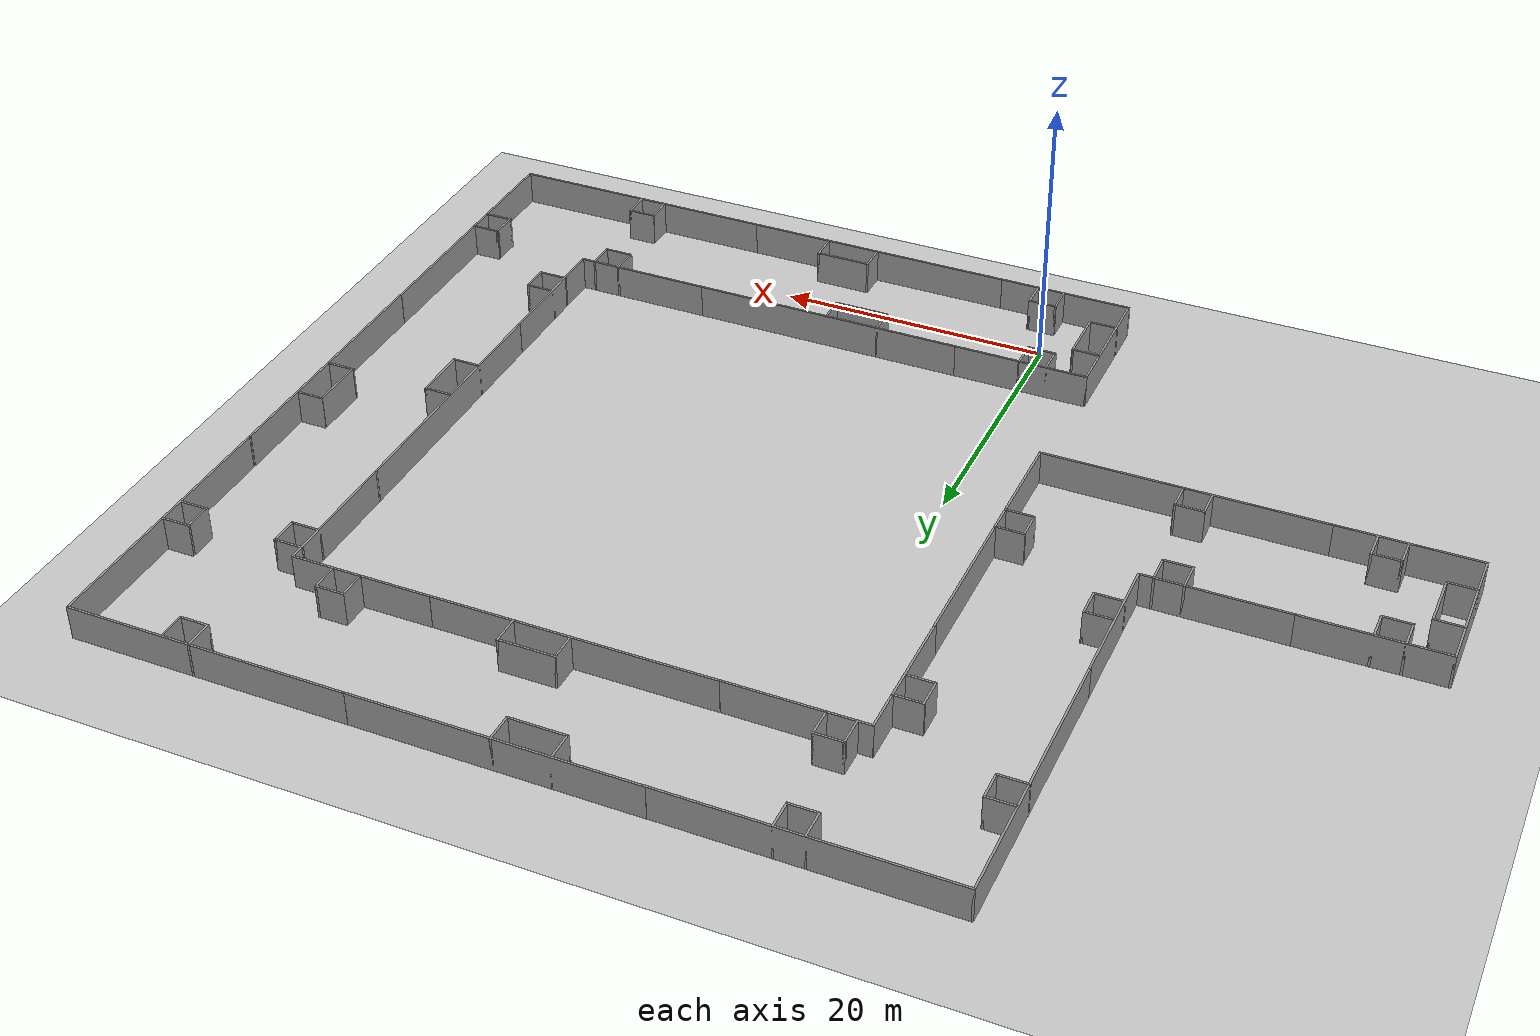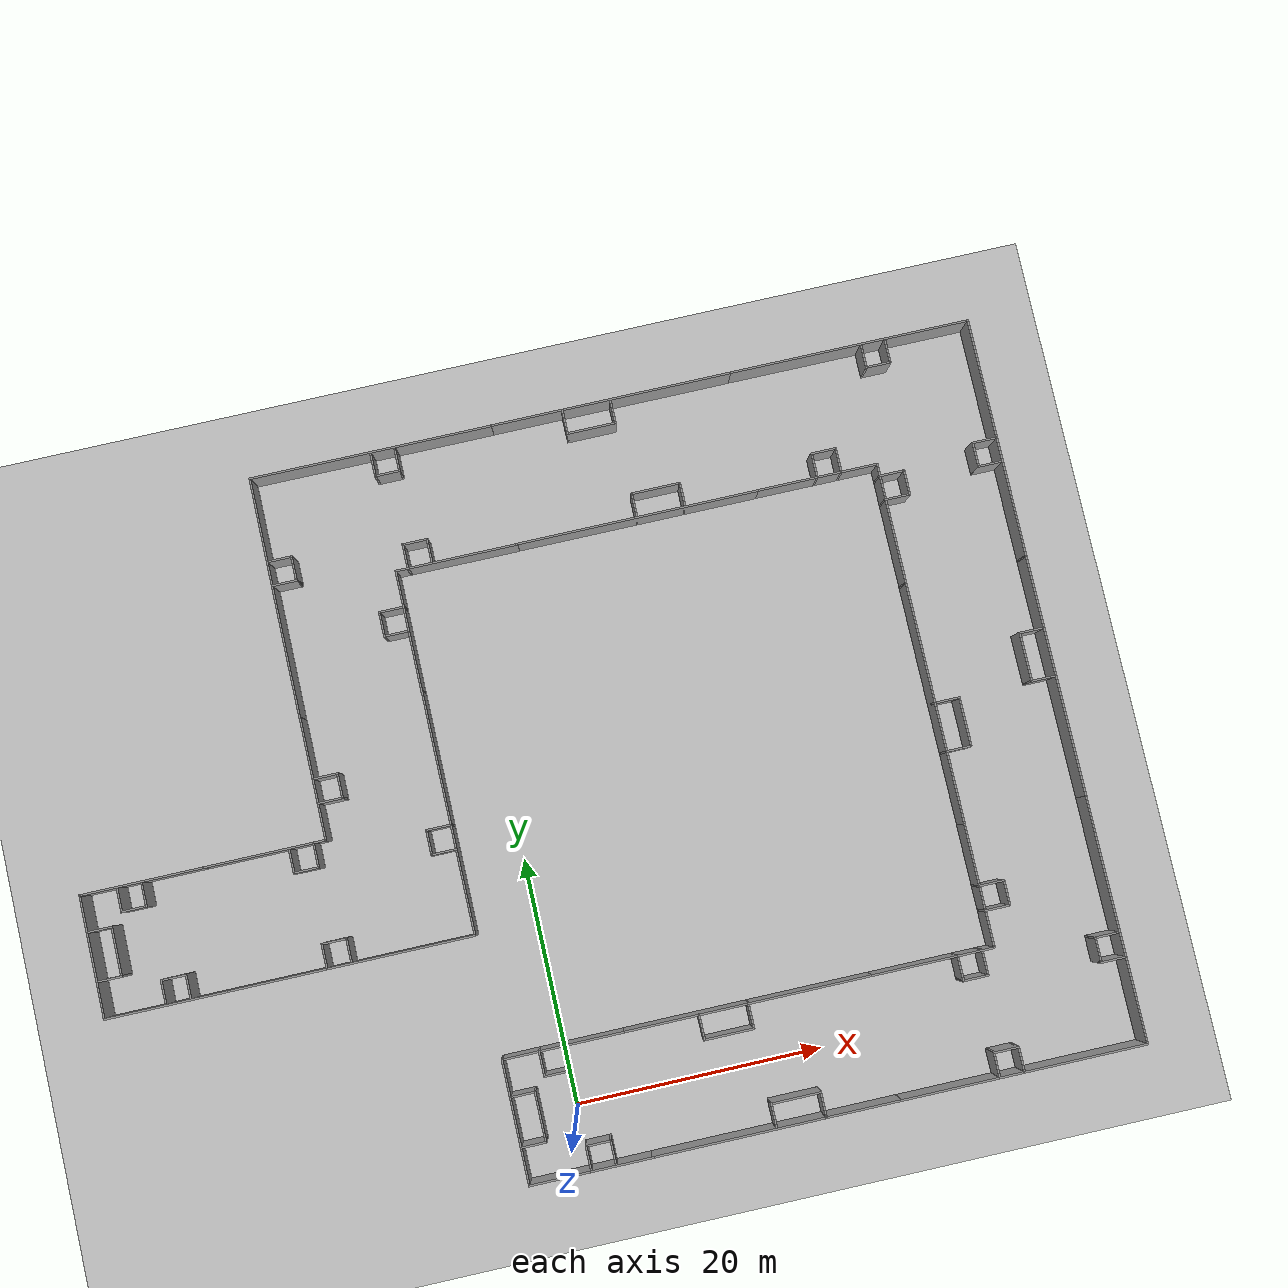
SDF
<sdf version="1.6">
 <world name="default">
  <light name="sun" type="directional">
   <pose>0 0 10 0 -0 0</pose>
   <diffuse>0.8 0.8 0.8 1</diffuse>
   <specular>0.1 0.1 0.1 1</specular>
   <attenuation>
    <range>1000</range>
    <constant>0.9</constant>
    <linear>0.01</linear>
    <quadratic>0.001</quadratic>
   </attenuation>
   <direction>-0.5 0.5 -1</direction>
  </light>
  <model name="ground_plane">
   <static>1</static>
   <link name="link">
    <collision name="collision">
     <geometry><plane><normal>0 0 1</normal><size>100 100</size></plane></geometry>
     <surface><friction><ode><mu>100</mu><mu2>50</mu2></ode></friction></surface>
    </collision>
    <visual name="visual">
     <cast_shadows>0</cast_shadows>
     <geometry><plane><normal>0 0 1</normal><size>100 100</size></plane></geometry>
     <material>
      <script><uri>file://media/materials/scripts/gazebo.material</uri><name>Gazebo/Grey</name></script>
     </material>
    </visual>
   </link>
  </model>
  <gravity>0 0 -9.8</gravity>
  <magnetic_field>6e-06 2.3e-05 -4.2e-05</magnetic_field>
  <atmosphere type="adiabatic"/>
  <physics name="default_physics" default="0" type="ode">
   <max_step_size>0.001</max_step_size>
   <real_time_factor>1</real_time_factor>
   <real_time_update_rate>1000</real_time_update_rate>
  </physics>
  <scene><ambient>0.4 0.4 0.4 1</ambient><background>0.7 0.7 0.7 1</background><shadows>1</shadows></scene>
  <spherical_coordinates>
   <surface_model>EARTH_WGS84</surface_model>
   <latitude_deg>0</latitude_deg>
   <longitude_deg>0</longitude_deg>
   <elevation>0</elevation>
   <heading_deg>0</heading_deg>
  </spherical_coordinates>
  <model name="part_u_1">
   <link name="Wall_78">
    <collision name="Wall_78_Collision">
     <geometry><box><size>10.15 0.15 2.5</size></box></geometry>
     <pose>0 0 1.25 0 -0 0</pose>
    </collision>
    <visual name="Wall_78_Visual">
     <pose>0 0 1.25 0 -0 0</pose>
     <geometry><box><size>10.15 0.15 2.5</size></box></geometry>
     <material>
      <script><uri>file://media/materials/scripts/gazebo.material</uri><name>Gazebo/Grey</name></script>
      <ambient>1 1 1 1</ambient>
     </material>
    </visual>
    <pose>0 -5 0 0 -0 3.14159</pose>
   </link>
   <link name="Wall_79">
    <collision name="Wall_79_Collision">
     <geometry><box><size>10.15 0.15 2.5</size></box></geometry>
     <pose>0 0 1.25 0 -0 0</pose>
    </collision>
    <visual name="Wall_79_Visual">
     <pose>0 0 1.25 0 -0 0</pose>
     <geometry><box><size>10.15 0.15 2.5</size></box></geometry>
     <material>
      <script><uri>file://media/materials/scripts/gazebo.material</uri><name>Gazebo/Grey</name></script>
      <ambient>1 1 1 1</ambient>
     </material>
    </visual>
    <pose>-5 0 0 0 -0 1.5708</pose>
   </link>
   <link name="Wall_80">
    <collision name="Wall_80_Collision">
     <geometry><box><size>10.15 0.15 2.5</size></box></geometry>
     <pose>0 0 1.25 0 -0 0</pose>
    </collision>
    <visual name="Wall_80_Visual">
     <pose>0 0 1.25 0 -0 0</pose>
     <geometry><box><size>10.15 0.15 2.5</size></box></geometry>
     <material>
      <script><uri>file://media/materials/scripts/gazebo.material</uri><name>Gazebo/Grey</name></script>
      <ambient>1 1 1 1</ambient>
     </material>
    </visual>
    <pose>0 5 0 0 -0 0</pose>
   </link>
   <link name="Wall_82">
    <collision name="Wall_82_Collision">
     <geometry><box><size>2.15 0.15 2.5</size></box></geometry>
     <pose>0 0 1.25 0 -0 0</pose>
    </collision>
    <visual name="Wall_82_Visual">
     <pose>0 0 1.25 0 -0 0</pose>
     <geometry><box><size>2.15 0.15 2.5</size></box></geometry>
     <material>
      <script><uri>file://media/materials/scripts/gazebo.material</uri><name>Gazebo/Grey</name></script>
      <ambient>1 1 1 1</ambient>
     </material>
    </visual>
    <pose>-4 2 0 0 -0 0</pose>
   </link>
   <link name="Wall_83">
    <collision name="Wall_83_Collision">
     <geometry><box><size>4.15 0.15 2.5</size></box></geometry>
     <pose>0 0 1.25 0 -0 0</pose>
    </collision>
    <visual name="Wall_83_Visual">
     <pose>0 0 1.25 0 -0 0</pose>
     <geometry><box><size>4.15 0.15 2.5</size></box></geometry>
     <material>
      <script><uri>file://media/materials/scripts/gazebo.material</uri><name>Gazebo/Grey</name></script>
      <ambient>1 1 1 1</ambient>
     </material>
    </visual>
    <pose>-3 0 0 0 0 -1.5708</pose>
   </link>
   <link name="Wall_84">
    <collision name="Wall_84_Collision">
     <geometry><box><size>2.15 0.15 2.5</size></box></geometry>
     <pose>0 0 1.25 0 -0 0</pose>
    </collision>
    <visual name="Wall_84_Visual">
     <pose>0 0 1.25 0 -0 0</pose>
     <geometry><box><size>2.15 0.15 2.5</size></box></geometry>
     <material>
      <script><uri>file://media/materials/scripts/gazebo.material</uri><name>Gazebo/Grey</name></script>
      <ambient>1 1 1 1</ambient>
     </material>
    </visual>
    <pose>-4 -2 0 0 -0 3.14159</pose>
   </link>
   <link name="Wall_86">
    <collision name="Wall_86_Collision">
     <geometry><box><size>2.15 0.15 2.5</size></box></geometry>
     <pose>0 0 1.25 0 -0 0</pose>
    </collision>
    <visual name="Wall_86_Visual">
     <pose>0 0 1.25 0 -0 0</pose>
     <geometry><box><size>2.15 0.15 2.5</size></box></geometry>
     <material>
      <script><uri>file://media/materials/scripts/gazebo.material</uri><name>Gazebo/Grey</name></script>
      <ambient>1 1 1 1</ambient>
     </material>
    </visual>
    <pose>-2 4 0 0 0 -1.5708</pose>
   </link>
   <link name="Wall_87">
    <collision name="Wall_87_Collision">
     <geometry><box><size>2.15 0.15 2.5</size></box></geometry>
     <pose>0 0 1.25 0 -0 0</pose>
    </collision>
    <visual name="Wall_87_Visual">
     <pose>0 0 1.25 0 -0 0</pose>
     <geometry><box><size>2.15 0.15 2.5</size></box></geometry>
     <material>
      <script><uri>file://media/materials/scripts/gazebo.material</uri><name>Gazebo/Grey</name></script>
      <ambient>1 1 1 1</ambient>
     </material>
    </visual>
    <pose>-1 3 0 0 -0 0</pose>
   </link>
   <link name="Wall_88">
    <collision name="Wall_88_Collision">
     <geometry><box><size>2.15 0.15 2.5</size></box></geometry>
     <pose>0 0 1.25 0 -0 0</pose>
    </collision>
    <visual name="Wall_88_Visual">
     <pose>0 0 1.25 0 -0 0</pose>
     <geometry><box><size>2.15 0.15 2.5</size></box></geometry>
     <material>
      <script><uri>file://media/materials/scripts/gazebo.material</uri><name>Gazebo/Grey</name></script>
      <ambient>1 1 1 1</ambient>
     </material>
    </visual>
    <pose>0 4 0 0 -0 1.5708</pose>
   </link>
   <link name="Wall_90">
    <collision name="Wall_90_Collision">
     <geometry><box><size>2.15 0.15 2.5</size></box></geometry>
     <pose>0 0 1.25 0 -0 0</pose>
    </collision>
    <visual name="Wall_90_Visual">
     <pose>0 0 1.25 0 -0 0</pose>
     <geometry><box><size>2.15 0.15 2.5</size></box></geometry>
     <material>
      <script><uri>file://media/materials/scripts/gazebo.material</uri><name>Gazebo/Grey</name></script>
      <ambient>1 1 1 1</ambient>
     </material>
    </visual>
    <pose>0 -4 0 0 -0 1.5708</pose>
   </link>
   <link name="Wall_91">
    <collision name="Wall_91_Collision">
     <geometry><box><size>2.15 0.15 2.5</size></box></geometry>
     <pose>0 0 1.25 0 -0 0</pose>
    </collision>
    <visual name="Wall_91_Visual">
     <pose>0 0 1.25 0 -0 0</pose>
     <geometry><box><size>2.15 0.15 2.5</size></box></geometry>
     <material>
      <script><uri>file://media/materials/scripts/gazebo.material</uri><name>Gazebo/Grey</name></script>
      <ambient>1 1 1 1</ambient>
     </material>
    </visual>
    <pose>1 -3 0 0 -0 0</pose>
   </link>
   <link name="Wall_92">
    <collision name="Wall_92_Collision">
     <geometry><box><size>2.15 0.15 2.5</size></box></geometry>
     <pose>0 0 1.25 0 -0 0</pose>
    </collision>
    <visual name="Wall_92_Visual">
     <pose>0 0 1.25 0 -0 0</pose>
     <geometry><box><size>2.15 0.15 2.5</size></box></geometry>
     <material>
      <script><uri>file://media/materials/scripts/gazebo.material</uri><name>Gazebo/Grey</name></script>
      <ambient>1 1 1 1</ambient>
     </material>
    </visual>
    <pose>2 -4 0 0 0 -1.5708</pose>
   </link>
   <static>1</static>
  </model>
  <model name="part_line_0">
   <link name="Wall_15">
    <pose>0 -5 0 0 -0 0</pose>
    <visual name="Wall_15_Visual">
     <pose>0 0 1.25 0 -0 0</pose>
     <geometry><box><size>20.15 0.15 2.5</size></box></geometry>
     <material>
      <script><uri>file://media/materials/scripts/gazebo.material</uri><name>Gazebo/Grey</name></script>
      <ambient>1 1 1 1</ambient>
      <diffuse>0.7 0.7 0.7 1</diffuse>
      <specular>0.01 0.01 0.01 1</specular>
      <emissive>0 0 0 1</emissive>
     </material>
    </visual>
    <collision name="Wall_15_Collision">
     <pose>0 0 1.25 0 -0 0</pose>
     <geometry><box><size>20.15 0.15 2.5</size></box></geometry>
     <surface>
      <friction>
       <ode><mu>1</mu><mu2>1</mu2><fdir1>0 0 0</fdir1><slip1>0</slip1><slip2>0</slip2></ode>
       <torsional>
        <coefficient>1</coefficient>
        <patch_radius>0</patch_radius>
        <surface_radius>0</surface_radius>
        <use_patch_radius>1</use_patch_radius>
        <ode><slip>0</slip></ode>
       </torsional>
      </friction>
      <bounce><restitution_coefficient>0</restitution_coefficient><threshold>1e+06</threshold></bounce>
      <contact>
       <collide_without_contact>0</collide_without_contact>
       <collide_without_contact_bitmask>1</collide_without_contact_bitmask>
       <collide_bitmask>1</collide_bitmask>
       <ode>
        <soft_cfm>0</soft_cfm>
        <soft_erp>0.2</soft_erp>
        <kp>1e+13</kp>
        <kd>1</kd>
        <max_vel>0.01</max_vel>
        <min_depth>0</min_depth>
       </ode>
       <bullet>
        <split_impulse>1</split_impulse>
        <split_impulse_penetration_threshold>-0.01</split_impulse_penetration_threshold>
        <soft_cfm>0</soft_cfm>
        <soft_erp>0.2</soft_erp>
        <kp>1e+13</kp>
        <kd>1</kd>
       </bullet>
      </contact>
     </surface>
    </collision>
   </link>
   <link name="Wall_17">
    <pose>0 5 0 0 -0 0</pose>
    <visual name="Wall_17_Visual">
     <pose>0 0 1.25 0 -0 0</pose>
     <geometry><box><size>20.15 0.15 2.5</size></box></geometry>
     <material>
      <script><uri>file://media/materials/scripts/gazebo.material</uri><name>Gazebo/Grey</name></script>
      <ambient>1 1 1 1</ambient>
      <diffuse>0.7 0.7 0.7 1</diffuse>
      <specular>0.01 0.01 0.01 1</specular>
      <emissive>0 0 0 1</emissive>
     </material>
    </visual>
    <collision name="Wall_17_Collision">
     <pose>0 0 1.25 0 -0 0</pose>
     <geometry><box><size>20.15 0.15 2.5</size></box></geometry>
     <surface>
      <friction>
       <ode><mu>1</mu><mu2>1</mu2><fdir1>0 0 0</fdir1><slip1>0</slip1><slip2>0</slip2></ode>
       <torsional>
        <coefficient>1</coefficient>
        <patch_radius>0</patch_radius>
        <surface_radius>0</surface_radius>
        <use_patch_radius>1</use_patch_radius>
        <ode><slip>0</slip></ode>
       </torsional>
      </friction>
      <bounce><restitution_coefficient>0</restitution_coefficient><threshold>1e+06</threshold></bounce>
      <contact>
       <collide_without_contact>0</collide_without_contact>
       <collide_without_contact_bitmask>1</collide_without_contact_bitmask>
       <collide_bitmask>1</collide_bitmask>
       <ode>
        <soft_cfm>0</soft_cfm>
        <soft_erp>0.2</soft_erp>
        <kp>1e+13</kp>
        <kd>1</kd>
        <max_vel>0.01</max_vel>
        <min_depth>0</min_depth>
       </ode>
       <bullet>
        <split_impulse>1</split_impulse>
        <split_impulse_penetration_threshold>-0.01</split_impulse_penetration_threshold>
        <soft_cfm>0</soft_cfm>
        <soft_erp>0.2</soft_erp>
        <kp>1e+13</kp>
        <kd>1</kd>
       </bullet>
      </contact>
     </surface>
    </collision>
   </link>
   <link name="Wall_19">
    <pose>-4 4 0 0 0 -1.5708</pose>
    <visual name="Wall_19_Visual">
     <pose>0 0 1.25 0 -0 0</pose>
     <geometry><box><size>2.15 0.15 2.5</size></box></geometry>
     <material>
      <script><uri>file://media/materials/scripts/gazebo.material</uri><name>Gazebo/Grey</name></script>
      <ambient>1 1 1 1</ambient>
      <diffuse>0.7 0.7 0.7 1</diffuse>
      <specular>0.01 0.01 0.01 1</specular>
      <emissive>0 0 0 1</emissive>
     </material>
    </visual>
    <collision name="Wall_19_Collision">
     <pose>0 0 1.25 0 -0 0</pose>
     <geometry><box><size>2.15 0.15 2.5</size></box></geometry>
     <surface>
      <friction>
       <ode><mu>1</mu><mu2>1</mu2><fdir1>0 0 0</fdir1><slip1>0</slip1><slip2>0</slip2></ode>
       <torsional>
        <coefficient>1</coefficient>
        <patch_radius>0</patch_radius>
        <surface_radius>0</surface_radius>
        <use_patch_radius>1</use_patch_radius>
        <ode><slip>0</slip></ode>
       </torsional>
      </friction>
      <bounce><restitution_coefficient>0</restitution_coefficient><threshold>1e+06</threshold></bounce>
      <contact>
       <collide_without_contact>0</collide_without_contact>
       <collide_without_contact_bitmask>1</collide_without_contact_bitmask>
       <collide_bitmask>1</collide_bitmask>
       <ode>
        <soft_cfm>0</soft_cfm>
        <soft_erp>0.2</soft_erp>
        <kp>1e+13</kp>
        <kd>1</kd>
        <max_vel>0.01</max_vel>
        <min_depth>0</min_depth>
       </ode>
       <bullet>
        <split_impulse>1</split_impulse>
        <split_impulse_penetration_threshold>-0.01</split_impulse_penetration_threshold>
        <soft_cfm>0</soft_cfm>
        <soft_erp>0.2</soft_erp>
        <kp>1e+13</kp>
        <kd>1</kd>
       </bullet>
      </contact>
     </surface>
    </collision>
   </link>
   <link name="Wall_20">
    <pose>-2 3 0 0 -0 0</pose>
    <visual name="Wall_20_Visual">
     <pose>0 0 1.25 0 -0 0</pose>
     <geometry><box><size>4.15 0.15 2.5</size></box></geometry>
     <material>
      <script><uri>file://media/materials/scripts/gazebo.material</uri><name>Gazebo/Grey</name></script>
      <ambient>1 1 1 1</ambient>
      <diffuse>0.7 0.7 0.7 1</diffuse>
      <specular>0.01 0.01 0.01 1</specular>
      <emissive>0 0 0 1</emissive>
     </material>
    </visual>
    <collision name="Wall_20_Collision">
     <pose>0 0 1.25 0 -0 0</pose>
     <geometry><box><size>4.15 0.15 2.5</size></box></geometry>
     <surface>
      <friction>
       <ode><mu>1</mu><mu2>1</mu2><fdir1>0 0 0</fdir1><slip1>0</slip1><slip2>0</slip2></ode>
       <torsional>
        <coefficient>1</coefficient>
        <patch_radius>0</patch_radius>
        <surface_radius>0</surface_radius>
        <use_patch_radius>1</use_patch_radius>
        <ode><slip>0</slip></ode>
       </torsional>
      </friction>
      <bounce><restitution_coefficient>0</restitution_coefficient><threshold>1e+06</threshold></bounce>
      <contact>
       <collide_without_contact>0</collide_without_contact>
       <collide_without_contact_bitmask>1</collide_without_contact_bitmask>
       <collide_bitmask>1</collide_bitmask>
       <ode>
        <soft_cfm>0</soft_cfm>
        <soft_erp>0.2</soft_erp>
        <kp>1e+13</kp>
        <kd>1</kd>
        <max_vel>0.01</max_vel>
        <min_depth>0</min_depth>
       </ode>
       <bullet>
        <split_impulse>1</split_impulse>
        <split_impulse_penetration_threshold>-0.01</split_impulse_penetration_threshold>
        <soft_cfm>0</soft_cfm>
        <soft_erp>0.2</soft_erp>
        <kp>1e+13</kp>
        <kd>1</kd>
       </bullet>
      </contact>
     </surface>
    </collision>
   </link>
   <link name="Wall_21">
    <pose>0 4 0 0 -0 1.5708</pose>
    <visual name="Wall_21_Visual">
     <pose>0 0 1.25 0 -0 0</pose>
     <geometry><box><size>2.15 0.15 2.5</size></box></geometry>
     <material>
      <script><uri>file://media/materials/scripts/gazebo.material</uri><name>Gazebo/Grey</name></script>
      <ambient>1 1 1 1</ambient>
      <diffuse>0.7 0.7 0.7 1</diffuse>
      <specular>0.01 0.01 0.01 1</specular>
      <emissive>0 0 0 1</emissive>
     </material>
    </visual>
    <collision name="Wall_21_Collision">
     <pose>0 0 1.25 0 -0 0</pose>
     <geometry><box><size>2.15 0.15 2.5</size></box></geometry>
     <surface>
      <friction>
       <ode><mu>1</mu><mu2>1</mu2><fdir1>0 0 0</fdir1><slip1>0</slip1><slip2>0</slip2></ode>
       <torsional>
        <coefficient>1</coefficient>
        <patch_radius>0</patch_radius>
        <surface_radius>0</surface_radius>
        <use_patch_radius>1</use_patch_radius>
        <ode><slip>0</slip></ode>
       </torsional>
      </friction>
      <bounce><restitution_coefficient>0</restitution_coefficient><threshold>1e+06</threshold></bounce>
      <contact>
       <collide_without_contact>0</collide_without_contact>
       <collide_without_contact_bitmask>1</collide_without_contact_bitmask>
       <collide_bitmask>1</collide_bitmask>
       <ode>
        <soft_cfm>0</soft_cfm>
        <soft_erp>0.2</soft_erp>
        <kp>1e+13</kp>
        <kd>1</kd>
        <max_vel>0.01</max_vel>
        <min_depth>0</min_depth>
       </ode>
       <bullet>
        <split_impulse>1</split_impulse>
        <split_impulse_penetration_threshold>-0.01</split_impulse_penetration_threshold>
        <soft_cfm>0</soft_cfm>
        <soft_erp>0.2</soft_erp>
        <kp>1e+13</kp>
        <kd>1</kd>
       </bullet>
      </contact>
     </surface>
    </collision>
   </link>
   <link name="Wall_23">
    <pose>0 -4 0 0 -0 1.5708</pose>
    <visual name="Wall_23_Visual">
     <pose>0 0 1.25 0 -0 0</pose>
     <geometry><box><size>2.15 0.15 2.5</size></box></geometry>
     <material>
      <script><uri>file://media/materials/scripts/gazebo.material</uri><name>Gazebo/Grey</name></script>
      <ambient>1 1 1 1</ambient>
      <diffuse>0.7 0.7 0.7 1</diffuse>
      <specular>0.01 0.01 0.01 1</specular>
      <emissive>0 0 0 1</emissive>
     </material>
    </visual>
    <collision name="Wall_23_Collision">
     <pose>0 0 1.25 0 -0 0</pose>
     <geometry><box><size>2.15 0.15 2.5</size></box></geometry>
     <surface>
      <friction>
       <ode><mu>1</mu><mu2>1</mu2><fdir1>0 0 0</fdir1><slip1>0</slip1><slip2>0</slip2></ode>
       <torsional>
        <coefficient>1</coefficient>
        <patch_radius>0</patch_radius>
        <surface_radius>0</surface_radius>
        <use_patch_radius>1</use_patch_radius>
        <ode><slip>0</slip></ode>
       </torsional>
      </friction>
      <bounce><restitution_coefficient>0</restitution_coefficient><threshold>1e+06</threshold></bounce>
      <contact>
       <collide_without_contact>0</collide_without_contact>
       <collide_without_contact_bitmask>1</collide_without_contact_bitmask>
       <collide_bitmask>1</collide_bitmask>
       <ode>
        <soft_cfm>0</soft_cfm>
        <soft_erp>0.2</soft_erp>
        <kp>1e+13</kp>
        <kd>1</kd>
        <max_vel>0.01</max_vel>
        <min_depth>0</min_depth>
       </ode>
       <bullet>
        <split_impulse>1</split_impulse>
        <split_impulse_penetration_threshold>-0.01</split_impulse_penetration_threshold>
        <soft_cfm>0</soft_cfm>
        <soft_erp>0.2</soft_erp>
        <kp>1e+13</kp>
        <kd>1</kd>
       </bullet>
      </contact>
     </surface>
    </collision>
   </link>
   <link name="Wall_24">
    <pose>2 -3 0 0 -0 0</pose>
    <visual name="Wall_24_Visual">
     <pose>0 0 1.25 0 -0 0</pose>
     <geometry><box><size>4.15 0.15 2.5</size></box></geometry>
     <material>
      <script><uri>file://media/materials/scripts/gazebo.material</uri><name>Gazebo/Grey</name></script>
      <ambient>1 1 1 1</ambient>
      <diffuse>0.7 0.7 0.7 1</diffuse>
      <specular>0.01 0.01 0.01 1</specular>
      <emissive>0 0 0 1</emissive>
     </material>
    </visual>
    <collision name="Wall_24_Collision">
     <pose>0 0 1.25 0 -0 0</pose>
     <geometry><box><size>4.15 0.15 2.5</size></box></geometry>
     <surface>
      <friction>
       <ode><mu>1</mu><mu2>1</mu2><fdir1>0 0 0</fdir1><slip1>0</slip1><slip2>0</slip2></ode>
       <torsional>
        <coefficient>1</coefficient>
        <patch_radius>0</patch_radius>
        <surface_radius>0</surface_radius>
        <use_patch_radius>1</use_patch_radius>
        <ode><slip>0</slip></ode>
       </torsional>
      </friction>
      <bounce><restitution_coefficient>0</restitution_coefficient><threshold>1e+06</threshold></bounce>
      <contact>
       <collide_without_contact>0</collide_without_contact>
       <collide_without_contact_bitmask>1</collide_without_contact_bitmask>
       <collide_bitmask>1</collide_bitmask>
       <ode>
        <soft_cfm>0</soft_cfm>
        <soft_erp>0.2</soft_erp>
        <kp>1e+13</kp>
        <kd>1</kd>
        <max_vel>0.01</max_vel>
        <min_depth>0</min_depth>
       </ode>
       <bullet>
        <split_impulse>1</split_impulse>
        <split_impulse_penetration_threshold>-0.01</split_impulse_penetration_threshold>
        <soft_cfm>0</soft_cfm>
        <soft_erp>0.2</soft_erp>
        <kp>1e+13</kp>
        <kd>1</kd>
       </bullet>
      </contact>
     </surface>
    </collision>
   </link>
   <link name="Wall_25">
    <pose>4 -4 0 0 0 -1.5708</pose>
    <visual name="Wall_25_Visual">
     <pose>0 0 1.25 0 -0 0</pose>
     <geometry><box><size>2.15 0.15 2.5</size></box></geometry>
     <material>
      <script><uri>file://media/materials/scripts/gazebo.material</uri><name>Gazebo/Grey</name></script>
      <ambient>1 1 1 1</ambient>
      <diffuse>0.7 0.7 0.7 1</diffuse>
      <specular>0.01 0.01 0.01 1</specular>
      <emissive>0 0 0 1</emissive>
     </material>
    </visual>
    <collision name="Wall_25_Collision">
     <pose>0 0 1.25 0 -0 0</pose>
     <geometry><box><size>2.15 0.15 2.5</size></box></geometry>
     <surface>
      <friction>
       <ode><mu>1</mu><mu2>1</mu2><fdir1>0 0 0</fdir1><slip1>0</slip1><slip2>0</slip2></ode>
       <torsional>
        <coefficient>1</coefficient>
        <patch_radius>0</patch_radius>
        <surface_radius>0</surface_radius>
        <use_patch_radius>1</use_patch_radius>
        <ode><slip>0</slip></ode>
       </torsional>
      </friction>
      <bounce><restitution_coefficient>0</restitution_coefficient><threshold>1e+06</threshold></bounce>
      <contact>
       <collide_without_contact>0</collide_without_contact>
       <collide_without_contact_bitmask>1</collide_without_contact_bitmask>
       <collide_bitmask>1</collide_bitmask>
       <ode>
        <soft_cfm>0</soft_cfm>
        <soft_erp>0.2</soft_erp>
        <kp>1e+13</kp>
        <kd>1</kd>
        <max_vel>0.01</max_vel>
        <min_depth>0</min_depth>
       </ode>
       <bullet>
        <split_impulse>1</split_impulse>
        <split_impulse_penetration_threshold>-0.01</split_impulse_penetration_threshold>
        <soft_cfm>0</soft_cfm>
        <soft_erp>0.2</soft_erp>
        <kp>1e+13</kp>
        <kd>1</kd>
       </bullet>
      </contact>
     </surface>
    </collision>
   </link>
   <static>1</static>
   <pose>14.9484 0.00516 0 0 -0 0</pose>
  </model>
  <model name="part_l_1">
   <link name="Wall_27">
    <pose>-0.000179 -10 0 0 -0 0</pose>
    <visual name="Wall_27_Visual">
     <pose>0 0 1.25 0 -0 0</pose>
     <geometry><box><size>20.15 0.15 2.5</size></box></geometry>
     <material>
      <script><uri>file://media/materials/scripts/gazebo.material</uri><name>Gazebo/Grey</name></script>
      <ambient>1 1 1 1</ambient>
      <diffuse>0.7 0.7 0.7 1</diffuse>
      <specular>0.01 0.01 0.01 1</specular>
      <emissive>0 0 0 1</emissive>
     </material>
    </visual>
    <collision name="Wall_27_Collision">
     <pose>0 0 1.25 0 -0 0</pose>
     <geometry><box><size>20.15 0.15 2.5</size></box></geometry>
     <surface>
      <friction>
       <ode><mu>1</mu><mu2>1</mu2><fdir1>0 0 0</fdir1><slip1>0</slip1><slip2>0</slip2></ode>
       <torsional>
        <coefficient>1</coefficient>
        <patch_radius>0</patch_radius>
        <surface_radius>0</surface_radius>
        <use_patch_radius>1</use_patch_radius>
        <ode><slip>0</slip></ode>
       </torsional>
      </friction>
      <bounce><restitution_coefficient>0</restitution_coefficient><threshold>1e+06</threshold></bounce>
      <contact>
       <collide_without_contact>0</collide_without_contact>
       <collide_without_contact_bitmask>1</collide_without_contact_bitmask>
       <collide_bitmask>1</collide_bitmask>
       <ode>
        <soft_cfm>0</soft_cfm>
        <soft_erp>0.2</soft_erp>
        <kp>1e+13</kp>
        <kd>1</kd>
        <max_vel>0.01</max_vel>
        <min_depth>0</min_depth>
       </ode>
       <bullet>
        <split_impulse>1</split_impulse>
        <split_impulse_penetration_threshold>-0.01</split_impulse_penetration_threshold>
        <soft_cfm>0</soft_cfm>
        <soft_erp>0.2</soft_erp>
        <kp>1e+13</kp>
        <kd>1</kd>
       </bullet>
      </contact>
     </surface>
    </collision>
   </link>
   <link name="Wall_28">
    <pose>9.99982 0 0 0 -0 1.5708</pose>
    <visual name="Wall_28_Visual">
     <pose>0 0 1.25 0 -0 0</pose>
     <geometry><box><size>20.15 0.15 2.5</size></box></geometry>
     <material>
      <script><uri>file://media/materials/scripts/gazebo.material</uri><name>Gazebo/Grey</name></script>
      <ambient>1 1 1 1</ambient>
      <diffuse>0.7 0.7 0.7 1</diffuse>
      <specular>0.01 0.01 0.01 1</specular>
      <emissive>0 0 0 1</emissive>
     </material>
    </visual>
    <collision name="Wall_28_Collision">
     <pose>0 0 1.25 0 -0 0</pose>
     <geometry><box><size>20.15 0.15 2.5</size></box></geometry>
     <surface>
      <friction>
       <ode><mu>1</mu><mu2>1</mu2><fdir1>0 0 0</fdir1><slip1>0</slip1><slip2>0</slip2></ode>
       <torsional>
        <coefficient>1</coefficient>
        <patch_radius>0</patch_radius>
        <surface_radius>0</surface_radius>
        <use_patch_radius>1</use_patch_radius>
        <ode><slip>0</slip></ode>
       </torsional>
      </friction>
      <bounce><restitution_coefficient>0</restitution_coefficient><threshold>1e+06</threshold></bounce>
      <contact>
       <collide_without_contact>0</collide_without_contact>
       <collide_without_contact_bitmask>1</collide_without_contact_bitmask>
       <collide_bitmask>1</collide_bitmask>
       <ode>
        <soft_cfm>0</soft_cfm>
        <soft_erp>0.2</soft_erp>
        <kp>1e+13</kp>
        <kd>1</kd>
        <max_vel>0.01</max_vel>
        <min_depth>0</min_depth>
       </ode>
       <bullet>
        <split_impulse>1</split_impulse>
        <split_impulse_penetration_threshold>-0.01</split_impulse_penetration_threshold>
        <soft_cfm>0</soft_cfm>
        <soft_erp>0.2</soft_erp>
        <kp>1e+13</kp>
        <kd>1</kd>
       </bullet>
      </contact>
     </surface>
    </collision>
   </link>
   <link name="Wall_30">
    <pose>-5.00018 0 0 0 -0 0</pose>
    <visual name="Wall_30_Visual">
     <pose>0 0 1.25 0 -0 0</pose>
     <geometry><box><size>10.15 0.15 2.5</size></box></geometry>
     <material>
      <script><uri>file://media/materials/scripts/gazebo.material</uri><name>Gazebo/Grey</name></script>
      <ambient>1 1 1 1</ambient>
      <diffuse>0.7 0.7 0.7 1</diffuse>
      <specular>0.01 0.01 0.01 1</specular>
      <emissive>0 0 0 1</emissive>
     </material>
    </visual>
    <collision name="Wall_30_Collision">
     <pose>0 0 1.25 0 -0 0</pose>
     <geometry><box><size>10.15 0.15 2.5</size></box></geometry>
     <surface>
      <friction>
       <ode><mu>1</mu><mu2>1</mu2><fdir1>0 0 0</fdir1><slip1>0</slip1><slip2>0</slip2></ode>
       <torsional>
        <coefficient>1</coefficient>
        <patch_radius>0</patch_radius>
        <surface_radius>0</surface_radius>
        <use_patch_radius>1</use_patch_radius>
        <ode><slip>0</slip></ode>
       </torsional>
      </friction>
      <bounce><restitution_coefficient>0</restitution_coefficient><threshold>1e+06</threshold></bounce>
      <contact>
       <collide_without_contact>0</collide_without_contact>
       <collide_without_contact_bitmask>1</collide_without_contact_bitmask>
       <collide_bitmask>1</collide_bitmask>
       <ode>
        <soft_cfm>0</soft_cfm>
        <soft_erp>0.2</soft_erp>
        <kp>1e+13</kp>
        <kd>1</kd>
        <max_vel>0.01</max_vel>
        <min_depth>0</min_depth>
       </ode>
       <bullet>
        <split_impulse>1</split_impulse>
        <split_impulse_penetration_threshold>-0.01</split_impulse_penetration_threshold>
        <soft_cfm>0</soft_cfm>
        <soft_erp>0.2</soft_erp>
        <kp>1e+13</kp>
        <kd>1</kd>
       </bullet>
      </contact>
     </surface>
    </collision>
   </link>
   <link name="Wall_31">
    <pose>-0.000179 5 0 0 -0 1.5708</pose>
    <visual name="Wall_31_Visual">
     <pose>0 0 1.25 0 -0 0</pose>
     <geometry><box><size>10.15 0.15 2.5</size></box></geometry>
     <material>
      <script><uri>file://media/materials/scripts/gazebo.material</uri><name>Gazebo/Grey</name></script>
      <ambient>1 1 1 1</ambient>
      <diffuse>0.7 0.7 0.7 1</diffuse>
      <specular>0.01 0.01 0.01 1</specular>
      <emissive>0 0 0 1</emissive>
     </material>
    </visual>
    <collision name="Wall_31_Collision">
     <pose>0 0 1.25 0 -0 0</pose>
     <geometry><box><size>10.15 0.15 2.5</size></box></geometry>
     <surface>
      <friction>
       <ode><mu>1</mu><mu2>1</mu2><fdir1>0 0 0</fdir1><slip1>0</slip1><slip2>0</slip2></ode>
       <torsional>
        <coefficient>1</coefficient>
        <patch_radius>0</patch_radius>
        <surface_radius>0</surface_radius>
        <use_patch_radius>1</use_patch_radius>
        <ode><slip>0</slip></ode>
       </torsional>
      </friction>
      <bounce><restitution_coefficient>0</restitution_coefficient><threshold>1e+06</threshold></bounce>
      <contact>
       <collide_without_contact>0</collide_without_contact>
       <collide_without_contact_bitmask>1</collide_without_contact_bitmask>
       <collide_bitmask>1</collide_bitmask>
       <ode>
        <soft_cfm>0</soft_cfm>
        <soft_erp>0.2</soft_erp>
        <kp>1e+13</kp>
        <kd>1</kd>
        <max_vel>0.01</max_vel>
        <min_depth>0</min_depth>
       </ode>
       <bullet>
        <split_impulse>1</split_impulse>
        <split_impulse_penetration_threshold>-0.01</split_impulse_penetration_threshold>
        <soft_cfm>0</soft_cfm>
        <soft_erp>0.2</soft_erp>
        <kp>1e+13</kp>
        <kd>1</kd>
       </bullet>
      </contact>
     </surface>
    </collision>
   </link>
   <link name="Wall_33">
    <pose>-2.00018 -9 0 0 -0 1.5708</pose>
    <visual name="Wall_33_Visual">
     <pose>0 0 1.25 0 -0 0</pose>
     <geometry><box><size>2.15 0.15 2.5</size></box></geometry>
     <material>
      <script><uri>file://media/materials/scripts/gazebo.material</uri><name>Gazebo/Grey</name></script>
      <ambient>1 1 1 1</ambient>
      <diffuse>0.7 0.7 0.7 1</diffuse>
      <specular>0.01 0.01 0.01 1</specular>
      <emissive>0 0 0 1</emissive>
     </material>
    </visual>
    <collision name="Wall_33_Collision">
     <pose>0 0 1.25 0 -0 0</pose>
     <geometry><box><size>2.15 0.15 2.5</size></box></geometry>
     <surface>
      <friction>
       <ode><mu>1</mu><mu2>1</mu2><fdir1>0 0 0</fdir1><slip1>0</slip1><slip2>0</slip2></ode>
       <torsional>
        <coefficient>1</coefficient>
        <patch_radius>0</patch_radius>
        <surface_radius>0</surface_radius>
        <use_patch_radius>1</use_patch_radius>
        <ode><slip>0</slip></ode>
       </torsional>
      </friction>
      <bounce><restitution_coefficient>0</restitution_coefficient><threshold>1e+06</threshold></bounce>
      <contact>
       <collide_without_contact>0</collide_without_contact>
       <collide_without_contact_bitmask>1</collide_without_contact_bitmask>
       <collide_bitmask>1</collide_bitmask>
       <ode>
        <soft_cfm>0</soft_cfm>
        <soft_erp>0.2</soft_erp>
        <kp>1e+13</kp>
        <kd>1</kd>
        <max_vel>0.01</max_vel>
        <min_depth>0</min_depth>
       </ode>
       <bullet>
        <split_impulse>1</split_impulse>
        <split_impulse_penetration_threshold>-0.01</split_impulse_penetration_threshold>
        <soft_cfm>0</soft_cfm>
        <soft_erp>0.2</soft_erp>
        <kp>1e+13</kp>
        <kd>1</kd>
       </bullet>
      </contact>
     </surface>
    </collision>
   </link>
   <link name="Wall_34">
    <pose>-1.00018 -8 0 0 -0 0</pose>
    <visual name="Wall_34_Visual">
     <pose>0 0 1.25 0 -0 0</pose>
     <geometry><box><size>2.15 0.15 2.5</size></box></geometry>
     <material>
      <script><uri>file://media/materials/scripts/gazebo.material</uri><name>Gazebo/Grey</name></script>
      <ambient>1 1 1 1</ambient>
      <diffuse>0.7 0.7 0.7 1</diffuse>
      <specular>0.01 0.01 0.01 1</specular>
      <emissive>0 0 0 1</emissive>
     </material>
    </visual>
    <collision name="Wall_34_Collision">
     <pose>0 0 1.25 0 -0 0</pose>
     <geometry><box><size>2.15 0.15 2.5</size></box></geometry>
     <surface>
      <friction>
       <ode><mu>1</mu><mu2>1</mu2><fdir1>0 0 0</fdir1><slip1>0</slip1><slip2>0</slip2></ode>
       <torsional>
        <coefficient>1</coefficient>
        <patch_radius>0</patch_radius>
        <surface_radius>0</surface_radius>
        <use_patch_radius>1</use_patch_radius>
        <ode><slip>0</slip></ode>
       </torsional>
      </friction>
      <bounce><restitution_coefficient>0</restitution_coefficient><threshold>1e+06</threshold></bounce>
      <contact>
       <collide_without_contact>0</collide_without_contact>
       <collide_without_contact_bitmask>1</collide_without_contact_bitmask>
       <collide_bitmask>1</collide_bitmask>
       <ode>
        <soft_cfm>0</soft_cfm>
        <soft_erp>0.2</soft_erp>
        <kp>1e+13</kp>
        <kd>1</kd>
        <max_vel>0.01</max_vel>
        <min_depth>0</min_depth>
       </ode>
       <bullet>
        <split_impulse>1</split_impulse>
        <split_impulse_penetration_threshold>-0.01</split_impulse_penetration_threshold>
        <soft_cfm>0</soft_cfm>
        <soft_erp>0.2</soft_erp>
        <kp>1e+13</kp>
        <kd>1</kd>
       </bullet>
      </contact>
     </surface>
    </collision>
   </link>
   <link name="Wall_35">
    <pose>-0.000179 -9 0 0 0 -1.5708</pose>
    <visual name="Wall_35_Visual">
     <pose>0 0 1.25 0 -0 0</pose>
     <geometry><box><size>2.15 0.15 2.5</size></box></geometry>
     <material>
      <script><uri>file://media/materials/scripts/gazebo.material</uri><name>Gazebo/Grey</name></script>
      <ambient>1 1 1 1</ambient>
      <diffuse>0.7 0.7 0.7 1</diffuse>
      <specular>0.01 0.01 0.01 1</specular>
      <emissive>0 0 0 1</emissive>
     </material>
    </visual>
    <collision name="Wall_35_Collision">
     <pose>0 0 1.25 0 -0 0</pose>
     <geometry><box><size>2.15 0.15 2.5</size></box></geometry>
     <surface>
      <friction>
       <ode><mu>1</mu><mu2>1</mu2><fdir1>0 0 0</fdir1><slip1>0</slip1><slip2>0</slip2></ode>
       <torsional>
        <coefficient>1</coefficient>
        <patch_radius>0</patch_radius>
        <surface_radius>0</surface_radius>
        <use_patch_radius>1</use_patch_radius>
        <ode><slip>0</slip></ode>
       </torsional>
      </friction>
      <bounce><restitution_coefficient>0</restitution_coefficient><threshold>1e+06</threshold></bounce>
      <contact>
       <collide_without_contact>0</collide_without_contact>
       <collide_without_contact_bitmask>1</collide_without_contact_bitmask>
       <collide_bitmask>1</collide_bitmask>
       <ode>
        <soft_cfm>0</soft_cfm>
        <soft_erp>0.2</soft_erp>
        <kp>1e+13</kp>
        <kd>1</kd>
        <max_vel>0.01</max_vel>
        <min_depth>0</min_depth>
       </ode>
       <bullet>
        <split_impulse>1</split_impulse>
        <split_impulse_penetration_threshold>-0.01</split_impulse_penetration_threshold>
        <soft_cfm>0</soft_cfm>
        <soft_erp>0.2</soft_erp>
        <kp>1e+13</kp>
        <kd>1</kd>
       </bullet>
      </contact>
     </surface>
    </collision>
   </link>
   <link name="Wall_37">
    <pose>8.99982 -1 0 0 -0 3.14159</pose>
    <visual name="Wall_37_Visual">
     <pose>0 0 1.25 0 -0 0</pose>
     <geometry><box><size>2.15072 0.15 2.5</size></box></geometry>
     <material>
      <script><uri>file://media/materials/scripts/gazebo.material</uri><name>Gazebo/Grey</name></script>
      <ambient>1 1 1 1</ambient>
      <diffuse>0.7 0.7 0.7 1</diffuse>
      <specular>0.01 0.01 0.01 1</specular>
      <emissive>0 0 0 1</emissive>
     </material>
    </visual>
    <collision name="Wall_37_Collision">
     <pose>0 0 1.25 0 -0 0</pose>
     <geometry><box><size>2.15072 0.15 2.5</size></box></geometry>
     <surface>
      <friction>
       <ode><mu>1</mu><mu2>1</mu2><fdir1>0 0 0</fdir1><slip1>0</slip1><slip2>0</slip2></ode>
       <torsional>
        <coefficient>1</coefficient>
        <patch_radius>0</patch_radius>
        <surface_radius>0</surface_radius>
        <use_patch_radius>1</use_patch_radius>
        <ode><slip>0</slip></ode>
       </torsional>
      </friction>
      <bounce><restitution_coefficient>0</restitution_coefficient><threshold>1e+06</threshold></bounce>
      <contact>
       <collide_without_contact>0</collide_without_contact>
       <collide_without_contact_bitmask>1</collide_without_contact_bitmask>
       <collide_bitmask>1</collide_bitmask>
       <ode>
        <soft_cfm>0</soft_cfm>
        <soft_erp>0.2</soft_erp>
        <kp>1e+13</kp>
        <kd>1</kd>
        <max_vel>0.01</max_vel>
        <min_depth>0</min_depth>
       </ode>
       <bullet>
        <split_impulse>1</split_impulse>
        <split_impulse_penetration_threshold>-0.01</split_impulse_penetration_threshold>
        <soft_cfm>0</soft_cfm>
        <soft_erp>0.2</soft_erp>
        <kp>1e+13</kp>
        <kd>1</kd>
       </bullet>
      </contact>
     </surface>
    </collision>
   </link>
   <link name="Wall_38">
    <pose>7.99982 -2 0 0 0 -1.5708</pose>
    <visual name="Wall_38_Visual">
     <pose>0 0 1.25 0 -0 0</pose>
     <geometry><box><size>2.15 0.15 2.5</size></box></geometry>
     <material>
      <script><uri>file://media/materials/scripts/gazebo.material</uri><name>Gazebo/Grey</name></script>
      <ambient>1 1 1 1</ambient>
      <diffuse>0.7 0.7 0.7 1</diffuse>
      <specular>0.01 0.01 0.01 1</specular>
      <emissive>0 0 0 1</emissive>
     </material>
    </visual>
    <collision name="Wall_38_Collision">
     <pose>0 0 1.25 0 -0 0</pose>
     <geometry><box><size>2.15 0.15 2.5</size></box></geometry>
     <surface>
      <friction>
       <ode><mu>1</mu><mu2>1</mu2><fdir1>0 0 0</fdir1><slip1>0</slip1><slip2>0</slip2></ode>
       <torsional>
        <coefficient>1</coefficient>
        <patch_radius>0</patch_radius>
        <surface_radius>0</surface_radius>
        <use_patch_radius>1</use_patch_radius>
        <ode><slip>0</slip></ode>
       </torsional>
      </friction>
      <bounce><restitution_coefficient>0</restitution_coefficient><threshold>1e+06</threshold></bounce>
      <contact>
       <collide_without_contact>0</collide_without_contact>
       <collide_without_contact_bitmask>1</collide_without_contact_bitmask>
       <collide_bitmask>1</collide_bitmask>
       <ode>
        <soft_cfm>0</soft_cfm>
        <soft_erp>0.2</soft_erp>
        <kp>1e+13</kp>
        <kd>1</kd>
        <max_vel>0.01</max_vel>
        <min_depth>0</min_depth>
       </ode>
       <bullet>
        <split_impulse>1</split_impulse>
        <split_impulse_penetration_threshold>-0.01</split_impulse_penetration_threshold>
        <soft_cfm>0</soft_cfm>
        <soft_erp>0.2</soft_erp>
        <kp>1e+13</kp>
        <kd>1</kd>
       </bullet>
      </contact>
     </surface>
    </collision>
   </link>
   <link name="Wall_39">
    <pose>8.99982 -3 0 0 -0 0</pose>
    <visual name="Wall_39_Visual">
     <pose>0 0 1.25 0 -0 0</pose>
     <geometry><box><size>2.15 0.15 2.5</size></box></geometry>
     <material>
      <script><uri>file://media/materials/scripts/gazebo.material</uri><name>Gazebo/Grey</name></script>
      <ambient>1 1 1 1</ambient>
      <diffuse>0.7 0.7 0.7 1</diffuse>
      <specular>0.01 0.01 0.01 1</specular>
      <emissive>0 0 0 1</emissive>
     </material>
    </visual>
    <collision name="Wall_39_Collision">
     <pose>0 0 1.25 0 -0 0</pose>
     <geometry><box><size>2.15 0.15 2.5</size></box></geometry>
     <surface>
      <friction>
       <ode><mu>1</mu><mu2>1</mu2><fdir1>0 0 0</fdir1><slip1>0</slip1><slip2>0</slip2></ode>
       <torsional>
        <coefficient>1</coefficient>
        <patch_radius>0</patch_radius>
        <surface_radius>0</surface_radius>
        <use_patch_radius>1</use_patch_radius>
        <ode><slip>0</slip></ode>
       </torsional>
      </friction>
      <bounce><restitution_coefficient>0</restitution_coefficient><threshold>1e+06</threshold></bounce>
      <contact>
       <collide_without_contact>0</collide_without_contact>
       <collide_without_contact_bitmask>1</collide_without_contact_bitmask>
       <collide_bitmask>1</collide_bitmask>
       <ode>
        <soft_cfm>0</soft_cfm>
        <soft_erp>0.2</soft_erp>
        <kp>1e+13</kp>
        <kd>1</kd>
        <max_vel>0.01</max_vel>
        <min_depth>0</min_depth>
       </ode>
       <bullet>
        <split_impulse>1</split_impulse>
        <split_impulse_penetration_threshold>-0.01</split_impulse_penetration_threshold>
        <soft_cfm>0</soft_cfm>
        <soft_erp>0.2</soft_erp>
        <kp>1e+13</kp>
        <kd>1</kd>
       </bullet>
      </contact>
     </surface>
    </collision>
   </link>
   <link name="Wall_41">
    <pose>0.999821 5 0 0 -0 0</pose>
    <visual name="Wall_41_Visual">
     <pose>0 0 1.25 0 -0 0</pose>
     <geometry><box><size>2.15 0.15 2.5</size></box></geometry>
     <material>
      <script><uri>file://media/materials/scripts/gazebo.material</uri><name>Gazebo/Grey</name></script>
      <ambient>1 1 1 1</ambient>
      <diffuse>0.7 0.7 0.7 1</diffuse>
      <specular>0.01 0.01 0.01 1</specular>
      <emissive>0 0 0 1</emissive>
     </material>
    </visual>
    <collision name="Wall_41_Collision">
     <pose>0 0 1.25 0 -0 0</pose>
     <geometry><box><size>2.15 0.15 2.5</size></box></geometry>
     <surface>
      <friction>
       <ode><mu>1</mu><mu2>1</mu2><fdir1>0 0 0</fdir1><slip1>0</slip1><slip2>0</slip2></ode>
       <torsional>
        <coefficient>1</coefficient>
        <patch_radius>0</patch_radius>
        <surface_radius>0</surface_radius>
        <use_patch_radius>1</use_patch_radius>
        <ode><slip>0</slip></ode>
       </torsional>
      </friction>
      <bounce><restitution_coefficient>0</restitution_coefficient><threshold>1e+06</threshold></bounce>
      <contact>
       <collide_without_contact>0</collide_without_contact>
       <collide_without_contact_bitmask>1</collide_without_contact_bitmask>
       <collide_bitmask>1</collide_bitmask>
       <ode>
        <soft_cfm>0</soft_cfm>
        <soft_erp>0.2</soft_erp>
        <kp>1e+13</kp>
        <kd>1</kd>
        <max_vel>0.01</max_vel>
        <min_depth>0</min_depth>
       </ode>
       <bullet>
        <split_impulse>1</split_impulse>
        <split_impulse_penetration_threshold>-0.01</split_impulse_penetration_threshold>
        <soft_cfm>0</soft_cfm>
        <soft_erp>0.2</soft_erp>
        <kp>1e+13</kp>
        <kd>1</kd>
       </bullet>
      </contact>
     </surface>
    </collision>
   </link>
   <link name="Wall_42">
    <pose>1.99982 4 0 0 0 -1.5708</pose>
    <visual name="Wall_42_Visual">
     <pose>0 0 1.25 0 -0 0</pose>
     <geometry><box><size>2.15 0.15 2.5</size></box></geometry>
     <material>
      <script><uri>file://media/materials/scripts/gazebo.material</uri><name>Gazebo/Grey</name></script>
      <ambient>1 1 1 1</ambient>
      <diffuse>0.7 0.7 0.7 1</diffuse>
      <specular>0.01 0.01 0.01 1</specular>
      <emissive>0 0 0 1</emissive>
     </material>
    </visual>
    <collision name="Wall_42_Collision">
     <pose>0 0 1.25 0 -0 0</pose>
     <geometry><box><size>2.15 0.15 2.5</size></box></geometry>
     <surface>
      <friction>
       <ode><mu>1</mu><mu2>1</mu2><fdir1>0 0 0</fdir1><slip1>0</slip1><slip2>0</slip2></ode>
       <torsional>
        <coefficient>1</coefficient>
        <patch_radius>0</patch_radius>
        <surface_radius>0</surface_radius>
        <use_patch_radius>1</use_patch_radius>
        <ode><slip>0</slip></ode>
       </torsional>
      </friction>
      <bounce><restitution_coefficient>0</restitution_coefficient><threshold>1e+06</threshold></bounce>
      <contact>
       <collide_without_contact>0</collide_without_contact>
       <collide_without_contact_bitmask>1</collide_without_contact_bitmask>
       <collide_bitmask>1</collide_bitmask>
       <ode>
        <soft_cfm>0</soft_cfm>
        <soft_erp>0.2</soft_erp>
        <kp>1e+13</kp>
        <kd>1</kd>
        <max_vel>0.01</max_vel>
        <min_depth>0</min_depth>
       </ode>
       <bullet>
        <split_impulse>1</split_impulse>
        <split_impulse_penetration_threshold>-0.01</split_impulse_penetration_threshold>
        <soft_cfm>0</soft_cfm>
        <soft_erp>0.2</soft_erp>
        <kp>1e+13</kp>
        <kd>1</kd>
       </bullet>
      </contact>
     </surface>
    </collision>
   </link>
   <link name="Wall_43">
    <pose>0.999821 3 0 0 -0 3.14159</pose>
    <visual name="Wall_43_Visual">
     <pose>0 0 1.25 0 -0 0</pose>
     <geometry><box><size>2.15 0.15 2.5</size></box></geometry>
     <material>
      <script><uri>file://media/materials/scripts/gazebo.material</uri><name>Gazebo/Grey</name></script>
      <ambient>1 1 1 1</ambient>
      <diffuse>0.7 0.7 0.7 1</diffuse>
      <specular>0.01 0.01 0.01 1</specular>
      <emissive>0 0 0 1</emissive>
     </material>
    </visual>
    <collision name="Wall_43_Collision">
     <pose>0 0 1.25 0 -0 0</pose>
     <geometry><box><size>2.15 0.15 2.5</size></box></geometry>
     <surface>
      <friction>
       <ode><mu>1</mu><mu2>1</mu2><fdir1>0 0 0</fdir1><slip1>0</slip1><slip2>0</slip2></ode>
       <torsional>
        <coefficient>1</coefficient>
        <patch_radius>0</patch_radius>
        <surface_radius>0</surface_radius>
        <use_patch_radius>1</use_patch_radius>
        <ode><slip>0</slip></ode>
       </torsional>
      </friction>
      <bounce><restitution_coefficient>0</restitution_coefficient><threshold>1e+06</threshold></bounce>
      <contact>
       <collide_without_contact>0</collide_without_contact>
       <collide_without_contact_bitmask>1</collide_without_contact_bitmask>
       <collide_bitmask>1</collide_bitmask>
       <ode>
        <soft_cfm>0</soft_cfm>
        <soft_erp>0.2</soft_erp>
        <kp>1e+13</kp>
        <kd>1</kd>
        <max_vel>0.01</max_vel>
        <min_depth>0</min_depth>
       </ode>
       <bullet>
        <split_impulse>1</split_impulse>
        <split_impulse_penetration_threshold>-0.01</split_impulse_penetration_threshold>
        <soft_cfm>0</soft_cfm>
        <soft_erp>0.2</soft_erp>
        <kp>1e+13</kp>
        <kd>1</kd>
       </bullet>
      </contact>
     </surface>
    </collision>
   </link>
   <link name="Wall_45">
    <pose>-3.00018 -1 0 0 0 -1.5708</pose>
    <visual name="Wall_45_Visual">
     <pose>0 0 1.25 0 -0 0</pose>
     <geometry><box><size>2.15 0.15 2.5</size></box></geometry>
     <material>
      <script><uri>file://media/materials/scripts/gazebo.material</uri><name>Gazebo/Grey</name></script>
      <ambient>1 1 1 1</ambient>
      <diffuse>0.7 0.7 0.7 1</diffuse>
      <specular>0.01 0.01 0.01 1</specular>
      <emissive>0 0 0 1</emissive>
     </material>
    </visual>
    <collision name="Wall_45_Collision">
     <pose>0 0 1.25 0 -0 0</pose>
     <geometry><box><size>2.15 0.15 2.5</size></box></geometry>
     <surface>
      <friction>
       <ode><mu>1</mu><mu2>1</mu2><fdir1>0 0 0</fdir1><slip1>0</slip1><slip2>0</slip2></ode>
       <torsional>
        <coefficient>1</coefficient>
        <patch_radius>0</patch_radius>
        <surface_radius>0</surface_radius>
        <use_patch_radius>1</use_patch_radius>
        <ode><slip>0</slip></ode>
       </torsional>
      </friction>
      <bounce><restitution_coefficient>0</restitution_coefficient><threshold>1e+06</threshold></bounce>
      <contact>
       <collide_without_contact>0</collide_without_contact>
       <collide_without_contact_bitmask>1</collide_without_contact_bitmask>
       <collide_bitmask>1</collide_bitmask>
       <ode>
        <soft_cfm>0</soft_cfm>
        <soft_erp>0.2</soft_erp>
        <kp>1e+13</kp>
        <kd>1</kd>
        <max_vel>0.01</max_vel>
        <min_depth>0</min_depth>
       </ode>
       <bullet>
        <split_impulse>1</split_impulse>
        <split_impulse_penetration_threshold>-0.01</split_impulse_penetration_threshold>
        <soft_cfm>0</soft_cfm>
        <soft_erp>0.2</soft_erp>
        <kp>1e+13</kp>
        <kd>1</kd>
       </bullet>
      </contact>
     </surface>
    </collision>
   </link>
   <link name="Wall_46">
    <pose>-2.00018 -2 0 0 -0 0</pose>
    <visual name="Wall_46_Visual">
     <pose>0 0 1.25 0 -0 0</pose>
     <geometry><box><size>2.15 0.15 2.5</size></box></geometry>
     <material>
      <script><uri>file://media/materials/scripts/gazebo.material</uri><name>Gazebo/Grey</name></script>
      <ambient>1 1 1 1</ambient>
      <diffuse>0.7 0.7 0.7 1</diffuse>
      <specular>0.01 0.01 0.01 1</specular>
      <emissive>0 0 0 1</emissive>
     </material>
    </visual>
    <collision name="Wall_46_Collision">
     <pose>0 0 1.25 0 -0 0</pose>
     <geometry><box><size>2.15 0.15 2.5</size></box></geometry>
     <surface>
      <friction>
       <ode><mu>1</mu><mu2>1</mu2><fdir1>0 0 0</fdir1><slip1>0</slip1><slip2>0</slip2></ode>
       <torsional>
        <coefficient>1</coefficient>
        <patch_radius>0</patch_radius>
        <surface_radius>0</surface_radius>
        <use_patch_radius>1</use_patch_radius>
        <ode><slip>0</slip></ode>
       </torsional>
      </friction>
      <bounce><restitution_coefficient>0</restitution_coefficient><threshold>1e+06</threshold></bounce>
      <contact>
       <collide_without_contact>0</collide_without_contact>
       <collide_without_contact_bitmask>1</collide_without_contact_bitmask>
       <collide_bitmask>1</collide_bitmask>
       <ode>
        <soft_cfm>0</soft_cfm>
        <soft_erp>0.2</soft_erp>
        <kp>1e+13</kp>
        <kd>1</kd>
        <max_vel>0.01</max_vel>
        <min_depth>0</min_depth>
       </ode>
       <bullet>
        <split_impulse>1</split_impulse>
        <split_impulse_penetration_threshold>-0.01</split_impulse_penetration_threshold>
        <soft_cfm>0</soft_cfm>
        <soft_erp>0.2</soft_erp>
        <kp>1e+13</kp>
        <kd>1</kd>
       </bullet>
      </contact>
     </surface>
    </collision>
   </link>
   <link name="Wall_47">
    <pose>-1.00018 -0.999 0 0 -0 1.5708</pose>
    <visual name="Wall_47_Visual">
     <pose>0 0 1.25 0 -0 0</pose>
     <geometry><box><size>2.152 0.15 2.5</size></box></geometry>
     <material>
      <script><uri>file://media/materials/scripts/gazebo.material</uri><name>Gazebo/Grey</name></script>
      <ambient>1 1 1 1</ambient>
      <diffuse>0.7 0.7 0.7 1</diffuse>
      <specular>0.01 0.01 0.01 1</specular>
      <emissive>0 0 0 1</emissive>
     </material>
    </visual>
    <collision name="Wall_47_Collision">
     <pose>0 0 1.25 0 -0 0</pose>
     <geometry><box><size>2.152 0.15 2.5</size></box></geometry>
     <surface>
      <friction>
       <ode><mu>1</mu><mu2>1</mu2><fdir1>0 0 0</fdir1><slip1>0</slip1><slip2>0</slip2></ode>
       <torsional>
        <coefficient>1</coefficient>
        <patch_radius>0</patch_radius>
        <surface_radius>0</surface_radius>
        <use_patch_radius>1</use_patch_radius>
        <ode><slip>0</slip></ode>
       </torsional>
      </friction>
      <bounce><restitution_coefficient>0</restitution_coefficient><threshold>1e+06</threshold></bounce>
      <contact>
       <collide_without_contact>0</collide_without_contact>
       <collide_without_contact_bitmask>1</collide_without_contact_bitmask>
       <collide_bitmask>1</collide_bitmask>
       <ode>
        <soft_cfm>0</soft_cfm>
        <soft_erp>0.2</soft_erp>
        <kp>1e+13</kp>
        <kd>1</kd>
        <max_vel>0.01</max_vel>
        <min_depth>0</min_depth>
       </ode>
       <bullet>
        <split_impulse>1</split_impulse>
        <split_impulse_penetration_threshold>-0.01</split_impulse_penetration_threshold>
        <soft_cfm>0</soft_cfm>
        <soft_erp>0.2</soft_erp>
        <kp>1e+13</kp>
        <kd>1</kd>
       </bullet>
      </contact>
     </surface>
    </collision>
   </link>
   <static>1</static>
   <pose>35 5 0 0 -0 0</pose>
  </model>
  <model name="part_l_2">
   <link name="Wall_27">
    <pose>-0.000179 -10 0 0 -0 0</pose>
    <visual name="Wall_27_Visual">
     <pose>0 0 1.25 0 -0 0</pose>
     <geometry><box><size>20.15 0.15 2.5</size></box></geometry>
     <material>
      <script><uri>file://media/materials/scripts/gazebo.material</uri><name>Gazebo/Grey</name></script>
      <ambient>1 1 1 1</ambient>
      <diffuse>0.7 0.7 0.7 1</diffuse>
      <specular>0.01 0.01 0.01 1</specular>
      <emissive>0 0 0 1</emissive>
     </material>
    </visual>
    <collision name="Wall_27_Collision">
     <pose>0 0 1.25 0 -0 0</pose>
     <geometry><box><size>20.15 0.15 2.5</size></box></geometry>
     <surface>
      <friction>
       <ode><mu>1</mu><mu2>1</mu2><fdir1>0 0 0</fdir1><slip1>0</slip1><slip2>0</slip2></ode>
       <torsional>
        <coefficient>1</coefficient>
        <patch_radius>0</patch_radius>
        <surface_radius>0</surface_radius>
        <use_patch_radius>1</use_patch_radius>
        <ode><slip>0</slip></ode>
       </torsional>
      </friction>
      <bounce><restitution_coefficient>0</restitution_coefficient><threshold>1e+06</threshold></bounce>
      <contact>
       <collide_without_contact>0</collide_without_contact>
       <collide_without_contact_bitmask>1</collide_without_contact_bitmask>
       <collide_bitmask>1</collide_bitmask>
       <ode>
        <soft_cfm>0</soft_cfm>
        <soft_erp>0.2</soft_erp>
        <kp>1e+13</kp>
        <kd>1</kd>
        <max_vel>0.01</max_vel>
        <min_depth>0</min_depth>
       </ode>
       <bullet>
        <split_impulse>1</split_impulse>
        <split_impulse_penetration_threshold>-0.01</split_impulse_penetration_threshold>
        <soft_cfm>0</soft_cfm>
        <soft_erp>0.2</soft_erp>
        <kp>1e+13</kp>
        <kd>1</kd>
       </bullet>
      </contact>
     </surface>
    </collision>
   </link>
   <link name="Wall_28">
    <pose>9.99982 0 0 0 -0 1.5708</pose>
    <visual name="Wall_28_Visual">
     <pose>0 0 1.25 0 -0 0</pose>
     <geometry><box><size>20.15 0.15 2.5</size></box></geometry>
     <material>
      <script><uri>file://media/materials/scripts/gazebo.material</uri><name>Gazebo/Grey</name></script>
      <ambient>1 1 1 1</ambient>
      <diffuse>0.7 0.7 0.7 1</diffuse>
      <specular>0.01 0.01 0.01 1</specular>
      <emissive>0 0 0 1</emissive>
     </material>
    </visual>
    <collision name="Wall_28_Collision">
     <pose>0 0 1.25 0 -0 0</pose>
     <geometry><box><size>20.15 0.15 2.5</size></box></geometry>
     <surface>
      <friction>
       <ode><mu>1</mu><mu2>1</mu2><fdir1>0 0 0</fdir1><slip1>0</slip1><slip2>0</slip2></ode>
       <torsional>
        <coefficient>1</coefficient>
        <patch_radius>0</patch_radius>
        <surface_radius>0</surface_radius>
        <use_patch_radius>1</use_patch_radius>
        <ode><slip>0</slip></ode>
       </torsional>
      </friction>
      <bounce><restitution_coefficient>0</restitution_coefficient><threshold>1e+06</threshold></bounce>
      <contact>
       <collide_without_contact>0</collide_without_contact>
       <collide_without_contact_bitmask>1</collide_without_contact_bitmask>
       <collide_bitmask>1</collide_bitmask>
       <ode>
        <soft_cfm>0</soft_cfm>
        <soft_erp>0.2</soft_erp>
        <kp>1e+13</kp>
        <kd>1</kd>
        <max_vel>0.01</max_vel>
        <min_depth>0</min_depth>
       </ode>
       <bullet>
        <split_impulse>1</split_impulse>
        <split_impulse_penetration_threshold>-0.01</split_impulse_penetration_threshold>
        <soft_cfm>0</soft_cfm>
        <soft_erp>0.2</soft_erp>
        <kp>1e+13</kp>
        <kd>1</kd>
       </bullet>
      </contact>
     </surface>
    </collision>
   </link>
   <link name="Wall_30">
    <pose>-5.00018 0 0 0 -0 0</pose>
    <visual name="Wall_30_Visual">
     <pose>0 0 1.25 0 -0 0</pose>
     <geometry><box><size>10.15 0.15 2.5</size></box></geometry>
     <material>
      <script><uri>file://media/materials/scripts/gazebo.material</uri><name>Gazebo/Grey</name></script>
      <ambient>1 1 1 1</ambient>
      <diffuse>0.7 0.7 0.7 1</diffuse>
      <specular>0.01 0.01 0.01 1</specular>
      <emissive>0 0 0 1</emissive>
     </material>
    </visual>
    <collision name="Wall_30_Collision">
     <pose>0 0 1.25 0 -0 0</pose>
     <geometry><box><size>10.15 0.15 2.5</size></box></geometry>
     <surface>
      <friction>
       <ode><mu>1</mu><mu2>1</mu2><fdir1>0 0 0</fdir1><slip1>0</slip1><slip2>0</slip2></ode>
       <torsional>
        <coefficient>1</coefficient>
        <patch_radius>0</patch_radius>
        <surface_radius>0</surface_radius>
        <use_patch_radius>1</use_patch_radius>
        <ode><slip>0</slip></ode>
       </torsional>
      </friction>
      <bounce><restitution_coefficient>0</restitution_coefficient><threshold>1e+06</threshold></bounce>
      <contact>
       <collide_without_contact>0</collide_without_contact>
       <collide_without_contact_bitmask>1</collide_without_contact_bitmask>
       <collide_bitmask>1</collide_bitmask>
       <ode>
        <soft_cfm>0</soft_cfm>
        <soft_erp>0.2</soft_erp>
        <kp>1e+13</kp>
        <kd>1</kd>
        <max_vel>0.01</max_vel>
        <min_depth>0</min_depth>
       </ode>
       <bullet>
        <split_impulse>1</split_impulse>
        <split_impulse_penetration_threshold>-0.01</split_impulse_penetration_threshold>
        <soft_cfm>0</soft_cfm>
        <soft_erp>0.2</soft_erp>
        <kp>1e+13</kp>
        <kd>1</kd>
       </bullet>
      </contact>
     </surface>
    </collision>
   </link>
   <link name="Wall_31">
    <pose>-0.000179 5 0 0 -0 1.5708</pose>
    <visual name="Wall_31_Visual">
     <pose>0 0 1.25 0 -0 0</pose>
     <geometry><box><size>10.15 0.15 2.5</size></box></geometry>
     <material>
      <script><uri>file://media/materials/scripts/gazebo.material</uri><name>Gazebo/Grey</name></script>
      <ambient>1 1 1 1</ambient>
      <diffuse>0.7 0.7 0.7 1</diffuse>
      <specular>0.01 0.01 0.01 1</specular>
      <emissive>0 0 0 1</emissive>
     </material>
    </visual>
    <collision name="Wall_31_Collision">
     <pose>0 0 1.25 0 -0 0</pose>
     <geometry><box><size>10.15 0.15 2.5</size></box></geometry>
     <surface>
      <friction>
       <ode><mu>1</mu><mu2>1</mu2><fdir1>0 0 0</fdir1><slip1>0</slip1><slip2>0</slip2></ode>
       <torsional>
        <coefficient>1</coefficient>
        <patch_radius>0</patch_radius>
        <surface_radius>0</surface_radius>
        <use_patch_radius>1</use_patch_radius>
        <ode><slip>0</slip></ode>
       </torsional>
      </friction>
      <bounce><restitution_coefficient>0</restitution_coefficient><threshold>1e+06</threshold></bounce>
      <contact>
       <collide_without_contact>0</collide_without_contact>
       <collide_without_contact_bitmask>1</collide_without_contact_bitmask>
       <collide_bitmask>1</collide_bitmask>
       <ode>
        <soft_cfm>0</soft_cfm>
        <soft_erp>0.2</soft_erp>
        <kp>1e+13</kp>
        <kd>1</kd>
        <max_vel>0.01</max_vel>
        <min_depth>0</min_depth>
       </ode>
       <bullet>
        <split_impulse>1</split_impulse>
        <split_impulse_penetration_threshold>-0.01</split_impulse_penetration_threshold>
        <soft_cfm>0</soft_cfm>
        <soft_erp>0.2</soft_erp>
        <kp>1e+13</kp>
        <kd>1</kd>
       </bullet>
      </contact>
     </surface>
    </collision>
   </link>
   <link name="Wall_33">
    <pose>-2.00018 -9 0 0 -0 1.5708</pose>
    <visual name="Wall_33_Visual">
     <pose>0 0 1.25 0 -0 0</pose>
     <geometry><box><size>2.15 0.15 2.5</size></box></geometry>
     <material>
      <script><uri>file://media/materials/scripts/gazebo.material</uri><name>Gazebo/Grey</name></script>
      <ambient>1 1 1 1</ambient>
      <diffuse>0.7 0.7 0.7 1</diffuse>
      <specular>0.01 0.01 0.01 1</specular>
      <emissive>0 0 0 1</emissive>
     </material>
    </visual>
    <collision name="Wall_33_Collision">
     <pose>0 0 1.25 0 -0 0</pose>
     <geometry><box><size>2.15 0.15 2.5</size></box></geometry>
     <surface>
      <friction>
       <ode><mu>1</mu><mu2>1</mu2><fdir1>0 0 0</fdir1><slip1>0</slip1><slip2>0</slip2></ode>
       <torsional>
        <coefficient>1</coefficient>
        <patch_radius>0</patch_radius>
        <surface_radius>0</surface_radius>
        <use_patch_radius>1</use_patch_radius>
        <ode><slip>0</slip></ode>
       </torsional>
      </friction>
      <bounce><restitution_coefficient>0</restitution_coefficient><threshold>1e+06</threshold></bounce>
      <contact>
       <collide_without_contact>0</collide_without_contact>
       <collide_without_contact_bitmask>1</collide_without_contact_bitmask>
       <collide_bitmask>1</collide_bitmask>
       <ode>
        <soft_cfm>0</soft_cfm>
        <soft_erp>0.2</soft_erp>
        <kp>1e+13</kp>
        <kd>1</kd>
        <max_vel>0.01</max_vel>
        <min_depth>0</min_depth>
       </ode>
       <bullet>
        <split_impulse>1</split_impulse>
        <split_impulse_penetration_threshold>-0.01</split_impulse_penetration_threshold>
        <soft_cfm>0</soft_cfm>
        <soft_erp>0.2</soft_erp>
        <kp>1e+13</kp>
        <kd>1</kd>
       </bullet>
      </contact>
     </surface>
    </collision>
   </link>
   <link name="Wall_34">
    <pose>-1.00018 -8 0 0 -0 0</pose>
    <visual name="Wall_34_Visual">
     <pose>0 0 1.25 0 -0 0</pose>
     <geometry><box><size>2.15 0.15 2.5</size></box></geometry>
     <material>
      <script><uri>file://media/materials/scripts/gazebo.material</uri><name>Gazebo/Grey</name></script>
      <ambient>1 1 1 1</ambient>
      <diffuse>0.7 0.7 0.7 1</diffuse>
      <specular>0.01 0.01 0.01 1</specular>
      <emissive>0 0 0 1</emissive>
     </material>
    </visual>
    <collision name="Wall_34_Collision">
     <pose>0 0 1.25 0 -0 0</pose>
     <geometry><box><size>2.15 0.15 2.5</size></box></geometry>
     <surface>
      <friction>
       <ode><mu>1</mu><mu2>1</mu2><fdir1>0 0 0</fdir1><slip1>0</slip1><slip2>0</slip2></ode>
       <torsional>
        <coefficient>1</coefficient>
        <patch_radius>0</patch_radius>
        <surface_radius>0</surface_radius>
        <use_patch_radius>1</use_patch_radius>
        <ode><slip>0</slip></ode>
       </torsional>
      </friction>
      <bounce><restitution_coefficient>0</restitution_coefficient><threshold>1e+06</threshold></bounce>
      <contact>
       <collide_without_contact>0</collide_without_contact>
       <collide_without_contact_bitmask>1</collide_without_contact_bitmask>
       <collide_bitmask>1</collide_bitmask>
       <ode>
        <soft_cfm>0</soft_cfm>
        <soft_erp>0.2</soft_erp>
        <kp>1e+13</kp>
        <kd>1</kd>
        <max_vel>0.01</max_vel>
        <min_depth>0</min_depth>
       </ode>
       <bullet>
        <split_impulse>1</split_impulse>
        <split_impulse_penetration_threshold>-0.01</split_impulse_penetration_threshold>
        <soft_cfm>0</soft_cfm>
        <soft_erp>0.2</soft_erp>
        <kp>1e+13</kp>
        <kd>1</kd>
       </bullet>
      </contact>
     </surface>
    </collision>
   </link>
   <link name="Wall_35">
    <pose>-0.000179 -9 0 0 0 -1.5708</pose>
    <visual name="Wall_35_Visual">
     <pose>0 0 1.25 0 -0 0</pose>
     <geometry><box><size>2.15 0.15 2.5</size></box></geometry>
     <material>
      <script><uri>file://media/materials/scripts/gazebo.material</uri><name>Gazebo/Grey</name></script>
      <ambient>1 1 1 1</ambient>
      <diffuse>0.7 0.7 0.7 1</diffuse>
      <specular>0.01 0.01 0.01 1</specular>
      <emissive>0 0 0 1</emissive>
     </material>
    </visual>
    <collision name="Wall_35_Collision">
     <pose>0 0 1.25 0 -0 0</pose>
     <geometry><box><size>2.15 0.15 2.5</size></box></geometry>
     <surface>
      <friction>
       <ode><mu>1</mu><mu2>1</mu2><fdir1>0 0 0</fdir1><slip1>0</slip1><slip2>0</slip2></ode>
       <torsional>
        <coefficient>1</coefficient>
        <patch_radius>0</patch_radius>
        <surface_radius>0</surface_radius>
        <use_patch_radius>1</use_patch_radius>
        <ode><slip>0</slip></ode>
       </torsional>
      </friction>
      <bounce><restitution_coefficient>0</restitution_coefficient><threshold>1e+06</threshold></bounce>
      <contact>
       <collide_without_contact>0</collide_without_contact>
       <collide_without_contact_bitmask>1</collide_without_contact_bitmask>
       <collide_bitmask>1</collide_bitmask>
       <ode>
        <soft_cfm>0</soft_cfm>
        <soft_erp>0.2</soft_erp>
        <kp>1e+13</kp>
        <kd>1</kd>
        <max_vel>0.01</max_vel>
        <min_depth>0</min_depth>
       </ode>
       <bullet>
        <split_impulse>1</split_impulse>
        <split_impulse_penetration_threshold>-0.01</split_impulse_penetration_threshold>
        <soft_cfm>0</soft_cfm>
        <soft_erp>0.2</soft_erp>
        <kp>1e+13</kp>
        <kd>1</kd>
       </bullet>
      </contact>
     </surface>
    </collision>
   </link>
   <link name="Wall_37">
    <pose>8.99982 -1 0 0 -0 3.14159</pose>
    <visual name="Wall_37_Visual">
     <pose>0 0 1.25 0 -0 0</pose>
     <geometry><box><size>2.15072 0.15 2.5</size></box></geometry>
     <material>
      <script><uri>file://media/materials/scripts/gazebo.material</uri><name>Gazebo/Grey</name></script>
      <ambient>1 1 1 1</ambient>
      <diffuse>0.7 0.7 0.7 1</diffuse>
      <specular>0.01 0.01 0.01 1</specular>
      <emissive>0 0 0 1</emissive>
     </material>
    </visual>
    <collision name="Wall_37_Collision">
     <pose>0 0 1.25 0 -0 0</pose>
     <geometry><box><size>2.15072 0.15 2.5</size></box></geometry>
     <surface>
      <friction>
       <ode><mu>1</mu><mu2>1</mu2><fdir1>0 0 0</fdir1><slip1>0</slip1><slip2>0</slip2></ode>
       <torsional>
        <coefficient>1</coefficient>
        <patch_radius>0</patch_radius>
        <surface_radius>0</surface_radius>
        <use_patch_radius>1</use_patch_radius>
        <ode><slip>0</slip></ode>
       </torsional>
      </friction>
      <bounce><restitution_coefficient>0</restitution_coefficient><threshold>1e+06</threshold></bounce>
      <contact>
       <collide_without_contact>0</collide_without_contact>
       <collide_without_contact_bitmask>1</collide_without_contact_bitmask>
       <collide_bitmask>1</collide_bitmask>
       <ode>
        <soft_cfm>0</soft_cfm>
        <soft_erp>0.2</soft_erp>
        <kp>1e+13</kp>
        <kd>1</kd>
        <max_vel>0.01</max_vel>
        <min_depth>0</min_depth>
       </ode>
       <bullet>
        <split_impulse>1</split_impulse>
        <split_impulse_penetration_threshold>-0.01</split_impulse_penetration_threshold>
        <soft_cfm>0</soft_cfm>
        <soft_erp>0.2</soft_erp>
        <kp>1e+13</kp>
        <kd>1</kd>
       </bullet>
      </contact>
     </surface>
    </collision>
   </link>
   <link name="Wall_38">
    <pose>7.99982 -2 0 0 0 -1.5708</pose>
    <visual name="Wall_38_Visual">
     <pose>0 0 1.25 0 -0 0</pose>
     <geometry><box><size>2.15 0.15 2.5</size></box></geometry>
     <material>
      <script><uri>file://media/materials/scripts/gazebo.material</uri><name>Gazebo/Grey</name></script>
      <ambient>1 1 1 1</ambient>
      <diffuse>0.7 0.7 0.7 1</diffuse>
      <specular>0.01 0.01 0.01 1</specular>
      <emissive>0 0 0 1</emissive>
     </material>
    </visual>
    <collision name="Wall_38_Collision">
     <pose>0 0 1.25 0 -0 0</pose>
     <geometry><box><size>2.15 0.15 2.5</size></box></geometry>
     <surface>
      <friction>
       <ode><mu>1</mu><mu2>1</mu2><fdir1>0 0 0</fdir1><slip1>0</slip1><slip2>0</slip2></ode>
       <torsional>
        <coefficient>1</coefficient>
        <patch_radius>0</patch_radius>
        <surface_radius>0</surface_radius>
        <use_patch_radius>1</use_patch_radius>
        <ode><slip>0</slip></ode>
       </torsional>
      </friction>
      <bounce><restitution_coefficient>0</restitution_coefficient><threshold>1e+06</threshold></bounce>
      <contact>
       <collide_without_contact>0</collide_without_contact>
       <collide_without_contact_bitmask>1</collide_without_contact_bitmask>
       <collide_bitmask>1</collide_bitmask>
       <ode>
        <soft_cfm>0</soft_cfm>
        <soft_erp>0.2</soft_erp>
        <kp>1e+13</kp>
        <kd>1</kd>
        <max_vel>0.01</max_vel>
        <min_depth>0</min_depth>
       </ode>
       <bullet>
        <split_impulse>1</split_impulse>
        <split_impulse_penetration_threshold>-0.01</split_impulse_penetration_threshold>
        <soft_cfm>0</soft_cfm>
        <soft_erp>0.2</soft_erp>
        <kp>1e+13</kp>
        <kd>1</kd>
       </bullet>
      </contact>
     </surface>
    </collision>
   </link>
   <link name="Wall_39">
    <pose>8.99982 -3 0 0 -0 0</pose>
    <visual name="Wall_39_Visual">
     <pose>0 0 1.25 0 -0 0</pose>
     <geometry><box><size>2.15 0.15 2.5</size></box></geometry>
     <material>
      <script><uri>file://media/materials/scripts/gazebo.material</uri><name>Gazebo/Grey</name></script>
      <ambient>1 1 1 1</ambient>
      <diffuse>0.7 0.7 0.7 1</diffuse>
      <specular>0.01 0.01 0.01 1</specular>
      <emissive>0 0 0 1</emissive>
     </material>
    </visual>
    <collision name="Wall_39_Collision">
     <pose>0 0 1.25 0 -0 0</pose>
     <geometry><box><size>2.15 0.15 2.5</size></box></geometry>
     <surface>
      <friction>
       <ode><mu>1</mu><mu2>1</mu2><fdir1>0 0 0</fdir1><slip1>0</slip1><slip2>0</slip2></ode>
       <torsional>
        <coefficient>1</coefficient>
        <patch_radius>0</patch_radius>
        <surface_radius>0</surface_radius>
        <use_patch_radius>1</use_patch_radius>
        <ode><slip>0</slip></ode>
       </torsional>
      </friction>
      <bounce><restitution_coefficient>0</restitution_coefficient><threshold>1e+06</threshold></bounce>
      <contact>
       <collide_without_contact>0</collide_without_contact>
       <collide_without_contact_bitmask>1</collide_without_contact_bitmask>
       <collide_bitmask>1</collide_bitmask>
       <ode>
        <soft_cfm>0</soft_cfm>
        <soft_erp>0.2</soft_erp>
        <kp>1e+13</kp>
        <kd>1</kd>
        <max_vel>0.01</max_vel>
        <min_depth>0</min_depth>
       </ode>
       <bullet>
        <split_impulse>1</split_impulse>
        <split_impulse_penetration_threshold>-0.01</split_impulse_penetration_threshold>
        <soft_cfm>0</soft_cfm>
        <soft_erp>0.2</soft_erp>
        <kp>1e+13</kp>
        <kd>1</kd>
       </bullet>
      </contact>
     </surface>
    </collision>
   </link>
   <link name="Wall_41">
    <pose>0.999821 5 0 0 -0 0</pose>
    <visual name="Wall_41_Visual">
     <pose>0 0 1.25 0 -0 0</pose>
     <geometry><box><size>2.15 0.15 2.5</size></box></geometry>
     <material>
      <script><uri>file://media/materials/scripts/gazebo.material</uri><name>Gazebo/Grey</name></script>
      <ambient>1 1 1 1</ambient>
      <diffuse>0.7 0.7 0.7 1</diffuse>
      <specular>0.01 0.01 0.01 1</specular>
      <emissive>0 0 0 1</emissive>
     </material>
    </visual>
    <collision name="Wall_41_Collision">
     <pose>0 0 1.25 0 -0 0</pose>
     <geometry><box><size>2.15 0.15 2.5</size></box></geometry>
     <surface>
      <friction>
       <ode><mu>1</mu><mu2>1</mu2><fdir1>0 0 0</fdir1><slip1>0</slip1><slip2>0</slip2></ode>
       <torsional>
        <coefficient>1</coefficient>
        <patch_radius>0</patch_radius>
        <surface_radius>0</surface_radius>
        <use_patch_radius>1</use_patch_radius>
        <ode><slip>0</slip></ode>
       </torsional>
      </friction>
      <bounce><restitution_coefficient>0</restitution_coefficient><threshold>1e+06</threshold></bounce>
      <contact>
       <collide_without_contact>0</collide_without_contact>
       <collide_without_contact_bitmask>1</collide_without_contact_bitmask>
       <collide_bitmask>1</collide_bitmask>
       <ode>
        <soft_cfm>0</soft_cfm>
        <soft_erp>0.2</soft_erp>
        <kp>1e+13</kp>
        <kd>1</kd>
        <max_vel>0.01</max_vel>
        <min_depth>0</min_depth>
       </ode>
       <bullet>
        <split_impulse>1</split_impulse>
        <split_impulse_penetration_threshold>-0.01</split_impulse_penetration_threshold>
        <soft_cfm>0</soft_cfm>
        <soft_erp>0.2</soft_erp>
        <kp>1e+13</kp>
        <kd>1</kd>
       </bullet>
      </contact>
     </surface>
    </collision>
   </link>
   <link name="Wall_42">
    <pose>1.99982 4 0 0 0 -1.5708</pose>
    <visual name="Wall_42_Visual">
     <pose>0 0 1.25 0 -0 0</pose>
     <geometry><box><size>2.15 0.15 2.5</size></box></geometry>
     <material>
      <script><uri>file://media/materials/scripts/gazebo.material</uri><name>Gazebo/Grey</name></script>
      <ambient>1 1 1 1</ambient>
      <diffuse>0.7 0.7 0.7 1</diffuse>
      <specular>0.01 0.01 0.01 1</specular>
      <emissive>0 0 0 1</emissive>
     </material>
    </visual>
    <collision name="Wall_42_Collision">
     <pose>0 0 1.25 0 -0 0</pose>
     <geometry><box><size>2.15 0.15 2.5</size></box></geometry>
     <surface>
      <friction>
       <ode><mu>1</mu><mu2>1</mu2><fdir1>0 0 0</fdir1><slip1>0</slip1><slip2>0</slip2></ode>
       <torsional>
        <coefficient>1</coefficient>
        <patch_radius>0</patch_radius>
        <surface_radius>0</surface_radius>
        <use_patch_radius>1</use_patch_radius>
        <ode><slip>0</slip></ode>
       </torsional>
      </friction>
      <bounce><restitution_coefficient>0</restitution_coefficient><threshold>1e+06</threshold></bounce>
      <contact>
       <collide_without_contact>0</collide_without_contact>
       <collide_without_contact_bitmask>1</collide_without_contact_bitmask>
       <collide_bitmask>1</collide_bitmask>
       <ode>
        <soft_cfm>0</soft_cfm>
        <soft_erp>0.2</soft_erp>
        <kp>1e+13</kp>
        <kd>1</kd>
        <max_vel>0.01</max_vel>
        <min_depth>0</min_depth>
       </ode>
       <bullet>
        <split_impulse>1</split_impulse>
        <split_impulse_penetration_threshold>-0.01</split_impulse_penetration_threshold>
        <soft_cfm>0</soft_cfm>
        <soft_erp>0.2</soft_erp>
        <kp>1e+13</kp>
        <kd>1</kd>
       </bullet>
      </contact>
     </surface>
    </collision>
   </link>
   <link name="Wall_43">
    <pose>0.999821 3 0 0 -0 3.14159</pose>
    <visual name="Wall_43_Visual">
     <pose>0 0 1.25 0 -0 0</pose>
     <geometry><box><size>2.15 0.15 2.5</size></box></geometry>
     <material>
      <script><uri>file://media/materials/scripts/gazebo.material</uri><name>Gazebo/Grey</name></script>
      <ambient>1 1 1 1</ambient>
      <diffuse>0.7 0.7 0.7 1</diffuse>
      <specular>0.01 0.01 0.01 1</specular>
      <emissive>0 0 0 1</emissive>
     </material>
    </visual>
    <collision name="Wall_43_Collision">
     <pose>0 0 1.25 0 -0 0</pose>
     <geometry><box><size>2.15 0.15 2.5</size></box></geometry>
     <surface>
      <friction>
       <ode><mu>1</mu><mu2>1</mu2><fdir1>0 0 0</fdir1><slip1>0</slip1><slip2>0</slip2></ode>
       <torsional>
        <coefficient>1</coefficient>
        <patch_radius>0</patch_radius>
        <surface_radius>0</surface_radius>
        <use_patch_radius>1</use_patch_radius>
        <ode><slip>0</slip></ode>
       </torsional>
      </friction>
      <bounce><restitution_coefficient>0</restitution_coefficient><threshold>1e+06</threshold></bounce>
      <contact>
       <collide_without_contact>0</collide_without_contact>
       <collide_without_contact_bitmask>1</collide_without_contact_bitmask>
       <collide_bitmask>1</collide_bitmask>
       <ode>
        <soft_cfm>0</soft_cfm>
        <soft_erp>0.2</soft_erp>
        <kp>1e+13</kp>
        <kd>1</kd>
        <max_vel>0.01</max_vel>
        <min_depth>0</min_depth>
       </ode>
       <bullet>
        <split_impulse>1</split_impulse>
        <split_impulse_penetration_threshold>-0.01</split_impulse_penetration_threshold>
        <soft_cfm>0</soft_cfm>
        <soft_erp>0.2</soft_erp>
        <kp>1e+13</kp>
        <kd>1</kd>
       </bullet>
      </contact>
     </surface>
    </collision>
   </link>
   <link name="Wall_45">
    <pose>-3.00018 -1 0 0 0 -1.5708</pose>
    <visual name="Wall_45_Visual">
     <pose>0 0 1.25 0 -0 0</pose>
     <geometry><box><size>2.15 0.15 2.5</size></box></geometry>
     <material>
      <script><uri>file://media/materials/scripts/gazebo.material</uri><name>Gazebo/Grey</name></script>
      <ambient>1 1 1 1</ambient>
      <diffuse>0.7 0.7 0.7 1</diffuse>
      <specular>0.01 0.01 0.01 1</specular>
      <emissive>0 0 0 1</emissive>
     </material>
    </visual>
    <collision name="Wall_45_Collision">
     <pose>0 0 1.25 0 -0 0</pose>
     <geometry><box><size>2.15 0.15 2.5</size></box></geometry>
     <surface>
      <friction>
       <ode><mu>1</mu><mu2>1</mu2><fdir1>0 0 0</fdir1><slip1>0</slip1><slip2>0</slip2></ode>
       <torsional>
        <coefficient>1</coefficient>
        <patch_radius>0</patch_radius>
        <surface_radius>0</surface_radius>
        <use_patch_radius>1</use_patch_radius>
        <ode><slip>0</slip></ode>
       </torsional>
      </friction>
      <bounce><restitution_coefficient>0</restitution_coefficient><threshold>1e+06</threshold></bounce>
      <contact>
       <collide_without_contact>0</collide_without_contact>
       <collide_without_contact_bitmask>1</collide_without_contact_bitmask>
       <collide_bitmask>1</collide_bitmask>
       <ode>
        <soft_cfm>0</soft_cfm>
        <soft_erp>0.2</soft_erp>
        <kp>1e+13</kp>
        <kd>1</kd>
        <max_vel>0.01</max_vel>
        <min_depth>0</min_depth>
       </ode>
       <bullet>
        <split_impulse>1</split_impulse>
        <split_impulse_penetration_threshold>-0.01</split_impulse_penetration_threshold>
        <soft_cfm>0</soft_cfm>
        <soft_erp>0.2</soft_erp>
        <kp>1e+13</kp>
        <kd>1</kd>
       </bullet>
      </contact>
     </surface>
    </collision>
   </link>
   <link name="Wall_46">
    <pose>-2.00018 -2 0 0 -0 0</pose>
    <visual name="Wall_46_Visual">
     <pose>0 0 1.25 0 -0 0</pose>
     <geometry><box><size>2.15 0.15 2.5</size></box></geometry>
     <material>
      <script><uri>file://media/materials/scripts/gazebo.material</uri><name>Gazebo/Grey</name></script>
      <ambient>1 1 1 1</ambient>
      <diffuse>0.7 0.7 0.7 1</diffuse>
      <specular>0.01 0.01 0.01 1</specular>
      <emissive>0 0 0 1</emissive>
     </material>
    </visual>
    <collision name="Wall_46_Collision">
     <pose>0 0 1.25 0 -0 0</pose>
     <geometry><box><size>2.15 0.15 2.5</size></box></geometry>
     <surface>
      <friction>
       <ode><mu>1</mu><mu2>1</mu2><fdir1>0 0 0</fdir1><slip1>0</slip1><slip2>0</slip2></ode>
       <torsional>
        <coefficient>1</coefficient>
        <patch_radius>0</patch_radius>
        <surface_radius>0</surface_radius>
        <use_patch_radius>1</use_patch_radius>
        <ode><slip>0</slip></ode>
       </torsional>
      </friction>
      <bounce><restitution_coefficient>0</restitution_coefficient><threshold>1e+06</threshold></bounce>
      <contact>
       <collide_without_contact>0</collide_without_contact>
       <collide_without_contact_bitmask>1</collide_without_contact_bitmask>
       <collide_bitmask>1</collide_bitmask>
       <ode>
        <soft_cfm>0</soft_cfm>
        <soft_erp>0.2</soft_erp>
        <kp>1e+13</kp>
        <kd>1</kd>
        <max_vel>0.01</max_vel>
        <min_depth>0</min_depth>
       </ode>
       <bullet>
        <split_impulse>1</split_impulse>
        <split_impulse_penetration_threshold>-0.01</split_impulse_penetration_threshold>
        <soft_cfm>0</soft_cfm>
        <soft_erp>0.2</soft_erp>
        <kp>1e+13</kp>
        <kd>1</kd>
       </bullet>
      </contact>
     </surface>
    </collision>
   </link>
   <link name="Wall_47">
    <pose>-1.00018 -0.999 0 0 -0 1.5708</pose>
    <visual name="Wall_47_Visual">
     <pose>0 0 1.25 0 -0 0</pose>
     <geometry><box><size>2.152 0.15 2.5</size></box></geometry>
     <material>
      <script><uri>file://media/materials/scripts/gazebo.material</uri><name>Gazebo/Grey</name></script>
      <ambient>1 1 1 1</ambient>
      <diffuse>0.7 0.7 0.7 1</diffuse>
      <specular>0.01 0.01 0.01 1</specular>
      <emissive>0 0 0 1</emissive>
     </material>
    </visual>
    <collision name="Wall_47_Collision">
     <pose>0 0 1.25 0 -0 0</pose>
     <geometry><box><size>2.152 0.15 2.5</size></box></geometry>
     <surface>
      <friction>
       <ode><mu>1</mu><mu2>1</mu2><fdir1>0 0 0</fdir1><slip1>0</slip1><slip2>0</slip2></ode>
       <torsional>
        <coefficient>1</coefficient>
        <patch_radius>0</patch_radius>
        <surface_radius>0</surface_radius>
        <use_patch_radius>1</use_patch_radius>
        <ode><slip>0</slip></ode>
       </torsional>
      </friction>
      <bounce><restitution_coefficient>0</restitution_coefficient><threshold>1e+06</threshold></bounce>
      <contact>
       <collide_without_contact>0</collide_without_contact>
       <collide_without_contact_bitmask>1</collide_without_contact_bitmask>
       <collide_bitmask>1</collide_bitmask>
       <ode>
        <soft_cfm>0</soft_cfm>
        <soft_erp>0.2</soft_erp>
        <kp>1e+13</kp>
        <kd>1</kd>
        <max_vel>0.01</max_vel>
        <min_depth>0</min_depth>
       </ode>
       <bullet>
        <split_impulse>1</split_impulse>
        <split_impulse_penetration_threshold>-0.01</split_impulse_penetration_threshold>
        <soft_cfm>0</soft_cfm>
        <soft_erp>0.2</soft_erp>
        <kp>1e+13</kp>
        <kd>1</kd>
       </bullet>
      </contact>
     </surface>
    </collision>
   </link>
   <static>1</static>
   <pose>35 45 0 0 -0 1.57</pose>
  </model>
  <model name="part_line_1">
   <link name="Wall_15">
    <pose>0 -5 0 0 -0 0</pose>
    <visual name="Wall_15_Visual">
     <pose>0 0 1.25 0 -0 0</pose>
     <geometry><box><size>20.15 0.15 2.5</size></box></geometry>
     <material>
      <script><uri>file://media/materials/scripts/gazebo.material</uri><name>Gazebo/Grey</name></script>
      <ambient>1 1 1 1</ambient>
      <diffuse>0.7 0.7 0.7 1</diffuse>
      <specular>0.01 0.01 0.01 1</specular>
      <emissive>0 0 0 1</emissive>
     </material>
    </visual>
    <collision name="Wall_15_Collision">
     <pose>0 0 1.25 0 -0 0</pose>
     <geometry><box><size>20.15 0.15 2.5</size></box></geometry>
     <surface>
      <friction>
       <ode><mu>1</mu><mu2>1</mu2><fdir1>0 0 0</fdir1><slip1>0</slip1><slip2>0</slip2></ode>
       <torsional>
        <coefficient>1</coefficient>
        <patch_radius>0</patch_radius>
        <surface_radius>0</surface_radius>
        <use_patch_radius>1</use_patch_radius>
        <ode><slip>0</slip></ode>
       </torsional>
      </friction>
      <bounce><restitution_coefficient>0</restitution_coefficient><threshold>1e+06</threshold></bounce>
      <contact>
       <collide_without_contact>0</collide_without_contact>
       <collide_without_contact_bitmask>1</collide_without_contact_bitmask>
       <collide_bitmask>1</collide_bitmask>
       <ode>
        <soft_cfm>0</soft_cfm>
        <soft_erp>0.2</soft_erp>
        <kp>1e+13</kp>
        <kd>1</kd>
        <max_vel>0.01</max_vel>
        <min_depth>0</min_depth>
       </ode>
       <bullet>
        <split_impulse>1</split_impulse>
        <split_impulse_penetration_threshold>-0.01</split_impulse_penetration_threshold>
        <soft_cfm>0</soft_cfm>
        <soft_erp>0.2</soft_erp>
        <kp>1e+13</kp>
        <kd>1</kd>
       </bullet>
      </contact>
     </surface>
    </collision>
   </link>
   <link name="Wall_17">
    <pose>0 5 0 0 -0 0</pose>
    <visual name="Wall_17_Visual">
     <pose>0 0 1.25 0 -0 0</pose>
     <geometry><box><size>20.15 0.15 2.5</size></box></geometry>
     <material>
      <script><uri>file://media/materials/scripts/gazebo.material</uri><name>Gazebo/Grey</name></script>
      <ambient>1 1 1 1</ambient>
      <diffuse>0.7 0.7 0.7 1</diffuse>
      <specular>0.01 0.01 0.01 1</specular>
      <emissive>0 0 0 1</emissive>
     </material>
    </visual>
    <collision name="Wall_17_Collision">
     <pose>0 0 1.25 0 -0 0</pose>
     <geometry><box><size>20.15 0.15 2.5</size></box></geometry>
     <surface>
      <friction>
       <ode><mu>1</mu><mu2>1</mu2><fdir1>0 0 0</fdir1><slip1>0</slip1><slip2>0</slip2></ode>
       <torsional>
        <coefficient>1</coefficient>
        <patch_radius>0</patch_radius>
        <surface_radius>0</surface_radius>
        <use_patch_radius>1</use_patch_radius>
        <ode><slip>0</slip></ode>
       </torsional>
      </friction>
      <bounce><restitution_coefficient>0</restitution_coefficient><threshold>1e+06</threshold></bounce>
      <contact>
       <collide_without_contact>0</collide_without_contact>
       <collide_without_contact_bitmask>1</collide_without_contact_bitmask>
       <collide_bitmask>1</collide_bitmask>
       <ode>
        <soft_cfm>0</soft_cfm>
        <soft_erp>0.2</soft_erp>
        <kp>1e+13</kp>
        <kd>1</kd>
        <max_vel>0.01</max_vel>
        <min_depth>0</min_depth>
       </ode>
       <bullet>
        <split_impulse>1</split_impulse>
        <split_impulse_penetration_threshold>-0.01</split_impulse_penetration_threshold>
        <soft_cfm>0</soft_cfm>
        <soft_erp>0.2</soft_erp>
        <kp>1e+13</kp>
        <kd>1</kd>
       </bullet>
      </contact>
     </surface>
    </collision>
   </link>
   <link name="Wall_19">
    <pose>-4 4 0 0 0 -1.5708</pose>
    <visual name="Wall_19_Visual">
     <pose>0 0 1.25 0 -0 0</pose>
     <geometry><box><size>2.15 0.15 2.5</size></box></geometry>
     <material>
      <script><uri>file://media/materials/scripts/gazebo.material</uri><name>Gazebo/Grey</name></script>
      <ambient>1 1 1 1</ambient>
      <diffuse>0.7 0.7 0.7 1</diffuse>
      <specular>0.01 0.01 0.01 1</specular>
      <emissive>0 0 0 1</emissive>
     </material>
    </visual>
    <collision name="Wall_19_Collision">
     <pose>0 0 1.25 0 -0 0</pose>
     <geometry><box><size>2.15 0.15 2.5</size></box></geometry>
     <surface>
      <friction>
       <ode><mu>1</mu><mu2>1</mu2><fdir1>0 0 0</fdir1><slip1>0</slip1><slip2>0</slip2></ode>
       <torsional>
        <coefficient>1</coefficient>
        <patch_radius>0</patch_radius>
        <surface_radius>0</surface_radius>
        <use_patch_radius>1</use_patch_radius>
        <ode><slip>0</slip></ode>
       </torsional>
      </friction>
      <bounce><restitution_coefficient>0</restitution_coefficient><threshold>1e+06</threshold></bounce>
      <contact>
       <collide_without_contact>0</collide_without_contact>
       <collide_without_contact_bitmask>1</collide_without_contact_bitmask>
       <collide_bitmask>1</collide_bitmask>
       <ode>
        <soft_cfm>0</soft_cfm>
        <soft_erp>0.2</soft_erp>
        <kp>1e+13</kp>
        <kd>1</kd>
        <max_vel>0.01</max_vel>
        <min_depth>0</min_depth>
       </ode>
       <bullet>
        <split_impulse>1</split_impulse>
        <split_impulse_penetration_threshold>-0.01</split_impulse_penetration_threshold>
        <soft_cfm>0</soft_cfm>
        <soft_erp>0.2</soft_erp>
        <kp>1e+13</kp>
        <kd>1</kd>
       </bullet>
      </contact>
     </surface>
    </collision>
   </link>
   <link name="Wall_20">
    <pose>-2 3 0 0 -0 0</pose>
    <visual name="Wall_20_Visual">
     <pose>0 0 1.25 0 -0 0</pose>
     <geometry><box><size>4.15 0.15 2.5</size></box></geometry>
     <material>
      <script><uri>file://media/materials/scripts/gazebo.material</uri><name>Gazebo/Grey</name></script>
      <ambient>1 1 1 1</ambient>
      <diffuse>0.7 0.7 0.7 1</diffuse>
      <specular>0.01 0.01 0.01 1</specular>
      <emissive>0 0 0 1</emissive>
     </material>
    </visual>
    <collision name="Wall_20_Collision">
     <pose>0 0 1.25 0 -0 0</pose>
     <geometry><box><size>4.15 0.15 2.5</size></box></geometry>
     <surface>
      <friction>
       <ode><mu>1</mu><mu2>1</mu2><fdir1>0 0 0</fdir1><slip1>0</slip1><slip2>0</slip2></ode>
       <torsional>
        <coefficient>1</coefficient>
        <patch_radius>0</patch_radius>
        <surface_radius>0</surface_radius>
        <use_patch_radius>1</use_patch_radius>
        <ode><slip>0</slip></ode>
       </torsional>
      </friction>
      <bounce><restitution_coefficient>0</restitution_coefficient><threshold>1e+06</threshold></bounce>
      <contact>
       <collide_without_contact>0</collide_without_contact>
       <collide_without_contact_bitmask>1</collide_without_contact_bitmask>
       <collide_bitmask>1</collide_bitmask>
       <ode>
        <soft_cfm>0</soft_cfm>
        <soft_erp>0.2</soft_erp>
        <kp>1e+13</kp>
        <kd>1</kd>
        <max_vel>0.01</max_vel>
        <min_depth>0</min_depth>
       </ode>
       <bullet>
        <split_impulse>1</split_impulse>
        <split_impulse_penetration_threshold>-0.01</split_impulse_penetration_threshold>
        <soft_cfm>0</soft_cfm>
        <soft_erp>0.2</soft_erp>
        <kp>1e+13</kp>
        <kd>1</kd>
       </bullet>
      </contact>
     </surface>
    </collision>
   </link>
   <link name="Wall_21">
    <pose>0 4 0 0 -0 1.5708</pose>
    <visual name="Wall_21_Visual">
     <pose>0 0 1.25 0 -0 0</pose>
     <geometry><box><size>2.15 0.15 2.5</size></box></geometry>
     <material>
      <script><uri>file://media/materials/scripts/gazebo.material</uri><name>Gazebo/Grey</name></script>
      <ambient>1 1 1 1</ambient>
      <diffuse>0.7 0.7 0.7 1</diffuse>
      <specular>0.01 0.01 0.01 1</specular>
      <emissive>0 0 0 1</emissive>
     </material>
    </visual>
    <collision name="Wall_21_Collision">
     <pose>0 0 1.25 0 -0 0</pose>
     <geometry><box><size>2.15 0.15 2.5</size></box></geometry>
     <surface>
      <friction>
       <ode><mu>1</mu><mu2>1</mu2><fdir1>0 0 0</fdir1><slip1>0</slip1><slip2>0</slip2></ode>
       <torsional>
        <coefficient>1</coefficient>
        <patch_radius>0</patch_radius>
        <surface_radius>0</surface_radius>
        <use_patch_radius>1</use_patch_radius>
        <ode><slip>0</slip></ode>
       </torsional>
      </friction>
      <bounce><restitution_coefficient>0</restitution_coefficient><threshold>1e+06</threshold></bounce>
      <contact>
       <collide_without_contact>0</collide_without_contact>
       <collide_without_contact_bitmask>1</collide_without_contact_bitmask>
       <collide_bitmask>1</collide_bitmask>
       <ode>
        <soft_cfm>0</soft_cfm>
        <soft_erp>0.2</soft_erp>
        <kp>1e+13</kp>
        <kd>1</kd>
        <max_vel>0.01</max_vel>
        <min_depth>0</min_depth>
       </ode>
       <bullet>
        <split_impulse>1</split_impulse>
        <split_impulse_penetration_threshold>-0.01</split_impulse_penetration_threshold>
        <soft_cfm>0</soft_cfm>
        <soft_erp>0.2</soft_erp>
        <kp>1e+13</kp>
        <kd>1</kd>
       </bullet>
      </contact>
     </surface>
    </collision>
   </link>
   <link name="Wall_23">
    <pose>0 -4 0 0 -0 1.5708</pose>
    <visual name="Wall_23_Visual">
     <pose>0 0 1.25 0 -0 0</pose>
     <geometry><box><size>2.15 0.15 2.5</size></box></geometry>
     <material>
      <script><uri>file://media/materials/scripts/gazebo.material</uri><name>Gazebo/Grey</name></script>
      <ambient>1 1 1 1</ambient>
      <diffuse>0.7 0.7 0.7 1</diffuse>
      <specular>0.01 0.01 0.01 1</specular>
      <emissive>0 0 0 1</emissive>
     </material>
    </visual>
    <collision name="Wall_23_Collision">
     <pose>0 0 1.25 0 -0 0</pose>
     <geometry><box><size>2.15 0.15 2.5</size></box></geometry>
     <surface>
      <friction>
       <ode><mu>1</mu><mu2>1</mu2><fdir1>0 0 0</fdir1><slip1>0</slip1><slip2>0</slip2></ode>
       <torsional>
        <coefficient>1</coefficient>
        <patch_radius>0</patch_radius>
        <surface_radius>0</surface_radius>
        <use_patch_radius>1</use_patch_radius>
        <ode><slip>0</slip></ode>
       </torsional>
      </friction>
      <bounce><restitution_coefficient>0</restitution_coefficient><threshold>1e+06</threshold></bounce>
      <contact>
       <collide_without_contact>0</collide_without_contact>
       <collide_without_contact_bitmask>1</collide_without_contact_bitmask>
       <collide_bitmask>1</collide_bitmask>
       <ode>
        <soft_cfm>0</soft_cfm>
        <soft_erp>0.2</soft_erp>
        <kp>1e+13</kp>
        <kd>1</kd>
        <max_vel>0.01</max_vel>
        <min_depth>0</min_depth>
       </ode>
       <bullet>
        <split_impulse>1</split_impulse>
        <split_impulse_penetration_threshold>-0.01</split_impulse_penetration_threshold>
        <soft_cfm>0</soft_cfm>
        <soft_erp>0.2</soft_erp>
        <kp>1e+13</kp>
        <kd>1</kd>
       </bullet>
      </contact>
     </surface>
    </collision>
   </link>
   <link name="Wall_24">
    <pose>2 -3 0 0 -0 0</pose>
    <visual name="Wall_24_Visual">
     <pose>0 0 1.25 0 -0 0</pose>
     <geometry><box><size>4.15 0.15 2.5</size></box></geometry>
     <material>
      <script><uri>file://media/materials/scripts/gazebo.material</uri><name>Gazebo/Grey</name></script>
      <ambient>1 1 1 1</ambient>
      <diffuse>0.7 0.7 0.7 1</diffuse>
      <specular>0.01 0.01 0.01 1</specular>
      <emissive>0 0 0 1</emissive>
     </material>
    </visual>
    <collision name="Wall_24_Collision">
     <pose>0 0 1.25 0 -0 0</pose>
     <geometry><box><size>4.15 0.15 2.5</size></box></geometry>
     <surface>
      <friction>
       <ode><mu>1</mu><mu2>1</mu2><fdir1>0 0 0</fdir1><slip1>0</slip1><slip2>0</slip2></ode>
       <torsional>
        <coefficient>1</coefficient>
        <patch_radius>0</patch_radius>
        <surface_radius>0</surface_radius>
        <use_patch_radius>1</use_patch_radius>
        <ode><slip>0</slip></ode>
       </torsional>
      </friction>
      <bounce><restitution_coefficient>0</restitution_coefficient><threshold>1e+06</threshold></bounce>
      <contact>
       <collide_without_contact>0</collide_without_contact>
       <collide_without_contact_bitmask>1</collide_without_contact_bitmask>
       <collide_bitmask>1</collide_bitmask>
       <ode>
        <soft_cfm>0</soft_cfm>
        <soft_erp>0.2</soft_erp>
        <kp>1e+13</kp>
        <kd>1</kd>
        <max_vel>0.01</max_vel>
        <min_depth>0</min_depth>
       </ode>
       <bullet>
        <split_impulse>1</split_impulse>
        <split_impulse_penetration_threshold>-0.01</split_impulse_penetration_threshold>
        <soft_cfm>0</soft_cfm>
        <soft_erp>0.2</soft_erp>
        <kp>1e+13</kp>
        <kd>1</kd>
       </bullet>
      </contact>
     </surface>
    </collision>
   </link>
   <link name="Wall_25">
    <pose>4 -4 0 0 0 -1.5708</pose>
    <visual name="Wall_25_Visual">
     <pose>0 0 1.25 0 -0 0</pose>
     <geometry><box><size>2.15 0.15 2.5</size></box></geometry>
     <material>
      <script><uri>file://media/materials/scripts/gazebo.material</uri><name>Gazebo/Grey</name></script>
      <ambient>1 1 1 1</ambient>
      <diffuse>0.7 0.7 0.7 1</diffuse>
      <specular>0.01 0.01 0.01 1</specular>
      <emissive>0 0 0 1</emissive>
     </material>
    </visual>
    <collision name="Wall_25_Collision">
     <pose>0 0 1.25 0 -0 0</pose>
     <geometry><box><size>2.15 0.15 2.5</size></box></geometry>
     <surface>
      <friction>
       <ode><mu>1</mu><mu2>1</mu2><fdir1>0 0 0</fdir1><slip1>0</slip1><slip2>0</slip2></ode>
       <torsional>
        <coefficient>1</coefficient>
        <patch_radius>0</patch_radius>
        <surface_radius>0</surface_radius>
        <use_patch_radius>1</use_patch_radius>
        <ode><slip>0</slip></ode>
       </torsional>
      </friction>
      <bounce><restitution_coefficient>0</restitution_coefficient><threshold>1e+06</threshold></bounce>
      <contact>
       <collide_without_contact>0</collide_without_contact>
       <collide_without_contact_bitmask>1</collide_without_contact_bitmask>
       <collide_bitmask>1</collide_bitmask>
       <ode>
        <soft_cfm>0</soft_cfm>
        <soft_erp>0.2</soft_erp>
        <kp>1e+13</kp>
        <kd>1</kd>
        <max_vel>0.01</max_vel>
        <min_depth>0</min_depth>
       </ode>
       <bullet>
        <split_impulse>1</split_impulse>
        <split_impulse_penetration_threshold>-0.01</split_impulse_penetration_threshold>
        <soft_cfm>0</soft_cfm>
        <soft_erp>0.2</soft_erp>
        <kp>1e+13</kp>
        <kd>1</kd>
       </bullet>
      </contact>
     </surface>
    </collision>
   </link>
   <static>1</static>
   <pose>15 50 0 0 -0 0</pose>
  </model>
  <model name="part_l_3">
   <link name="Wall_27">
    <pose>-0.000179 -10 0 0 -0 0</pose>
    <visual name="Wall_27_Visual">
     <pose>0 0 1.25 0 -0 0</pose>
     <geometry><box><size>20.15 0.15 2.5</size></box></geometry>
     <material>
      <script><uri>file://media/materials/scripts/gazebo.material</uri><name>Gazebo/Grey</name></script>
      <ambient>1 1 1 1</ambient>
      <diffuse>0.7 0.7 0.7 1</diffuse>
      <specular>0.01 0.01 0.01 1</specular>
      <emissive>0 0 0 1</emissive>
     </material>
    </visual>
    <collision name="Wall_27_Collision">
     <pose>0 0 1.25 0 -0 0</pose>
     <geometry><box><size>20.15 0.15 2.5</size></box></geometry>
     <surface>
      <friction>
       <ode><mu>1</mu><mu2>1</mu2><fdir1>0 0 0</fdir1><slip1>0</slip1><slip2>0</slip2></ode>
       <torsional>
        <coefficient>1</coefficient>
        <patch_radius>0</patch_radius>
        <surface_radius>0</surface_radius>
        <use_patch_radius>1</use_patch_radius>
        <ode><slip>0</slip></ode>
       </torsional>
      </friction>
      <bounce><restitution_coefficient>0</restitution_coefficient><threshold>1e+06</threshold></bounce>
      <contact>
       <collide_without_contact>0</collide_without_contact>
       <collide_without_contact_bitmask>1</collide_without_contact_bitmask>
       <collide_bitmask>1</collide_bitmask>
       <ode>
        <soft_cfm>0</soft_cfm>
        <soft_erp>0.2</soft_erp>
        <kp>1e+13</kp>
        <kd>1</kd>
        <max_vel>0.01</max_vel>
        <min_depth>0</min_depth>
       </ode>
       <bullet>
        <split_impulse>1</split_impulse>
        <split_impulse_penetration_threshold>-0.01</split_impulse_penetration_threshold>
        <soft_cfm>0</soft_cfm>
        <soft_erp>0.2</soft_erp>
        <kp>1e+13</kp>
        <kd>1</kd>
       </bullet>
      </contact>
     </surface>
    </collision>
   </link>
   <link name="Wall_28">
    <pose>9.99982 0 0 0 -0 1.5708</pose>
    <visual name="Wall_28_Visual">
     <pose>0 0 1.25 0 -0 0</pose>
     <geometry><box><size>20.15 0.15 2.5</size></box></geometry>
     <material>
      <script><uri>file://media/materials/scripts/gazebo.material</uri><name>Gazebo/Grey</name></script>
      <ambient>1 1 1 1</ambient>
      <diffuse>0.7 0.7 0.7 1</diffuse>
      <specular>0.01 0.01 0.01 1</specular>
      <emissive>0 0 0 1</emissive>
     </material>
    </visual>
    <collision name="Wall_28_Collision">
     <pose>0 0 1.25 0 -0 0</pose>
     <geometry><box><size>20.15 0.15 2.5</size></box></geometry>
     <surface>
      <friction>
       <ode><mu>1</mu><mu2>1</mu2><fdir1>0 0 0</fdir1><slip1>0</slip1><slip2>0</slip2></ode>
       <torsional>
        <coefficient>1</coefficient>
        <patch_radius>0</patch_radius>
        <surface_radius>0</surface_radius>
        <use_patch_radius>1</use_patch_radius>
        <ode><slip>0</slip></ode>
       </torsional>
      </friction>
      <bounce><restitution_coefficient>0</restitution_coefficient><threshold>1e+06</threshold></bounce>
      <contact>
       <collide_without_contact>0</collide_without_contact>
       <collide_without_contact_bitmask>1</collide_without_contact_bitmask>
       <collide_bitmask>1</collide_bitmask>
       <ode>
        <soft_cfm>0</soft_cfm>
        <soft_erp>0.2</soft_erp>
        <kp>1e+13</kp>
        <kd>1</kd>
        <max_vel>0.01</max_vel>
        <min_depth>0</min_depth>
       </ode>
       <bullet>
        <split_impulse>1</split_impulse>
        <split_impulse_penetration_threshold>-0.01</split_impulse_penetration_threshold>
        <soft_cfm>0</soft_cfm>
        <soft_erp>0.2</soft_erp>
        <kp>1e+13</kp>
        <kd>1</kd>
       </bullet>
      </contact>
     </surface>
    </collision>
   </link>
   <link name="Wall_30">
    <pose>-5.00018 0 0 0 -0 0</pose>
    <visual name="Wall_30_Visual">
     <pose>0 0 1.25 0 -0 0</pose>
     <geometry><box><size>10.15 0.15 2.5</size></box></geometry>
     <material>
      <script><uri>file://media/materials/scripts/gazebo.material</uri><name>Gazebo/Grey</name></script>
      <ambient>1 1 1 1</ambient>
      <diffuse>0.7 0.7 0.7 1</diffuse>
      <specular>0.01 0.01 0.01 1</specular>
      <emissive>0 0 0 1</emissive>
     </material>
    </visual>
    <collision name="Wall_30_Collision">
     <pose>0 0 1.25 0 -0 0</pose>
     <geometry><box><size>10.15 0.15 2.5</size></box></geometry>
     <surface>
      <friction>
       <ode><mu>1</mu><mu2>1</mu2><fdir1>0 0 0</fdir1><slip1>0</slip1><slip2>0</slip2></ode>
       <torsional>
        <coefficient>1</coefficient>
        <patch_radius>0</patch_radius>
        <surface_radius>0</surface_radius>
        <use_patch_radius>1</use_patch_radius>
        <ode><slip>0</slip></ode>
       </torsional>
      </friction>
      <bounce><restitution_coefficient>0</restitution_coefficient><threshold>1e+06</threshold></bounce>
      <contact>
       <collide_without_contact>0</collide_without_contact>
       <collide_without_contact_bitmask>1</collide_without_contact_bitmask>
       <collide_bitmask>1</collide_bitmask>
       <ode>
        <soft_cfm>0</soft_cfm>
        <soft_erp>0.2</soft_erp>
        <kp>1e+13</kp>
        <kd>1</kd>
        <max_vel>0.01</max_vel>
        <min_depth>0</min_depth>
       </ode>
       <bullet>
        <split_impulse>1</split_impulse>
        <split_impulse_penetration_threshold>-0.01</split_impulse_penetration_threshold>
        <soft_cfm>0</soft_cfm>
        <soft_erp>0.2</soft_erp>
        <kp>1e+13</kp>
        <kd>1</kd>
       </bullet>
      </contact>
     </surface>
    </collision>
   </link>
   <link name="Wall_31">
    <pose>-0.000179 5 0 0 -0 1.5708</pose>
    <visual name="Wall_31_Visual">
     <pose>0 0 1.25 0 -0 0</pose>
     <geometry><box><size>10.15 0.15 2.5</size></box></geometry>
     <material>
      <script><uri>file://media/materials/scripts/gazebo.material</uri><name>Gazebo/Grey</name></script>
      <ambient>1 1 1 1</ambient>
      <diffuse>0.7 0.7 0.7 1</diffuse>
      <specular>0.01 0.01 0.01 1</specular>
      <emissive>0 0 0 1</emissive>
     </material>
    </visual>
    <collision name="Wall_31_Collision">
     <pose>0 0 1.25 0 -0 0</pose>
     <geometry><box><size>10.15 0.15 2.5</size></box></geometry>
     <surface>
      <friction>
       <ode><mu>1</mu><mu2>1</mu2><fdir1>0 0 0</fdir1><slip1>0</slip1><slip2>0</slip2></ode>
       <torsional>
        <coefficient>1</coefficient>
        <patch_radius>0</patch_radius>
        <surface_radius>0</surface_radius>
        <use_patch_radius>1</use_patch_radius>
        <ode><slip>0</slip></ode>
       </torsional>
      </friction>
      <bounce><restitution_coefficient>0</restitution_coefficient><threshold>1e+06</threshold></bounce>
      <contact>
       <collide_without_contact>0</collide_without_contact>
       <collide_without_contact_bitmask>1</collide_without_contact_bitmask>
       <collide_bitmask>1</collide_bitmask>
       <ode>
        <soft_cfm>0</soft_cfm>
        <soft_erp>0.2</soft_erp>
        <kp>1e+13</kp>
        <kd>1</kd>
        <max_vel>0.01</max_vel>
        <min_depth>0</min_depth>
       </ode>
       <bullet>
        <split_impulse>1</split_impulse>
        <split_impulse_penetration_threshold>-0.01</split_impulse_penetration_threshold>
        <soft_cfm>0</soft_cfm>
        <soft_erp>0.2</soft_erp>
        <kp>1e+13</kp>
        <kd>1</kd>
       </bullet>
      </contact>
     </surface>
    </collision>
   </link>
   <link name="Wall_33">
    <pose>-2.00018 -9 0 0 -0 1.5708</pose>
    <visual name="Wall_33_Visual">
     <pose>0 0 1.25 0 -0 0</pose>
     <geometry><box><size>2.15 0.15 2.5</size></box></geometry>
     <material>
      <script><uri>file://media/materials/scripts/gazebo.material</uri><name>Gazebo/Grey</name></script>
      <ambient>1 1 1 1</ambient>
      <diffuse>0.7 0.7 0.7 1</diffuse>
      <specular>0.01 0.01 0.01 1</specular>
      <emissive>0 0 0 1</emissive>
     </material>
    </visual>
    <collision name="Wall_33_Collision">
     <pose>0 0 1.25 0 -0 0</pose>
     <geometry><box><size>2.15 0.15 2.5</size></box></geometry>
     <surface>
      <friction>
       <ode><mu>1</mu><mu2>1</mu2><fdir1>0 0 0</fdir1><slip1>0</slip1><slip2>0</slip2></ode>
       <torsional>
        <coefficient>1</coefficient>
        <patch_radius>0</patch_radius>
        <surface_radius>0</surface_radius>
        <use_patch_radius>1</use_patch_radius>
        <ode><slip>0</slip></ode>
       </torsional>
      </friction>
      <bounce><restitution_coefficient>0</restitution_coefficient><threshold>1e+06</threshold></bounce>
      <contact>
       <collide_without_contact>0</collide_without_contact>
       <collide_without_contact_bitmask>1</collide_without_contact_bitmask>
       <collide_bitmask>1</collide_bitmask>
       <ode>
        <soft_cfm>0</soft_cfm>
        <soft_erp>0.2</soft_erp>
        <kp>1e+13</kp>
        <kd>1</kd>
        <max_vel>0.01</max_vel>
        <min_depth>0</min_depth>
       </ode>
       <bullet>
        <split_impulse>1</split_impulse>
        <split_impulse_penetration_threshold>-0.01</split_impulse_penetration_threshold>
        <soft_cfm>0</soft_cfm>
        <soft_erp>0.2</soft_erp>
        <kp>1e+13</kp>
        <kd>1</kd>
       </bullet>
      </contact>
     </surface>
    </collision>
   </link>
   <link name="Wall_34">
    <pose>-1.00018 -8 0 0 -0 0</pose>
    <visual name="Wall_34_Visual">
     <pose>0 0 1.25 0 -0 0</pose>
     <geometry><box><size>2.15 0.15 2.5</size></box></geometry>
     <material>
      <script><uri>file://media/materials/scripts/gazebo.material</uri><name>Gazebo/Grey</name></script>
      <ambient>1 1 1 1</ambient>
      <diffuse>0.7 0.7 0.7 1</diffuse>
      <specular>0.01 0.01 0.01 1</specular>
      <emissive>0 0 0 1</emissive>
     </material>
    </visual>
    <collision name="Wall_34_Collision">
     <pose>0 0 1.25 0 -0 0</pose>
     <geometry><box><size>2.15 0.15 2.5</size></box></geometry>
     <surface>
      <friction>
       <ode><mu>1</mu><mu2>1</mu2><fdir1>0 0 0</fdir1><slip1>0</slip1><slip2>0</slip2></ode>
       <torsional>
        <coefficient>1</coefficient>
        <patch_radius>0</patch_radius>
        <surface_radius>0</surface_radius>
        <use_patch_radius>1</use_patch_radius>
        <ode><slip>0</slip></ode>
       </torsional>
      </friction>
      <bounce><restitution_coefficient>0</restitution_coefficient><threshold>1e+06</threshold></bounce>
      <contact>
       <collide_without_contact>0</collide_without_contact>
       <collide_without_contact_bitmask>1</collide_without_contact_bitmask>
       <collide_bitmask>1</collide_bitmask>
       <ode>
        <soft_cfm>0</soft_cfm>
        <soft_erp>0.2</soft_erp>
        <kp>1e+13</kp>
        <kd>1</kd>
        <max_vel>0.01</max_vel>
        <min_depth>0</min_depth>
       </ode>
       <bullet>
        <split_impulse>1</split_impulse>
        <split_impulse_penetration_threshold>-0.01</split_impulse_penetration_threshold>
        <soft_cfm>0</soft_cfm>
        <soft_erp>0.2</soft_erp>
        <kp>1e+13</kp>
        <kd>1</kd>
       </bullet>
      </contact>
     </surface>
    </collision>
   </link>
   <link name="Wall_35">
    <pose>-0.000179 -9 0 0 0 -1.5708</pose>
    <visual name="Wall_35_Visual">
     <pose>0 0 1.25 0 -0 0</pose>
     <geometry><box><size>2.15 0.15 2.5</size></box></geometry>
     <material>
      <script><uri>file://media/materials/scripts/gazebo.material</uri><name>Gazebo/Grey</name></script>
      <ambient>1 1 1 1</ambient>
      <diffuse>0.7 0.7 0.7 1</diffuse>
      <specular>0.01 0.01 0.01 1</specular>
      <emissive>0 0 0 1</emissive>
     </material>
    </visual>
    <collision name="Wall_35_Collision">
     <pose>0 0 1.25 0 -0 0</pose>
     <geometry><box><size>2.15 0.15 2.5</size></box></geometry>
     <surface>
      <friction>
       <ode><mu>1</mu><mu2>1</mu2><fdir1>0 0 0</fdir1><slip1>0</slip1><slip2>0</slip2></ode>
       <torsional>
        <coefficient>1</coefficient>
        <patch_radius>0</patch_radius>
        <surface_radius>0</surface_radius>
        <use_patch_radius>1</use_patch_radius>
        <ode><slip>0</slip></ode>
       </torsional>
      </friction>
      <bounce><restitution_coefficient>0</restitution_coefficient><threshold>1e+06</threshold></bounce>
      <contact>
       <collide_without_contact>0</collide_without_contact>
       <collide_without_contact_bitmask>1</collide_without_contact_bitmask>
       <collide_bitmask>1</collide_bitmask>
       <ode>
        <soft_cfm>0</soft_cfm>
        <soft_erp>0.2</soft_erp>
        <kp>1e+13</kp>
        <kd>1</kd>
        <max_vel>0.01</max_vel>
        <min_depth>0</min_depth>
       </ode>
       <bullet>
        <split_impulse>1</split_impulse>
        <split_impulse_penetration_threshold>-0.01</split_impulse_penetration_threshold>
        <soft_cfm>0</soft_cfm>
        <soft_erp>0.2</soft_erp>
        <kp>1e+13</kp>
        <kd>1</kd>
       </bullet>
      </contact>
     </surface>
    </collision>
   </link>
   <link name="Wall_37">
    <pose>8.99982 -1 0 0 -0 3.14159</pose>
    <visual name="Wall_37_Visual">
     <pose>0 0 1.25 0 -0 0</pose>
     <geometry><box><size>2.15072 0.15 2.5</size></box></geometry>
     <material>
      <script><uri>file://media/materials/scripts/gazebo.material</uri><name>Gazebo/Grey</name></script>
      <ambient>1 1 1 1</ambient>
      <diffuse>0.7 0.7 0.7 1</diffuse>
      <specular>0.01 0.01 0.01 1</specular>
      <emissive>0 0 0 1</emissive>
     </material>
    </visual>
    <collision name="Wall_37_Collision">
     <pose>0 0 1.25 0 -0 0</pose>
     <geometry><box><size>2.15072 0.15 2.5</size></box></geometry>
     <surface>
      <friction>
       <ode><mu>1</mu><mu2>1</mu2><fdir1>0 0 0</fdir1><slip1>0</slip1><slip2>0</slip2></ode>
       <torsional>
        <coefficient>1</coefficient>
        <patch_radius>0</patch_radius>
        <surface_radius>0</surface_radius>
        <use_patch_radius>1</use_patch_radius>
        <ode><slip>0</slip></ode>
       </torsional>
      </friction>
      <bounce><restitution_coefficient>0</restitution_coefficient><threshold>1e+06</threshold></bounce>
      <contact>
       <collide_without_contact>0</collide_without_contact>
       <collide_without_contact_bitmask>1</collide_without_contact_bitmask>
       <collide_bitmask>1</collide_bitmask>
       <ode>
        <soft_cfm>0</soft_cfm>
        <soft_erp>0.2</soft_erp>
        <kp>1e+13</kp>
        <kd>1</kd>
        <max_vel>0.01</max_vel>
        <min_depth>0</min_depth>
       </ode>
       <bullet>
        <split_impulse>1</split_impulse>
        <split_impulse_penetration_threshold>-0.01</split_impulse_penetration_threshold>
        <soft_cfm>0</soft_cfm>
        <soft_erp>0.2</soft_erp>
        <kp>1e+13</kp>
        <kd>1</kd>
       </bullet>
      </contact>
     </surface>
    </collision>
   </link>
   <link name="Wall_38">
    <pose>7.99982 -2 0 0 0 -1.5708</pose>
    <visual name="Wall_38_Visual">
     <pose>0 0 1.25 0 -0 0</pose>
     <geometry><box><size>2.15 0.15 2.5</size></box></geometry>
     <material>
      <script><uri>file://media/materials/scripts/gazebo.material</uri><name>Gazebo/Grey</name></script>
      <ambient>1 1 1 1</ambient>
      <diffuse>0.7 0.7 0.7 1</diffuse>
      <specular>0.01 0.01 0.01 1</specular>
      <emissive>0 0 0 1</emissive>
     </material>
    </visual>
    <collision name="Wall_38_Collision">
     <pose>0 0 1.25 0 -0 0</pose>
     <geometry><box><size>2.15 0.15 2.5</size></box></geometry>
     <surface>
      <friction>
       <ode><mu>1</mu><mu2>1</mu2><fdir1>0 0 0</fdir1><slip1>0</slip1><slip2>0</slip2></ode>
       <torsional>
        <coefficient>1</coefficient>
        <patch_radius>0</patch_radius>
        <surface_radius>0</surface_radius>
        <use_patch_radius>1</use_patch_radius>
        <ode><slip>0</slip></ode>
       </torsional>
      </friction>
      <bounce><restitution_coefficient>0</restitution_coefficient><threshold>1e+06</threshold></bounce>
      <contact>
       <collide_without_contact>0</collide_without_contact>
       <collide_without_contact_bitmask>1</collide_without_contact_bitmask>
       <collide_bitmask>1</collide_bitmask>
       <ode>
        <soft_cfm>0</soft_cfm>
        <soft_erp>0.2</soft_erp>
        <kp>1e+13</kp>
        <kd>1</kd>
        <max_vel>0.01</max_vel>
        <min_depth>0</min_depth>
       </ode>
       <bullet>
        <split_impulse>1</split_impulse>
        <split_impulse_penetration_threshold>-0.01</split_impulse_penetration_threshold>
        <soft_cfm>0</soft_cfm>
        <soft_erp>0.2</soft_erp>
        <kp>1e+13</kp>
        <kd>1</kd>
       </bullet>
      </contact>
     </surface>
    </collision>
   </link>
   <link name="Wall_39">
    <pose>8.99982 -3 0 0 -0 0</pose>
    <visual name="Wall_39_Visual">
     <pose>0 0 1.25 0 -0 0</pose>
     <geometry><box><size>2.15 0.15 2.5</size></box></geometry>
     <material>
      <script><uri>file://media/materials/scripts/gazebo.material</uri><name>Gazebo/Grey</name></script>
      <ambient>1 1 1 1</ambient>
      <diffuse>0.7 0.7 0.7 1</diffuse>
      <specular>0.01 0.01 0.01 1</specular>
      <emissive>0 0 0 1</emissive>
     </material>
    </visual>
    <collision name="Wall_39_Collision">
     <pose>0 0 1.25 0 -0 0</pose>
     <geometry><box><size>2.15 0.15 2.5</size></box></geometry>
     <surface>
      <friction>
       <ode><mu>1</mu><mu2>1</mu2><fdir1>0 0 0</fdir1><slip1>0</slip1><slip2>0</slip2></ode>
       <torsional>
        <coefficient>1</coefficient>
        <patch_radius>0</patch_radius>
        <surface_radius>0</surface_radius>
        <use_patch_radius>1</use_patch_radius>
        <ode><slip>0</slip></ode>
       </torsional>
      </friction>
      <bounce><restitution_coefficient>0</restitution_coefficient><threshold>1e+06</threshold></bounce>
      <contact>
       <collide_without_contact>0</collide_without_contact>
       <collide_without_contact_bitmask>1</collide_without_contact_bitmask>
       <collide_bitmask>1</collide_bitmask>
       <ode>
        <soft_cfm>0</soft_cfm>
        <soft_erp>0.2</soft_erp>
        <kp>1e+13</kp>
        <kd>1</kd>
        <max_vel>0.01</max_vel>
        <min_depth>0</min_depth>
       </ode>
       <bullet>
        <split_impulse>1</split_impulse>
        <split_impulse_penetration_threshold>-0.01</split_impulse_penetration_threshold>
        <soft_cfm>0</soft_cfm>
        <soft_erp>0.2</soft_erp>
        <kp>1e+13</kp>
        <kd>1</kd>
       </bullet>
      </contact>
     </surface>
    </collision>
   </link>
   <link name="Wall_41">
    <pose>0.999821 5 0 0 -0 0</pose>
    <visual name="Wall_41_Visual">
     <pose>0 0 1.25 0 -0 0</pose>
     <geometry><box><size>2.15 0.15 2.5</size></box></geometry>
     <material>
      <script><uri>file://media/materials/scripts/gazebo.material</uri><name>Gazebo/Grey</name></script>
      <ambient>1 1 1 1</ambient>
      <diffuse>0.7 0.7 0.7 1</diffuse>
      <specular>0.01 0.01 0.01 1</specular>
      <emissive>0 0 0 1</emissive>
     </material>
    </visual>
    <collision name="Wall_41_Collision">
     <pose>0 0 1.25 0 -0 0</pose>
     <geometry><box><size>2.15 0.15 2.5</size></box></geometry>
     <surface>
      <friction>
       <ode><mu>1</mu><mu2>1</mu2><fdir1>0 0 0</fdir1><slip1>0</slip1><slip2>0</slip2></ode>
       <torsional>
        <coefficient>1</coefficient>
        <patch_radius>0</patch_radius>
        <surface_radius>0</surface_radius>
        <use_patch_radius>1</use_patch_radius>
        <ode><slip>0</slip></ode>
       </torsional>
      </friction>
      <bounce><restitution_coefficient>0</restitution_coefficient><threshold>1e+06</threshold></bounce>
      <contact>
       <collide_without_contact>0</collide_without_contact>
       <collide_without_contact_bitmask>1</collide_without_contact_bitmask>
       <collide_bitmask>1</collide_bitmask>
       <ode>
        <soft_cfm>0</soft_cfm>
        <soft_erp>0.2</soft_erp>
        <kp>1e+13</kp>
        <kd>1</kd>
        <max_vel>0.01</max_vel>
        <min_depth>0</min_depth>
       </ode>
       <bullet>
        <split_impulse>1</split_impulse>
        <split_impulse_penetration_threshold>-0.01</split_impulse_penetration_threshold>
        <soft_cfm>0</soft_cfm>
        <soft_erp>0.2</soft_erp>
        <kp>1e+13</kp>
        <kd>1</kd>
       </bullet>
      </contact>
     </surface>
    </collision>
   </link>
   <link name="Wall_42">
    <pose>1.99982 4 0 0 0 -1.5708</pose>
    <visual name="Wall_42_Visual">
     <pose>0 0 1.25 0 -0 0</pose>
     <geometry><box><size>2.15 0.15 2.5</size></box></geometry>
     <material>
      <script><uri>file://media/materials/scripts/gazebo.material</uri><name>Gazebo/Grey</name></script>
      <ambient>1 1 1 1</ambient>
      <diffuse>0.7 0.7 0.7 1</diffuse>
      <specular>0.01 0.01 0.01 1</specular>
      <emissive>0 0 0 1</emissive>
     </material>
    </visual>
    <collision name="Wall_42_Collision">
     <pose>0 0 1.25 0 -0 0</pose>
     <geometry><box><size>2.15 0.15 2.5</size></box></geometry>
     <surface>
      <friction>
       <ode><mu>1</mu><mu2>1</mu2><fdir1>0 0 0</fdir1><slip1>0</slip1><slip2>0</slip2></ode>
       <torsional>
        <coefficient>1</coefficient>
        <patch_radius>0</patch_radius>
        <surface_radius>0</surface_radius>
        <use_patch_radius>1</use_patch_radius>
        <ode><slip>0</slip></ode>
       </torsional>
      </friction>
      <bounce><restitution_coefficient>0</restitution_coefficient><threshold>1e+06</threshold></bounce>
      <contact>
       <collide_without_contact>0</collide_without_contact>
       <collide_without_contact_bitmask>1</collide_without_contact_bitmask>
       <collide_bitmask>1</collide_bitmask>
       <ode>
        <soft_cfm>0</soft_cfm>
        <soft_erp>0.2</soft_erp>
        <kp>1e+13</kp>
        <kd>1</kd>
        <max_vel>0.01</max_vel>
        <min_depth>0</min_depth>
       </ode>
       <bullet>
        <split_impulse>1</split_impulse>
        <split_impulse_penetration_threshold>-0.01</split_impulse_penetration_threshold>
        <soft_cfm>0</soft_cfm>
        <soft_erp>0.2</soft_erp>
        <kp>1e+13</kp>
        <kd>1</kd>
       </bullet>
      </contact>
     </surface>
    </collision>
   </link>
   <link name="Wall_43">
    <pose>0.999821 3 0 0 -0 3.14159</pose>
    <visual name="Wall_43_Visual">
     <pose>0 0 1.25 0 -0 0</pose>
     <geometry><box><size>2.15 0.15 2.5</size></box></geometry>
     <material>
      <script><uri>file://media/materials/scripts/gazebo.material</uri><name>Gazebo/Grey</name></script>
      <ambient>1 1 1 1</ambient>
      <diffuse>0.7 0.7 0.7 1</diffuse>
      <specular>0.01 0.01 0.01 1</specular>
      <emissive>0 0 0 1</emissive>
     </material>
    </visual>
    <collision name="Wall_43_Collision">
     <pose>0 0 1.25 0 -0 0</pose>
     <geometry><box><size>2.15 0.15 2.5</size></box></geometry>
     <surface>
      <friction>
       <ode><mu>1</mu><mu2>1</mu2><fdir1>0 0 0</fdir1><slip1>0</slip1><slip2>0</slip2></ode>
       <torsional>
        <coefficient>1</coefficient>
        <patch_radius>0</patch_radius>
        <surface_radius>0</surface_radius>
        <use_patch_radius>1</use_patch_radius>
        <ode><slip>0</slip></ode>
       </torsional>
      </friction>
      <bounce><restitution_coefficient>0</restitution_coefficient><threshold>1e+06</threshold></bounce>
      <contact>
       <collide_without_contact>0</collide_without_contact>
       <collide_without_contact_bitmask>1</collide_without_contact_bitmask>
       <collide_bitmask>1</collide_bitmask>
       <ode>
        <soft_cfm>0</soft_cfm>
        <soft_erp>0.2</soft_erp>
        <kp>1e+13</kp>
        <kd>1</kd>
        <max_vel>0.01</max_vel>
        <min_depth>0</min_depth>
       </ode>
       <bullet>
        <split_impulse>1</split_impulse>
        <split_impulse_penetration_threshold>-0.01</split_impulse_penetration_threshold>
        <soft_cfm>0</soft_cfm>
        <soft_erp>0.2</soft_erp>
        <kp>1e+13</kp>
        <kd>1</kd>
       </bullet>
      </contact>
     </surface>
    </collision>
   </link>
   <link name="Wall_45">
    <pose>-3.00018 -1 0 0 0 -1.5708</pose>
    <visual name="Wall_45_Visual">
     <pose>0 0 1.25 0 -0 0</pose>
     <geometry><box><size>2.15 0.15 2.5</size></box></geometry>
     <material>
      <script><uri>file://media/materials/scripts/gazebo.material</uri><name>Gazebo/Grey</name></script>
      <ambient>1 1 1 1</ambient>
      <diffuse>0.7 0.7 0.7 1</diffuse>
      <specular>0.01 0.01 0.01 1</specular>
      <emissive>0 0 0 1</emissive>
     </material>
    </visual>
    <collision name="Wall_45_Collision">
     <pose>0 0 1.25 0 -0 0</pose>
     <geometry><box><size>2.15 0.15 2.5</size></box></geometry>
     <surface>
      <friction>
       <ode><mu>1</mu><mu2>1</mu2><fdir1>0 0 0</fdir1><slip1>0</slip1><slip2>0</slip2></ode>
       <torsional>
        <coefficient>1</coefficient>
        <patch_radius>0</patch_radius>
        <surface_radius>0</surface_radius>
        <use_patch_radius>1</use_patch_radius>
        <ode><slip>0</slip></ode>
       </torsional>
      </friction>
      <bounce><restitution_coefficient>0</restitution_coefficient><threshold>1e+06</threshold></bounce>
      <contact>
       <collide_without_contact>0</collide_without_contact>
       <collide_without_contact_bitmask>1</collide_without_contact_bitmask>
       <collide_bitmask>1</collide_bitmask>
       <ode>
        <soft_cfm>0</soft_cfm>
        <soft_erp>0.2</soft_erp>
        <kp>1e+13</kp>
        <kd>1</kd>
        <max_vel>0.01</max_vel>
        <min_depth>0</min_depth>
       </ode>
       <bullet>
        <split_impulse>1</split_impulse>
        <split_impulse_penetration_threshold>-0.01</split_impulse_penetration_threshold>
        <soft_cfm>0</soft_cfm>
        <soft_erp>0.2</soft_erp>
        <kp>1e+13</kp>
        <kd>1</kd>
       </bullet>
      </contact>
     </surface>
    </collision>
   </link>
   <link name="Wall_46">
    <pose>-2.00018 -2 0 0 -0 0</pose>
    <visual name="Wall_46_Visual">
     <pose>0 0 1.25 0 -0 0</pose>
     <geometry><box><size>2.15 0.15 2.5</size></box></geometry>
     <material>
      <script><uri>file://media/materials/scripts/gazebo.material</uri><name>Gazebo/Grey</name></script>
      <ambient>1 1 1 1</ambient>
      <diffuse>0.7 0.7 0.7 1</diffuse>
      <specular>0.01 0.01 0.01 1</specular>
      <emissive>0 0 0 1</emissive>
     </material>
    </visual>
    <collision name="Wall_46_Collision">
     <pose>0 0 1.25 0 -0 0</pose>
     <geometry><box><size>2.15 0.15 2.5</size></box></geometry>
     <surface>
      <friction>
       <ode><mu>1</mu><mu2>1</mu2><fdir1>0 0 0</fdir1><slip1>0</slip1><slip2>0</slip2></ode>
       <torsional>
        <coefficient>1</coefficient>
        <patch_radius>0</patch_radius>
        <surface_radius>0</surface_radius>
        <use_patch_radius>1</use_patch_radius>
        <ode><slip>0</slip></ode>
       </torsional>
      </friction>
      <bounce><restitution_coefficient>0</restitution_coefficient><threshold>1e+06</threshold></bounce>
      <contact>
       <collide_without_contact>0</collide_without_contact>
       <collide_without_contact_bitmask>1</collide_without_contact_bitmask>
       <collide_bitmask>1</collide_bitmask>
       <ode>
        <soft_cfm>0</soft_cfm>
        <soft_erp>0.2</soft_erp>
        <kp>1e+13</kp>
        <kd>1</kd>
        <max_vel>0.01</max_vel>
        <min_depth>0</min_depth>
       </ode>
       <bullet>
        <split_impulse>1</split_impulse>
        <split_impulse_penetration_threshold>-0.01</split_impulse_penetration_threshold>
        <soft_cfm>0</soft_cfm>
        <soft_erp>0.2</soft_erp>
        <kp>1e+13</kp>
        <kd>1</kd>
       </bullet>
      </contact>
     </surface>
    </collision>
   </link>
   <link name="Wall_47">
    <pose>-1.00018 -0.999 0 0 -0 1.5708</pose>
    <visual name="Wall_47_Visual">
     <pose>0 0 1.25 0 -0 0</pose>
     <geometry><box><size>2.152 0.15 2.5</size></box></geometry>
     <material>
      <script><uri>file://media/materials/scripts/gazebo.material</uri><name>Gazebo/Grey</name></script>
      <ambient>1 1 1 1</ambient>
      <diffuse>0.7 0.7 0.7 1</diffuse>
      <specular>0.01 0.01 0.01 1</specular>
      <emissive>0 0 0 1</emissive>
     </material>
    </visual>
    <collision name="Wall_47_Collision">
     <pose>0 0 1.25 0 -0 0</pose>
     <geometry><box><size>2.152 0.15 2.5</size></box></geometry>
     <surface>
      <friction>
       <ode><mu>1</mu><mu2>1</mu2><fdir1>0 0 0</fdir1><slip1>0</slip1><slip2>0</slip2></ode>
       <torsional>
        <coefficient>1</coefficient>
        <patch_radius>0</patch_radius>
        <surface_radius>0</surface_radius>
        <use_patch_radius>1</use_patch_radius>
        <ode><slip>0</slip></ode>
       </torsional>
      </friction>
      <bounce><restitution_coefficient>0</restitution_coefficient><threshold>1e+06</threshold></bounce>
      <contact>
       <collide_without_contact>0</collide_without_contact>
       <collide_without_contact_bitmask>1</collide_without_contact_bitmask>
       <collide_bitmask>1</collide_bitmask>
       <ode>
        <soft_cfm>0</soft_cfm>
        <soft_erp>0.2</soft_erp>
        <kp>1e+13</kp>
        <kd>1</kd>
        <max_vel>0.01</max_vel>
        <min_depth>0</min_depth>
       </ode>
       <bullet>
        <split_impulse>1</split_impulse>
        <split_impulse_penetration_threshold>-0.01</split_impulse_penetration_threshold>
        <soft_cfm>0</soft_cfm>
        <soft_erp>0.2</soft_erp>
        <kp>1e+13</kp>
        <kd>1</kd>
       </bullet>
      </contact>
     </surface>
    </collision>
   </link>
   <static>1</static>
   <pose>-5 45 0 0 -0 3.14</pose>
  </model>
  <model name="part_line_2">
   <link name="Wall_15">
    <pose>0 -5 0 0 -0 0</pose>
    <visual name="Wall_15_Visual">
     <pose>0 0 1.25 0 -0 0</pose>
     <geometry><box><size>20.15 0.15 2.5</size></box></geometry>
     <material>
      <script><uri>file://media/materials/scripts/gazebo.material</uri><name>Gazebo/Grey</name></script>
      <ambient>1 1 1 1</ambient>
      <diffuse>0.7 0.7 0.7 1</diffuse>
      <specular>0.01 0.01 0.01 1</specular>
      <emissive>0 0 0 1</emissive>
     </material>
    </visual>
    <collision name="Wall_15_Collision">
     <pose>0 0 1.25 0 -0 0</pose>
     <geometry><box><size>20.15 0.15 2.5</size></box></geometry>
     <surface>
      <friction>
       <ode><mu>1</mu><mu2>1</mu2><fdir1>0 0 0</fdir1><slip1>0</slip1><slip2>0</slip2></ode>
       <torsional>
        <coefficient>1</coefficient>
        <patch_radius>0</patch_radius>
        <surface_radius>0</surface_radius>
        <use_patch_radius>1</use_patch_radius>
        <ode><slip>0</slip></ode>
       </torsional>
      </friction>
      <bounce><restitution_coefficient>0</restitution_coefficient><threshold>1e+06</threshold></bounce>
      <contact>
       <collide_without_contact>0</collide_without_contact>
       <collide_without_contact_bitmask>1</collide_without_contact_bitmask>
       <collide_bitmask>1</collide_bitmask>
       <ode>
        <soft_cfm>0</soft_cfm>
        <soft_erp>0.2</soft_erp>
        <kp>1e+13</kp>
        <kd>1</kd>
        <max_vel>0.01</max_vel>
        <min_depth>0</min_depth>
       </ode>
       <bullet>
        <split_impulse>1</split_impulse>
        <split_impulse_penetration_threshold>-0.01</split_impulse_penetration_threshold>
        <soft_cfm>0</soft_cfm>
        <soft_erp>0.2</soft_erp>
        <kp>1e+13</kp>
        <kd>1</kd>
       </bullet>
      </contact>
     </surface>
    </collision>
   </link>
   <link name="Wall_17">
    <pose>0 5 0 0 -0 0</pose>
    <visual name="Wall_17_Visual">
     <pose>0 0 1.25 0 -0 0</pose>
     <geometry><box><size>20.15 0.15 2.5</size></box></geometry>
     <material>
      <script><uri>file://media/materials/scripts/gazebo.material</uri><name>Gazebo/Grey</name></script>
      <ambient>1 1 1 1</ambient>
      <diffuse>0.7 0.7 0.7 1</diffuse>
      <specular>0.01 0.01 0.01 1</specular>
      <emissive>0 0 0 1</emissive>
     </material>
    </visual>
    <collision name="Wall_17_Collision">
     <pose>0 0 1.25 0 -0 0</pose>
     <geometry><box><size>20.15 0.15 2.5</size></box></geometry>
     <surface>
      <friction>
       <ode><mu>1</mu><mu2>1</mu2><fdir1>0 0 0</fdir1><slip1>0</slip1><slip2>0</slip2></ode>
       <torsional>
        <coefficient>1</coefficient>
        <patch_radius>0</patch_radius>
        <surface_radius>0</surface_radius>
        <use_patch_radius>1</use_patch_radius>
        <ode><slip>0</slip></ode>
       </torsional>
      </friction>
      <bounce><restitution_coefficient>0</restitution_coefficient><threshold>1e+06</threshold></bounce>
      <contact>
       <collide_without_contact>0</collide_without_contact>
       <collide_without_contact_bitmask>1</collide_without_contact_bitmask>
       <collide_bitmask>1</collide_bitmask>
       <ode>
        <soft_cfm>0</soft_cfm>
        <soft_erp>0.2</soft_erp>
        <kp>1e+13</kp>
        <kd>1</kd>
        <max_vel>0.01</max_vel>
        <min_depth>0</min_depth>
       </ode>
       <bullet>
        <split_impulse>1</split_impulse>
        <split_impulse_penetration_threshold>-0.01</split_impulse_penetration_threshold>
        <soft_cfm>0</soft_cfm>
        <soft_erp>0.2</soft_erp>
        <kp>1e+13</kp>
        <kd>1</kd>
       </bullet>
      </contact>
     </surface>
    </collision>
   </link>
   <link name="Wall_19">
    <pose>-4 4 0 0 0 -1.5708</pose>
    <visual name="Wall_19_Visual">
     <pose>0 0 1.25 0 -0 0</pose>
     <geometry><box><size>2.15 0.15 2.5</size></box></geometry>
     <material>
      <script><uri>file://media/materials/scripts/gazebo.material</uri><name>Gazebo/Grey</name></script>
      <ambient>1 1 1 1</ambient>
      <diffuse>0.7 0.7 0.7 1</diffuse>
      <specular>0.01 0.01 0.01 1</specular>
      <emissive>0 0 0 1</emissive>
     </material>
    </visual>
    <collision name="Wall_19_Collision">
     <pose>0 0 1.25 0 -0 0</pose>
     <geometry><box><size>2.15 0.15 2.5</size></box></geometry>
     <surface>
      <friction>
       <ode><mu>1</mu><mu2>1</mu2><fdir1>0 0 0</fdir1><slip1>0</slip1><slip2>0</slip2></ode>
       <torsional>
        <coefficient>1</coefficient>
        <patch_radius>0</patch_radius>
        <surface_radius>0</surface_radius>
        <use_patch_radius>1</use_patch_radius>
        <ode><slip>0</slip></ode>
       </torsional>
      </friction>
      <bounce><restitution_coefficient>0</restitution_coefficient><threshold>1e+06</threshold></bounce>
      <contact>
       <collide_without_contact>0</collide_without_contact>
       <collide_without_contact_bitmask>1</collide_without_contact_bitmask>
       <collide_bitmask>1</collide_bitmask>
       <ode>
        <soft_cfm>0</soft_cfm>
        <soft_erp>0.2</soft_erp>
        <kp>1e+13</kp>
        <kd>1</kd>
        <max_vel>0.01</max_vel>
        <min_depth>0</min_depth>
       </ode>
       <bullet>
        <split_impulse>1</split_impulse>
        <split_impulse_penetration_threshold>-0.01</split_impulse_penetration_threshold>
        <soft_cfm>0</soft_cfm>
        <soft_erp>0.2</soft_erp>
        <kp>1e+13</kp>
        <kd>1</kd>
       </bullet>
      </contact>
     </surface>
    </collision>
   </link>
   <link name="Wall_20">
    <pose>-2 3 0 0 -0 0</pose>
    <visual name="Wall_20_Visual">
     <pose>0 0 1.25 0 -0 0</pose>
     <geometry><box><size>4.15 0.15 2.5</size></box></geometry>
     <material>
      <script><uri>file://media/materials/scripts/gazebo.material</uri><name>Gazebo/Grey</name></script>
      <ambient>1 1 1 1</ambient>
      <diffuse>0.7 0.7 0.7 1</diffuse>
      <specular>0.01 0.01 0.01 1</specular>
      <emissive>0 0 0 1</emissive>
     </material>
    </visual>
    <collision name="Wall_20_Collision">
     <pose>0 0 1.25 0 -0 0</pose>
     <geometry><box><size>4.15 0.15 2.5</size></box></geometry>
     <surface>
      <friction>
       <ode><mu>1</mu><mu2>1</mu2><fdir1>0 0 0</fdir1><slip1>0</slip1><slip2>0</slip2></ode>
       <torsional>
        <coefficient>1</coefficient>
        <patch_radius>0</patch_radius>
        <surface_radius>0</surface_radius>
        <use_patch_radius>1</use_patch_radius>
        <ode><slip>0</slip></ode>
       </torsional>
      </friction>
      <bounce><restitution_coefficient>0</restitution_coefficient><threshold>1e+06</threshold></bounce>
      <contact>
       <collide_without_contact>0</collide_without_contact>
       <collide_without_contact_bitmask>1</collide_without_contact_bitmask>
       <collide_bitmask>1</collide_bitmask>
       <ode>
        <soft_cfm>0</soft_cfm>
        <soft_erp>0.2</soft_erp>
        <kp>1e+13</kp>
        <kd>1</kd>
        <max_vel>0.01</max_vel>
        <min_depth>0</min_depth>
       </ode>
       <bullet>
        <split_impulse>1</split_impulse>
        <split_impulse_penetration_threshold>-0.01</split_impulse_penetration_threshold>
        <soft_cfm>0</soft_cfm>
        <soft_erp>0.2</soft_erp>
        <kp>1e+13</kp>
        <kd>1</kd>
       </bullet>
      </contact>
     </surface>
    </collision>
   </link>
   <link name="Wall_21">
    <pose>0 4 0 0 -0 1.5708</pose>
    <visual name="Wall_21_Visual">
     <pose>0 0 1.25 0 -0 0</pose>
     <geometry><box><size>2.15 0.15 2.5</size></box></geometry>
     <material>
      <script><uri>file://media/materials/scripts/gazebo.material</uri><name>Gazebo/Grey</name></script>
      <ambient>1 1 1 1</ambient>
      <diffuse>0.7 0.7 0.7 1</diffuse>
      <specular>0.01 0.01 0.01 1</specular>
      <emissive>0 0 0 1</emissive>
     </material>
    </visual>
    <collision name="Wall_21_Collision">
     <pose>0 0 1.25 0 -0 0</pose>
     <geometry><box><size>2.15 0.15 2.5</size></box></geometry>
     <surface>
      <friction>
       <ode><mu>1</mu><mu2>1</mu2><fdir1>0 0 0</fdir1><slip1>0</slip1><slip2>0</slip2></ode>
       <torsional>
        <coefficient>1</coefficient>
        <patch_radius>0</patch_radius>
        <surface_radius>0</surface_radius>
        <use_patch_radius>1</use_patch_radius>
        <ode><slip>0</slip></ode>
       </torsional>
      </friction>
      <bounce><restitution_coefficient>0</restitution_coefficient><threshold>1e+06</threshold></bounce>
      <contact>
       <collide_without_contact>0</collide_without_contact>
       <collide_without_contact_bitmask>1</collide_without_contact_bitmask>
       <collide_bitmask>1</collide_bitmask>
       <ode>
        <soft_cfm>0</soft_cfm>
        <soft_erp>0.2</soft_erp>
        <kp>1e+13</kp>
        <kd>1</kd>
        <max_vel>0.01</max_vel>
        <min_depth>0</min_depth>
       </ode>
       <bullet>
        <split_impulse>1</split_impulse>
        <split_impulse_penetration_threshold>-0.01</split_impulse_penetration_threshold>
        <soft_cfm>0</soft_cfm>
        <soft_erp>0.2</soft_erp>
        <kp>1e+13</kp>
        <kd>1</kd>
       </bullet>
      </contact>
     </surface>
    </collision>
   </link>
   <link name="Wall_23">
    <pose>0 -4 0 0 -0 1.5708</pose>
    <visual name="Wall_23_Visual">
     <pose>0 0 1.25 0 -0 0</pose>
     <geometry><box><size>2.15 0.15 2.5</size></box></geometry>
     <material>
      <script><uri>file://media/materials/scripts/gazebo.material</uri><name>Gazebo/Grey</name></script>
      <ambient>1 1 1 1</ambient>
      <diffuse>0.7 0.7 0.7 1</diffuse>
      <specular>0.01 0.01 0.01 1</specular>
      <emissive>0 0 0 1</emissive>
     </material>
    </visual>
    <collision name="Wall_23_Collision">
     <pose>0 0 1.25 0 -0 0</pose>
     <geometry><box><size>2.15 0.15 2.5</size></box></geometry>
     <surface>
      <friction>
       <ode><mu>1</mu><mu2>1</mu2><fdir1>0 0 0</fdir1><slip1>0</slip1><slip2>0</slip2></ode>
       <torsional>
        <coefficient>1</coefficient>
        <patch_radius>0</patch_radius>
        <surface_radius>0</surface_radius>
        <use_patch_radius>1</use_patch_radius>
        <ode><slip>0</slip></ode>
       </torsional>
      </friction>
      <bounce><restitution_coefficient>0</restitution_coefficient><threshold>1e+06</threshold></bounce>
      <contact>
       <collide_without_contact>0</collide_without_contact>
       <collide_without_contact_bitmask>1</collide_without_contact_bitmask>
       <collide_bitmask>1</collide_bitmask>
       <ode>
        <soft_cfm>0</soft_cfm>
        <soft_erp>0.2</soft_erp>
        <kp>1e+13</kp>
        <kd>1</kd>
        <max_vel>0.01</max_vel>
        <min_depth>0</min_depth>
       </ode>
       <bullet>
        <split_impulse>1</split_impulse>
        <split_impulse_penetration_threshold>-0.01</split_impulse_penetration_threshold>
        <soft_cfm>0</soft_cfm>
        <soft_erp>0.2</soft_erp>
        <kp>1e+13</kp>
        <kd>1</kd>
       </bullet>
      </contact>
     </surface>
    </collision>
   </link>
   <link name="Wall_24">
    <pose>2 -3 0 0 -0 0</pose>
    <visual name="Wall_24_Visual">
     <pose>0 0 1.25 0 -0 0</pose>
     <geometry><box><size>4.15 0.15 2.5</size></box></geometry>
     <material>
      <script><uri>file://media/materials/scripts/gazebo.material</uri><name>Gazebo/Grey</name></script>
      <ambient>1 1 1 1</ambient>
      <diffuse>0.7 0.7 0.7 1</diffuse>
      <specular>0.01 0.01 0.01 1</specular>
      <emissive>0 0 0 1</emissive>
     </material>
    </visual>
    <collision name="Wall_24_Collision">
     <pose>0 0 1.25 0 -0 0</pose>
     <geometry><box><size>4.15 0.15 2.5</size></box></geometry>
     <surface>
      <friction>
       <ode><mu>1</mu><mu2>1</mu2><fdir1>0 0 0</fdir1><slip1>0</slip1><slip2>0</slip2></ode>
       <torsional>
        <coefficient>1</coefficient>
        <patch_radius>0</patch_radius>
        <surface_radius>0</surface_radius>
        <use_patch_radius>1</use_patch_radius>
        <ode><slip>0</slip></ode>
       </torsional>
      </friction>
      <bounce><restitution_coefficient>0</restitution_coefficient><threshold>1e+06</threshold></bounce>
      <contact>
       <collide_without_contact>0</collide_without_contact>
       <collide_without_contact_bitmask>1</collide_without_contact_bitmask>
       <collide_bitmask>1</collide_bitmask>
       <ode>
        <soft_cfm>0</soft_cfm>
        <soft_erp>0.2</soft_erp>
        <kp>1e+13</kp>
        <kd>1</kd>
        <max_vel>0.01</max_vel>
        <min_depth>0</min_depth>
       </ode>
       <bullet>
        <split_impulse>1</split_impulse>
        <split_impulse_penetration_threshold>-0.01</split_impulse_penetration_threshold>
        <soft_cfm>0</soft_cfm>
        <soft_erp>0.2</soft_erp>
        <kp>1e+13</kp>
        <kd>1</kd>
       </bullet>
      </contact>
     </surface>
    </collision>
   </link>
   <link name="Wall_25">
    <pose>4 -4 0 0 0 -1.5708</pose>
    <visual name="Wall_25_Visual">
     <pose>0 0 1.25 0 -0 0</pose>
     <geometry><box><size>2.15 0.15 2.5</size></box></geometry>
     <material>
      <script><uri>file://media/materials/scripts/gazebo.material</uri><name>Gazebo/Grey</name></script>
      <ambient>1 1 1 1</ambient>
      <diffuse>0.7 0.7 0.7 1</diffuse>
      <specular>0.01 0.01 0.01 1</specular>
      <emissive>0 0 0 1</emissive>
     </material>
    </visual>
    <collision name="Wall_25_Collision">
     <pose>0 0 1.25 0 -0 0</pose>
     <geometry><box><size>2.15 0.15 2.5</size></box></geometry>
     <surface>
      <friction>
       <ode><mu>1</mu><mu2>1</mu2><fdir1>0 0 0</fdir1><slip1>0</slip1><slip2>0</slip2></ode>
       <torsional>
        <coefficient>1</coefficient>
        <patch_radius>0</patch_radius>
        <surface_radius>0</surface_radius>
        <use_patch_radius>1</use_patch_radius>
        <ode><slip>0</slip></ode>
       </torsional>
      </friction>
      <bounce><restitution_coefficient>0</restitution_coefficient><threshold>1e+06</threshold></bounce>
      <contact>
       <collide_without_contact>0</collide_without_contact>
       <collide_without_contact_bitmask>1</collide_without_contact_bitmask>
       <collide_bitmask>1</collide_bitmask>
       <ode>
        <soft_cfm>0</soft_cfm>
        <soft_erp>0.2</soft_erp>
        <kp>1e+13</kp>
        <kd>1</kd>
        <max_vel>0.01</max_vel>
        <min_depth>0</min_depth>
       </ode>
       <bullet>
        <split_impulse>1</split_impulse>
        <split_impulse_penetration_threshold>-0.01</split_impulse_penetration_threshold>
        <soft_cfm>0</soft_cfm>
        <soft_erp>0.2</soft_erp>
        <kp>1e+13</kp>
        <kd>1</kd>
       </bullet>
      </contact>
     </surface>
    </collision>
   </link>
   <static>1</static>
   <pose>40 25 0 0 0 -1.57</pose>
  </model>
  <model name="part_l_4">
   <link name="Wall_27">
    <pose>-0.000179 -10 0 0 -0 0</pose>
    <visual name="Wall_27_Visual">
     <pose>0 0 1.25 0 -0 0</pose>
     <geometry><box><size>20.15 0.15 2.5</size></box></geometry>
     <material>
      <script><uri>file://media/materials/scripts/gazebo.material</uri><name>Gazebo/Grey</name></script>
      <ambient>1 1 1 1</ambient>
      <diffuse>0.7 0.7 0.7 1</diffuse>
      <specular>0.01 0.01 0.01 1</specular>
      <emissive>0 0 0 1</emissive>
     </material>
    </visual>
    <collision name="Wall_27_Collision">
     <pose>0 0 1.25 0 -0 0</pose>
     <geometry><box><size>20.15 0.15 2.5</size></box></geometry>
     <surface>
      <friction>
       <ode><mu>1</mu><mu2>1</mu2><fdir1>0 0 0</fdir1><slip1>0</slip1><slip2>0</slip2></ode>
       <torsional>
        <coefficient>1</coefficient>
        <patch_radius>0</patch_radius>
        <surface_radius>0</surface_radius>
        <use_patch_radius>1</use_patch_radius>
        <ode><slip>0</slip></ode>
       </torsional>
      </friction>
      <bounce><restitution_coefficient>0</restitution_coefficient><threshold>1e+06</threshold></bounce>
      <contact>
       <collide_without_contact>0</collide_without_contact>
       <collide_without_contact_bitmask>1</collide_without_contact_bitmask>
       <collide_bitmask>1</collide_bitmask>
       <ode>
        <soft_cfm>0</soft_cfm>
        <soft_erp>0.2</soft_erp>
        <kp>1e+13</kp>
        <kd>1</kd>
        <max_vel>0.01</max_vel>
        <min_depth>0</min_depth>
       </ode>
       <bullet>
        <split_impulse>1</split_impulse>
        <split_impulse_penetration_threshold>-0.01</split_impulse_penetration_threshold>
        <soft_cfm>0</soft_cfm>
        <soft_erp>0.2</soft_erp>
        <kp>1e+13</kp>
        <kd>1</kd>
       </bullet>
      </contact>
     </surface>
    </collision>
   </link>
   <link name="Wall_28">
    <pose>9.99982 0 0 0 -0 1.5708</pose>
    <visual name="Wall_28_Visual">
     <pose>0 0 1.25 0 -0 0</pose>
     <geometry><box><size>20.15 0.15 2.5</size></box></geometry>
     <material>
      <script><uri>file://media/materials/scripts/gazebo.material</uri><name>Gazebo/Grey</name></script>
      <ambient>1 1 1 1</ambient>
      <diffuse>0.7 0.7 0.7 1</diffuse>
      <specular>0.01 0.01 0.01 1</specular>
      <emissive>0 0 0 1</emissive>
     </material>
    </visual>
    <collision name="Wall_28_Collision">
     <pose>0 0 1.25 0 -0 0</pose>
     <geometry><box><size>20.15 0.15 2.5</size></box></geometry>
     <surface>
      <friction>
       <ode><mu>1</mu><mu2>1</mu2><fdir1>0 0 0</fdir1><slip1>0</slip1><slip2>0</slip2></ode>
       <torsional>
        <coefficient>1</coefficient>
        <patch_radius>0</patch_radius>
        <surface_radius>0</surface_radius>
        <use_patch_radius>1</use_patch_radius>
        <ode><slip>0</slip></ode>
       </torsional>
      </friction>
      <bounce><restitution_coefficient>0</restitution_coefficient><threshold>1e+06</threshold></bounce>
      <contact>
       <collide_without_contact>0</collide_without_contact>
       <collide_without_contact_bitmask>1</collide_without_contact_bitmask>
       <collide_bitmask>1</collide_bitmask>
       <ode>
        <soft_cfm>0</soft_cfm>
        <soft_erp>0.2</soft_erp>
        <kp>1e+13</kp>
        <kd>1</kd>
        <max_vel>0.01</max_vel>
        <min_depth>0</min_depth>
       </ode>
       <bullet>
        <split_impulse>1</split_impulse>
        <split_impulse_penetration_threshold>-0.01</split_impulse_penetration_threshold>
        <soft_cfm>0</soft_cfm>
        <soft_erp>0.2</soft_erp>
        <kp>1e+13</kp>
        <kd>1</kd>
       </bullet>
      </contact>
     </surface>
    </collision>
   </link>
   <link name="Wall_30">
    <pose>-5.00018 0 0 0 -0 0</pose>
    <visual name="Wall_30_Visual">
     <pose>0 0 1.25 0 -0 0</pose>
     <geometry><box><size>10.15 0.15 2.5</size></box></geometry>
     <material>
      <script><uri>file://media/materials/scripts/gazebo.material</uri><name>Gazebo/Grey</name></script>
      <ambient>1 1 1 1</ambient>
      <diffuse>0.7 0.7 0.7 1</diffuse>
      <specular>0.01 0.01 0.01 1</specular>
      <emissive>0 0 0 1</emissive>
     </material>
    </visual>
    <collision name="Wall_30_Collision">
     <pose>0 0 1.25 0 -0 0</pose>
     <geometry><box><size>10.15 0.15 2.5</size></box></geometry>
     <surface>
      <friction>
       <ode><mu>1</mu><mu2>1</mu2><fdir1>0 0 0</fdir1><slip1>0</slip1><slip2>0</slip2></ode>
       <torsional>
        <coefficient>1</coefficient>
        <patch_radius>0</patch_radius>
        <surface_radius>0</surface_radius>
        <use_patch_radius>1</use_patch_radius>
        <ode><slip>0</slip></ode>
       </torsional>
      </friction>
      <bounce><restitution_coefficient>0</restitution_coefficient><threshold>1e+06</threshold></bounce>
      <contact>
       <collide_without_contact>0</collide_without_contact>
       <collide_without_contact_bitmask>1</collide_without_contact_bitmask>
       <collide_bitmask>1</collide_bitmask>
       <ode>
        <soft_cfm>0</soft_cfm>
        <soft_erp>0.2</soft_erp>
        <kp>1e+13</kp>
        <kd>1</kd>
        <max_vel>0.01</max_vel>
        <min_depth>0</min_depth>
       </ode>
       <bullet>
        <split_impulse>1</split_impulse>
        <split_impulse_penetration_threshold>-0.01</split_impulse_penetration_threshold>
        <soft_cfm>0</soft_cfm>
        <soft_erp>0.2</soft_erp>
        <kp>1e+13</kp>
        <kd>1</kd>
       </bullet>
      </contact>
     </surface>
    </collision>
   </link>
   <link name="Wall_31">
    <pose>-0.000179 5 0 0 -0 1.5708</pose>
    <visual name="Wall_31_Visual">
     <pose>0 0 1.25 0 -0 0</pose>
     <geometry><box><size>10.15 0.15 2.5</size></box></geometry>
     <material>
      <script><uri>file://media/materials/scripts/gazebo.material</uri><name>Gazebo/Grey</name></script>
      <ambient>1 1 1 1</ambient>
      <diffuse>0.7 0.7 0.7 1</diffuse>
      <specular>0.01 0.01 0.01 1</specular>
      <emissive>0 0 0 1</emissive>
     </material>
    </visual>
    <collision name="Wall_31_Collision">
     <pose>0 0 1.25 0 -0 0</pose>
     <geometry><box><size>10.15 0.15 2.5</size></box></geometry>
     <surface>
      <friction>
       <ode><mu>1</mu><mu2>1</mu2><fdir1>0 0 0</fdir1><slip1>0</slip1><slip2>0</slip2></ode>
       <torsional>
        <coefficient>1</coefficient>
        <patch_radius>0</patch_radius>
        <surface_radius>0</surface_radius>
        <use_patch_radius>1</use_patch_radius>
        <ode><slip>0</slip></ode>
       </torsional>
      </friction>
      <bounce><restitution_coefficient>0</restitution_coefficient><threshold>1e+06</threshold></bounce>
      <contact>
       <collide_without_contact>0</collide_without_contact>
       <collide_without_contact_bitmask>1</collide_without_contact_bitmask>
       <collide_bitmask>1</collide_bitmask>
       <ode>
        <soft_cfm>0</soft_cfm>
        <soft_erp>0.2</soft_erp>
        <kp>1e+13</kp>
        <kd>1</kd>
        <max_vel>0.01</max_vel>
        <min_depth>0</min_depth>
       </ode>
       <bullet>
        <split_impulse>1</split_impulse>
        <split_impulse_penetration_threshold>-0.01</split_impulse_penetration_threshold>
        <soft_cfm>0</soft_cfm>
        <soft_erp>0.2</soft_erp>
        <kp>1e+13</kp>
        <kd>1</kd>
       </bullet>
      </contact>
     </surface>
    </collision>
   </link>
   <link name="Wall_33">
    <pose>-2.00018 -9 0 0 -0 1.5708</pose>
    <visual name="Wall_33_Visual">
     <pose>0 0 1.25 0 -0 0</pose>
     <geometry><box><size>2.15 0.15 2.5</size></box></geometry>
     <material>
      <script><uri>file://media/materials/scripts/gazebo.material</uri><name>Gazebo/Grey</name></script>
      <ambient>1 1 1 1</ambient>
      <diffuse>0.7 0.7 0.7 1</diffuse>
      <specular>0.01 0.01 0.01 1</specular>
      <emissive>0 0 0 1</emissive>
     </material>
    </visual>
    <collision name="Wall_33_Collision">
     <pose>0 0 1.25 0 -0 0</pose>
     <geometry><box><size>2.15 0.15 2.5</size></box></geometry>
     <surface>
      <friction>
       <ode><mu>1</mu><mu2>1</mu2><fdir1>0 0 0</fdir1><slip1>0</slip1><slip2>0</slip2></ode>
       <torsional>
        <coefficient>1</coefficient>
        <patch_radius>0</patch_radius>
        <surface_radius>0</surface_radius>
        <use_patch_radius>1</use_patch_radius>
        <ode><slip>0</slip></ode>
       </torsional>
      </friction>
      <bounce><restitution_coefficient>0</restitution_coefficient><threshold>1e+06</threshold></bounce>
      <contact>
       <collide_without_contact>0</collide_without_contact>
       <collide_without_contact_bitmask>1</collide_without_contact_bitmask>
       <collide_bitmask>1</collide_bitmask>
       <ode>
        <soft_cfm>0</soft_cfm>
        <soft_erp>0.2</soft_erp>
        <kp>1e+13</kp>
        <kd>1</kd>
        <max_vel>0.01</max_vel>
        <min_depth>0</min_depth>
       </ode>
       <bullet>
        <split_impulse>1</split_impulse>
        <split_impulse_penetration_threshold>-0.01</split_impulse_penetration_threshold>
        <soft_cfm>0</soft_cfm>
        <soft_erp>0.2</soft_erp>
        <kp>1e+13</kp>
        <kd>1</kd>
       </bullet>
      </contact>
     </surface>
    </collision>
   </link>
   <link name="Wall_34">
    <pose>-1.00018 -8 0 0 -0 0</pose>
    <visual name="Wall_34_Visual">
     <pose>0 0 1.25 0 -0 0</pose>
     <geometry><box><size>2.15 0.15 2.5</size></box></geometry>
     <material>
      <script><uri>file://media/materials/scripts/gazebo.material</uri><name>Gazebo/Grey</name></script>
      <ambient>1 1 1 1</ambient>
      <diffuse>0.7 0.7 0.7 1</diffuse>
      <specular>0.01 0.01 0.01 1</specular>
      <emissive>0 0 0 1</emissive>
     </material>
    </visual>
    <collision name="Wall_34_Collision">
     <pose>0 0 1.25 0 -0 0</pose>
     <geometry><box><size>2.15 0.15 2.5</size></box></geometry>
     <surface>
      <friction>
       <ode><mu>1</mu><mu2>1</mu2><fdir1>0 0 0</fdir1><slip1>0</slip1><slip2>0</slip2></ode>
       <torsional>
        <coefficient>1</coefficient>
        <patch_radius>0</patch_radius>
        <surface_radius>0</surface_radius>
        <use_patch_radius>1</use_patch_radius>
        <ode><slip>0</slip></ode>
       </torsional>
      </friction>
      <bounce><restitution_coefficient>0</restitution_coefficient><threshold>1e+06</threshold></bounce>
      <contact>
       <collide_without_contact>0</collide_without_contact>
       <collide_without_contact_bitmask>1</collide_without_contact_bitmask>
       <collide_bitmask>1</collide_bitmask>
       <ode>
        <soft_cfm>0</soft_cfm>
        <soft_erp>0.2</soft_erp>
        <kp>1e+13</kp>
        <kd>1</kd>
        <max_vel>0.01</max_vel>
        <min_depth>0</min_depth>
       </ode>
       <bullet>
        <split_impulse>1</split_impulse>
        <split_impulse_penetration_threshold>-0.01</split_impulse_penetration_threshold>
        <soft_cfm>0</soft_cfm>
        <soft_erp>0.2</soft_erp>
        <kp>1e+13</kp>
        <kd>1</kd>
       </bullet>
      </contact>
     </surface>
    </collision>
   </link>
   <link name="Wall_35">
    <pose>-0.000179 -9 0 0 0 -1.5708</pose>
    <visual name="Wall_35_Visual">
     <pose>0 0 1.25 0 -0 0</pose>
     <geometry><box><size>2.15 0.15 2.5</size></box></geometry>
     <material>
      <script><uri>file://media/materials/scripts/gazebo.material</uri><name>Gazebo/Grey</name></script>
      <ambient>1 1 1 1</ambient>
      <diffuse>0.7 0.7 0.7 1</diffuse>
      <specular>0.01 0.01 0.01 1</specular>
      <emissive>0 0 0 1</emissive>
     </material>
    </visual>
    <collision name="Wall_35_Collision">
     <pose>0 0 1.25 0 -0 0</pose>
     <geometry><box><size>2.15 0.15 2.5</size></box></geometry>
     <surface>
      <friction>
       <ode><mu>1</mu><mu2>1</mu2><fdir1>0 0 0</fdir1><slip1>0</slip1><slip2>0</slip2></ode>
       <torsional>
        <coefficient>1</coefficient>
        <patch_radius>0</patch_radius>
        <surface_radius>0</surface_radius>
        <use_patch_radius>1</use_patch_radius>
        <ode><slip>0</slip></ode>
       </torsional>
      </friction>
      <bounce><restitution_coefficient>0</restitution_coefficient><threshold>1e+06</threshold></bounce>
      <contact>
       <collide_without_contact>0</collide_without_contact>
       <collide_without_contact_bitmask>1</collide_without_contact_bitmask>
       <collide_bitmask>1</collide_bitmask>
       <ode>
        <soft_cfm>0</soft_cfm>
        <soft_erp>0.2</soft_erp>
        <kp>1e+13</kp>
        <kd>1</kd>
        <max_vel>0.01</max_vel>
        <min_depth>0</min_depth>
       </ode>
       <bullet>
        <split_impulse>1</split_impulse>
        <split_impulse_penetration_threshold>-0.01</split_impulse_penetration_threshold>
        <soft_cfm>0</soft_cfm>
        <soft_erp>0.2</soft_erp>
        <kp>1e+13</kp>
        <kd>1</kd>
       </bullet>
      </contact>
     </surface>
    </collision>
   </link>
   <link name="Wall_37">
    <pose>8.99982 -1 0 0 -0 3.14159</pose>
    <visual name="Wall_37_Visual">
     <pose>0 0 1.25 0 -0 0</pose>
     <geometry><box><size>2.15072 0.15 2.5</size></box></geometry>
     <material>
      <script><uri>file://media/materials/scripts/gazebo.material</uri><name>Gazebo/Grey</name></script>
      <ambient>1 1 1 1</ambient>
      <diffuse>0.7 0.7 0.7 1</diffuse>
      <specular>0.01 0.01 0.01 1</specular>
      <emissive>0 0 0 1</emissive>
     </material>
    </visual>
    <collision name="Wall_37_Collision">
     <pose>0 0 1.25 0 -0 0</pose>
     <geometry><box><size>2.15072 0.15 2.5</size></box></geometry>
     <surface>
      <friction>
       <ode><mu>1</mu><mu2>1</mu2><fdir1>0 0 0</fdir1><slip1>0</slip1><slip2>0</slip2></ode>
       <torsional>
        <coefficient>1</coefficient>
        <patch_radius>0</patch_radius>
        <surface_radius>0</surface_radius>
        <use_patch_radius>1</use_patch_radius>
        <ode><slip>0</slip></ode>
       </torsional>
      </friction>
      <bounce><restitution_coefficient>0</restitution_coefficient><threshold>1e+06</threshold></bounce>
      <contact>
       <collide_without_contact>0</collide_without_contact>
       <collide_without_contact_bitmask>1</collide_without_contact_bitmask>
       <collide_bitmask>1</collide_bitmask>
       <ode>
        <soft_cfm>0</soft_cfm>
        <soft_erp>0.2</soft_erp>
        <kp>1e+13</kp>
        <kd>1</kd>
        <max_vel>0.01</max_vel>
        <min_depth>0</min_depth>
       </ode>
       <bullet>
        <split_impulse>1</split_impulse>
        <split_impulse_penetration_threshold>-0.01</split_impulse_penetration_threshold>
        <soft_cfm>0</soft_cfm>
        <soft_erp>0.2</soft_erp>
        <kp>1e+13</kp>
        <kd>1</kd>
       </bullet>
      </contact>
     </surface>
    </collision>
   </link>
   <link name="Wall_38">
    <pose>7.99982 -2 0 0 0 -1.5708</pose>
    <visual name="Wall_38_Visual">
     <pose>0 0 1.25 0 -0 0</pose>
     <geometry><box><size>2.15 0.15 2.5</size></box></geometry>
     <material>
      <script><uri>file://media/materials/scripts/gazebo.material</uri><name>Gazebo/Grey</name></script>
      <ambient>1 1 1 1</ambient>
      <diffuse>0.7 0.7 0.7 1</diffuse>
      <specular>0.01 0.01 0.01 1</specular>
      <emissive>0 0 0 1</emissive>
     </material>
    </visual>
    <collision name="Wall_38_Collision">
     <pose>0 0 1.25 0 -0 0</pose>
     <geometry><box><size>2.15 0.15 2.5</size></box></geometry>
     <surface>
      <friction>
       <ode><mu>1</mu><mu2>1</mu2><fdir1>0 0 0</fdir1><slip1>0</slip1><slip2>0</slip2></ode>
       <torsional>
        <coefficient>1</coefficient>
        <patch_radius>0</patch_radius>
        <surface_radius>0</surface_radius>
        <use_patch_radius>1</use_patch_radius>
        <ode><slip>0</slip></ode>
       </torsional>
      </friction>
      <bounce><restitution_coefficient>0</restitution_coefficient><threshold>1e+06</threshold></bounce>
      <contact>
       <collide_without_contact>0</collide_without_contact>
       <collide_without_contact_bitmask>1</collide_without_contact_bitmask>
       <collide_bitmask>1</collide_bitmask>
       <ode>
        <soft_cfm>0</soft_cfm>
        <soft_erp>0.2</soft_erp>
        <kp>1e+13</kp>
        <kd>1</kd>
        <max_vel>0.01</max_vel>
        <min_depth>0</min_depth>
       </ode>
       <bullet>
        <split_impulse>1</split_impulse>
        <split_impulse_penetration_threshold>-0.01</split_impulse_penetration_threshold>
        <soft_cfm>0</soft_cfm>
        <soft_erp>0.2</soft_erp>
        <kp>1e+13</kp>
        <kd>1</kd>
       </bullet>
      </contact>
     </surface>
    </collision>
   </link>
   <link name="Wall_39">
    <pose>8.99982 -3 0 0 -0 0</pose>
    <visual name="Wall_39_Visual">
     <pose>0 0 1.25 0 -0 0</pose>
     <geometry><box><size>2.15 0.15 2.5</size></box></geometry>
     <material>
      <script><uri>file://media/materials/scripts/gazebo.material</uri><name>Gazebo/Grey</name></script>
      <ambient>1 1 1 1</ambient>
      <diffuse>0.7 0.7 0.7 1</diffuse>
      <specular>0.01 0.01 0.01 1</specular>
      <emissive>0 0 0 1</emissive>
     </material>
    </visual>
    <collision name="Wall_39_Collision">
     <pose>0 0 1.25 0 -0 0</pose>
     <geometry><box><size>2.15 0.15 2.5</size></box></geometry>
     <surface>
      <friction>
       <ode><mu>1</mu><mu2>1</mu2><fdir1>0 0 0</fdir1><slip1>0</slip1><slip2>0</slip2></ode>
       <torsional>
        <coefficient>1</coefficient>
        <patch_radius>0</patch_radius>
        <surface_radius>0</surface_radius>
        <use_patch_radius>1</use_patch_radius>
        <ode><slip>0</slip></ode>
       </torsional>
      </friction>
      <bounce><restitution_coefficient>0</restitution_coefficient><threshold>1e+06</threshold></bounce>
      <contact>
       <collide_without_contact>0</collide_without_contact>
       <collide_without_contact_bitmask>1</collide_without_contact_bitmask>
       <collide_bitmask>1</collide_bitmask>
       <ode>
        <soft_cfm>0</soft_cfm>
        <soft_erp>0.2</soft_erp>
        <kp>1e+13</kp>
        <kd>1</kd>
        <max_vel>0.01</max_vel>
        <min_depth>0</min_depth>
       </ode>
       <bullet>
        <split_impulse>1</split_impulse>
        <split_impulse_penetration_threshold>-0.01</split_impulse_penetration_threshold>
        <soft_cfm>0</soft_cfm>
        <soft_erp>0.2</soft_erp>
        <kp>1e+13</kp>
        <kd>1</kd>
       </bullet>
      </contact>
     </surface>
    </collision>
   </link>
   <link name="Wall_41">
    <pose>0.999821 5 0 0 -0 0</pose>
    <visual name="Wall_41_Visual">
     <pose>0 0 1.25 0 -0 0</pose>
     <geometry><box><size>2.15 0.15 2.5</size></box></geometry>
     <material>
      <script><uri>file://media/materials/scripts/gazebo.material</uri><name>Gazebo/Grey</name></script>
      <ambient>1 1 1 1</ambient>
      <diffuse>0.7 0.7 0.7 1</diffuse>
      <specular>0.01 0.01 0.01 1</specular>
      <emissive>0 0 0 1</emissive>
     </material>
    </visual>
    <collision name="Wall_41_Collision">
     <pose>0 0 1.25 0 -0 0</pose>
     <geometry><box><size>2.15 0.15 2.5</size></box></geometry>
     <surface>
      <friction>
       <ode><mu>1</mu><mu2>1</mu2><fdir1>0 0 0</fdir1><slip1>0</slip1><slip2>0</slip2></ode>
       <torsional>
        <coefficient>1</coefficient>
        <patch_radius>0</patch_radius>
        <surface_radius>0</surface_radius>
        <use_patch_radius>1</use_patch_radius>
        <ode><slip>0</slip></ode>
       </torsional>
      </friction>
      <bounce><restitution_coefficient>0</restitution_coefficient><threshold>1e+06</threshold></bounce>
      <contact>
       <collide_without_contact>0</collide_without_contact>
       <collide_without_contact_bitmask>1</collide_without_contact_bitmask>
       <collide_bitmask>1</collide_bitmask>
       <ode>
        <soft_cfm>0</soft_cfm>
        <soft_erp>0.2</soft_erp>
        <kp>1e+13</kp>
        <kd>1</kd>
        <max_vel>0.01</max_vel>
        <min_depth>0</min_depth>
       </ode>
       <bullet>
        <split_impulse>1</split_impulse>
        <split_impulse_penetration_threshold>-0.01</split_impulse_penetration_threshold>
        <soft_cfm>0</soft_cfm>
        <soft_erp>0.2</soft_erp>
        <kp>1e+13</kp>
        <kd>1</kd>
       </bullet>
      </contact>
     </surface>
    </collision>
   </link>
   <link name="Wall_42">
    <pose>1.99982 4 0 0 0 -1.5708</pose>
    <visual name="Wall_42_Visual">
     <pose>0 0 1.25 0 -0 0</pose>
     <geometry><box><size>2.15 0.15 2.5</size></box></geometry>
     <material>
      <script><uri>file://media/materials/scripts/gazebo.material</uri><name>Gazebo/Grey</name></script>
      <ambient>1 1 1 1</ambient>
      <diffuse>0.7 0.7 0.7 1</diffuse>
      <specular>0.01 0.01 0.01 1</specular>
      <emissive>0 0 0 1</emissive>
     </material>
    </visual>
    <collision name="Wall_42_Collision">
     <pose>0 0 1.25 0 -0 0</pose>
     <geometry><box><size>2.15 0.15 2.5</size></box></geometry>
     <surface>
      <friction>
       <ode><mu>1</mu><mu2>1</mu2><fdir1>0 0 0</fdir1><slip1>0</slip1><slip2>0</slip2></ode>
       <torsional>
        <coefficient>1</coefficient>
        <patch_radius>0</patch_radius>
        <surface_radius>0</surface_radius>
        <use_patch_radius>1</use_patch_radius>
        <ode><slip>0</slip></ode>
       </torsional>
      </friction>
      <bounce><restitution_coefficient>0</restitution_coefficient><threshold>1e+06</threshold></bounce>
      <contact>
       <collide_without_contact>0</collide_without_contact>
       <collide_without_contact_bitmask>1</collide_without_contact_bitmask>
       <collide_bitmask>1</collide_bitmask>
       <ode>
        <soft_cfm>0</soft_cfm>
        <soft_erp>0.2</soft_erp>
        <kp>1e+13</kp>
        <kd>1</kd>
        <max_vel>0.01</max_vel>
        <min_depth>0</min_depth>
       </ode>
       <bullet>
        <split_impulse>1</split_impulse>
        <split_impulse_penetration_threshold>-0.01</split_impulse_penetration_threshold>
        <soft_cfm>0</soft_cfm>
        <soft_erp>0.2</soft_erp>
        <kp>1e+13</kp>
        <kd>1</kd>
       </bullet>
      </contact>
     </surface>
    </collision>
   </link>
   <link name="Wall_43">
    <pose>0.999821 3 0 0 -0 3.14159</pose>
    <visual name="Wall_43_Visual">
     <pose>0 0 1.25 0 -0 0</pose>
     <geometry><box><size>2.15 0.15 2.5</size></box></geometry>
     <material>
      <script><uri>file://media/materials/scripts/gazebo.material</uri><name>Gazebo/Grey</name></script>
      <ambient>1 1 1 1</ambient>
      <diffuse>0.7 0.7 0.7 1</diffuse>
      <specular>0.01 0.01 0.01 1</specular>
      <emissive>0 0 0 1</emissive>
     </material>
    </visual>
    <collision name="Wall_43_Collision">
     <pose>0 0 1.25 0 -0 0</pose>
     <geometry><box><size>2.15 0.15 2.5</size></box></geometry>
     <surface>
      <friction>
       <ode><mu>1</mu><mu2>1</mu2><fdir1>0 0 0</fdir1><slip1>0</slip1><slip2>0</slip2></ode>
       <torsional>
        <coefficient>1</coefficient>
        <patch_radius>0</patch_radius>
        <surface_radius>0</surface_radius>
        <use_patch_radius>1</use_patch_radius>
        <ode><slip>0</slip></ode>
       </torsional>
      </friction>
      <bounce><restitution_coefficient>0</restitution_coefficient><threshold>1e+06</threshold></bounce>
      <contact>
       <collide_without_contact>0</collide_without_contact>
       <collide_without_contact_bitmask>1</collide_without_contact_bitmask>
       <collide_bitmask>1</collide_bitmask>
       <ode>
        <soft_cfm>0</soft_cfm>
        <soft_erp>0.2</soft_erp>
        <kp>1e+13</kp>
        <kd>1</kd>
        <max_vel>0.01</max_vel>
        <min_depth>0</min_depth>
       </ode>
       <bullet>
        <split_impulse>1</split_impulse>
        <split_impulse_penetration_threshold>-0.01</split_impulse_penetration_threshold>
        <soft_cfm>0</soft_cfm>
        <soft_erp>0.2</soft_erp>
        <kp>1e+13</kp>
        <kd>1</kd>
       </bullet>
      </contact>
     </surface>
    </collision>
   </link>
   <link name="Wall_45">
    <pose>-3.00018 -1 0 0 0 -1.5708</pose>
    <visual name="Wall_45_Visual">
     <pose>0 0 1.25 0 -0 0</pose>
     <geometry><box><size>2.15 0.15 2.5</size></box></geometry>
     <material>
      <script><uri>file://media/materials/scripts/gazebo.material</uri><name>Gazebo/Grey</name></script>
      <ambient>1 1 1 1</ambient>
      <diffuse>0.7 0.7 0.7 1</diffuse>
      <specular>0.01 0.01 0.01 1</specular>
      <emissive>0 0 0 1</emissive>
     </material>
    </visual>
    <collision name="Wall_45_Collision">
     <pose>0 0 1.25 0 -0 0</pose>
     <geometry><box><size>2.15 0.15 2.5</size></box></geometry>
     <surface>
      <friction>
       <ode><mu>1</mu><mu2>1</mu2><fdir1>0 0 0</fdir1><slip1>0</slip1><slip2>0</slip2></ode>
       <torsional>
        <coefficient>1</coefficient>
        <patch_radius>0</patch_radius>
        <surface_radius>0</surface_radius>
        <use_patch_radius>1</use_patch_radius>
        <ode><slip>0</slip></ode>
       </torsional>
      </friction>
      <bounce><restitution_coefficient>0</restitution_coefficient><threshold>1e+06</threshold></bounce>
      <contact>
       <collide_without_contact>0</collide_without_contact>
       <collide_without_contact_bitmask>1</collide_without_contact_bitmask>
       <collide_bitmask>1</collide_bitmask>
       <ode>
        <soft_cfm>0</soft_cfm>
        <soft_erp>0.2</soft_erp>
        <kp>1e+13</kp>
        <kd>1</kd>
        <max_vel>0.01</max_vel>
        <min_depth>0</min_depth>
       </ode>
       <bullet>
        <split_impulse>1</split_impulse>
        <split_impulse_penetration_threshold>-0.01</split_impulse_penetration_threshold>
        <soft_cfm>0</soft_cfm>
        <soft_erp>0.2</soft_erp>
        <kp>1e+13</kp>
        <kd>1</kd>
       </bullet>
      </contact>
     </surface>
    </collision>
   </link>
   <link name="Wall_46">
    <pose>-2.00018 -2 0 0 -0 0</pose>
    <visual name="Wall_46_Visual">
     <pose>0 0 1.25 0 -0 0</pose>
     <geometry><box><size>2.15 0.15 2.5</size></box></geometry>
     <material>
      <script><uri>file://media/materials/scripts/gazebo.material</uri><name>Gazebo/Grey</name></script>
      <ambient>1 1 1 1</ambient>
      <diffuse>0.7 0.7 0.7 1</diffuse>
      <specular>0.01 0.01 0.01 1</specular>
      <emissive>0 0 0 1</emissive>
     </material>
    </visual>
    <collision name="Wall_46_Collision">
     <pose>0 0 1.25 0 -0 0</pose>
     <geometry><box><size>2.15 0.15 2.5</size></box></geometry>
     <surface>
      <friction>
       <ode><mu>1</mu><mu2>1</mu2><fdir1>0 0 0</fdir1><slip1>0</slip1><slip2>0</slip2></ode>
       <torsional>
        <coefficient>1</coefficient>
        <patch_radius>0</patch_radius>
        <surface_radius>0</surface_radius>
        <use_patch_radius>1</use_patch_radius>
        <ode><slip>0</slip></ode>
       </torsional>
      </friction>
      <bounce><restitution_coefficient>0</restitution_coefficient><threshold>1e+06</threshold></bounce>
      <contact>
       <collide_without_contact>0</collide_without_contact>
       <collide_without_contact_bitmask>1</collide_without_contact_bitmask>
       <collide_bitmask>1</collide_bitmask>
       <ode>
        <soft_cfm>0</soft_cfm>
        <soft_erp>0.2</soft_erp>
        <kp>1e+13</kp>
        <kd>1</kd>
        <max_vel>0.01</max_vel>
        <min_depth>0</min_depth>
       </ode>
       <bullet>
        <split_impulse>1</split_impulse>
        <split_impulse_penetration_threshold>-0.01</split_impulse_penetration_threshold>
        <soft_cfm>0</soft_cfm>
        <soft_erp>0.2</soft_erp>
        <kp>1e+13</kp>
        <kd>1</kd>
       </bullet>
      </contact>
     </surface>
    </collision>
   </link>
   <link name="Wall_47">
    <pose>-1.00018 -0.999 0 0 -0 1.5708</pose>
    <visual name="Wall_47_Visual">
     <pose>0 0 1.25 0 -0 0</pose>
     <geometry><box><size>2.152 0.15 2.5</size></box></geometry>
     <material>
      <script><uri>file://media/materials/scripts/gazebo.material</uri><name>Gazebo/Grey</name></script>
      <ambient>1 1 1 1</ambient>
      <diffuse>0.7 0.7 0.7 1</diffuse>
      <specular>0.01 0.01 0.01 1</specular>
      <emissive>0 0 0 1</emissive>
     </material>
    </visual>
    <collision name="Wall_47_Collision">
     <pose>0 0 1.25 0 -0 0</pose>
     <geometry><box><size>2.152 0.15 2.5</size></box></geometry>
     <surface>
      <friction>
       <ode><mu>1</mu><mu2>1</mu2><fdir1>0 0 0</fdir1><slip1>0</slip1><slip2>0</slip2></ode>
       <torsional>
        <coefficient>1</coefficient>
        <patch_radius>0</patch_radius>
        <surface_radius>0</surface_radius>
        <use_patch_radius>1</use_patch_radius>
        <ode><slip>0</slip></ode>
       </torsional>
      </friction>
      <bounce><restitution_coefficient>0</restitution_coefficient><threshold>1e+06</threshold></bounce>
      <contact>
       <collide_without_contact>0</collide_without_contact>
       <collide_without_contact_bitmask>1</collide_without_contact_bitmask>
       <collide_bitmask>1</collide_bitmask>
       <ode>
        <soft_cfm>0</soft_cfm>
        <soft_erp>0.2</soft_erp>
        <kp>1e+13</kp>
        <kd>1</kd>
        <max_vel>0.01</max_vel>
        <min_depth>0</min_depth>
       </ode>
       <bullet>
        <split_impulse>1</split_impulse>
        <split_impulse_penetration_threshold>-0.01</split_impulse_penetration_threshold>
        <soft_cfm>0</soft_cfm>
        <soft_erp>0.2</soft_erp>
        <kp>1e+13</kp>
        <kd>1</kd>
       </bullet>
      </contact>
     </surface>
    </collision>
   </link>
   <static>1</static>
   <pose>-15 25 0 0 -0 0</pose>
  </model>
  <model name="part_u_3">
   <pose>-30 20 0 0 -0 0</pose>
   <link name="Wall_78">
    <collision name="Wall_78_Collision">
     <geometry><box><size>10.15 0.15 2.5</size></box></geometry>
     <pose>0 0 1.25 0 -0 0</pose>
    </collision>
    <visual name="Wall_78_Visual">
     <pose>0 0 1.25 0 -0 0</pose>
     <geometry><box><size>10.15 0.15 2.5</size></box></geometry>
     <material>
      <script><uri>file://media/materials/scripts/gazebo.material</uri><name>Gazebo/Grey</name></script>
      <ambient>1 1 1 1</ambient>
     </material>
    </visual>
    <pose>0 -5 0 0 -0 3.14159</pose>
   </link>
   <link name="Wall_79">
    <collision name="Wall_79_Collision">
     <geometry><box><size>10.15 0.15 2.5</size></box></geometry>
     <pose>0 0 1.25 0 -0 0</pose>
    </collision>
    <visual name="Wall_79_Visual">
     <pose>0 0 1.25 0 -0 0</pose>
     <geometry><box><size>10.15 0.15 2.5</size></box></geometry>
     <material>
      <script><uri>file://media/materials/scripts/gazebo.material</uri><name>Gazebo/Grey</name></script>
      <ambient>1 1 1 1</ambient>
     </material>
    </visual>
    <pose>-5 0 0 0 -0 1.5708</pose>
   </link>
   <link name="Wall_80">
    <collision name="Wall_80_Collision">
     <geometry><box><size>10.15 0.15 2.5</size></box></geometry>
     <pose>0 0 1.25 0 -0 0</pose>
    </collision>
    <visual name="Wall_80_Visual">
     <pose>0 0 1.25 0 -0 0</pose>
     <geometry><box><size>10.15 0.15 2.5</size></box></geometry>
     <material>
      <script><uri>file://media/materials/scripts/gazebo.material</uri><name>Gazebo/Grey</name></script>
      <ambient>1 1 1 1</ambient>
     </material>
    </visual>
    <pose>0 5 0 0 -0 0</pose>
   </link>
   <link name="Wall_82">
    <collision name="Wall_82_Collision">
     <geometry><box><size>2.15 0.15 2.5</size></box></geometry>
     <pose>0 0 1.25 0 -0 0</pose>
    </collision>
    <visual name="Wall_82_Visual">
     <pose>0 0 1.25 0 -0 0</pose>
     <geometry><box><size>2.15 0.15 2.5</size></box></geometry>
     <material>
      <script><uri>file://media/materials/scripts/gazebo.material</uri><name>Gazebo/Grey</name></script>
      <ambient>1 1 1 1</ambient>
     </material>
    </visual>
    <pose>-4 2 0 0 -0 0</pose>
   </link>
   <link name="Wall_83">
    <collision name="Wall_83_Collision">
     <geometry><box><size>4.15 0.15 2.5</size></box></geometry>
     <pose>0 0 1.25 0 -0 0</pose>
    </collision>
    <visual name="Wall_83_Visual">
     <pose>0 0 1.25 0 -0 0</pose>
     <geometry><box><size>4.15 0.15 2.5</size></box></geometry>
     <material>
      <script><uri>file://media/materials/scripts/gazebo.material</uri><name>Gazebo/Grey</name></script>
      <ambient>1 1 1 1</ambient>
     </material>
    </visual>
    <pose>-3 0 0 0 0 -1.5708</pose>
   </link>
   <link name="Wall_84">
    <collision name="Wall_84_Collision">
     <geometry><box><size>2.15 0.15 2.5</size></box></geometry>
     <pose>0 0 1.25 0 -0 0</pose>
    </collision>
    <visual name="Wall_84_Visual">
     <pose>0 0 1.25 0 -0 0</pose>
     <geometry><box><size>2.15 0.15 2.5</size></box></geometry>
     <material>
      <script><uri>file://media/materials/scripts/gazebo.material</uri><name>Gazebo/Grey</name></script>
      <ambient>1 1 1 1</ambient>
     </material>
    </visual>
    <pose>-4 -2 0 0 -0 3.14159</pose>
   </link>
   <link name="Wall_86">
    <collision name="Wall_86_Collision">
     <geometry><box><size>2.15 0.15 2.5</size></box></geometry>
     <pose>0 0 1.25 0 -0 0</pose>
    </collision>
    <visual name="Wall_86_Visual">
     <pose>0 0 1.25 0 -0 0</pose>
     <geometry><box><size>2.15 0.15 2.5</size></box></geometry>
     <material>
      <script><uri>file://media/materials/scripts/gazebo.material</uri><name>Gazebo/Grey</name></script>
      <ambient>1 1 1 1</ambient>
     </material>
    </visual>
    <pose>-2 4 0 0 0 -1.5708</pose>
   </link>
   <link name="Wall_87">
    <collision name="Wall_87_Collision">
     <geometry><box><size>2.15 0.15 2.5</size></box></geometry>
     <pose>0 0 1.25 0 -0 0</pose>
    </collision>
    <visual name="Wall_87_Visual">
     <pose>0 0 1.25 0 -0 0</pose>
     <geometry><box><size>2.15 0.15 2.5</size></box></geometry>
     <material>
      <script><uri>file://media/materials/scripts/gazebo.material</uri><name>Gazebo/Grey</name></script>
      <ambient>1 1 1 1</ambient>
     </material>
    </visual>
    <pose>-1 3 0 0 -0 0</pose>
   </link>
   <link name="Wall_88">
    <collision name="Wall_88_Collision">
     <geometry><box><size>2.15 0.15 2.5</size></box></geometry>
     <pose>0 0 1.25 0 -0 0</pose>
    </collision>
    <visual name="Wall_88_Visual">
     <pose>0 0 1.25 0 -0 0</pose>
     <geometry><box><size>2.15 0.15 2.5</size></box></geometry>
     <material>
      <script><uri>file://media/materials/scripts/gazebo.material</uri><name>Gazebo/Grey</name></script>
      <ambient>1 1 1 1</ambient>
     </material>
    </visual>
    <pose>0 4 0 0 -0 1.5708</pose>
   </link>
   <link name="Wall_90">
    <collision name="Wall_90_Collision">
     <geometry><box><size>2.15 0.15 2.5</size></box></geometry>
     <pose>0 0 1.25 0 -0 0</pose>
    </collision>
    <visual name="Wall_90_Visual">
     <pose>0 0 1.25 0 -0 0</pose>
     <geometry><box><size>2.15 0.15 2.5</size></box></geometry>
     <material>
      <script><uri>file://media/materials/scripts/gazebo.material</uri><name>Gazebo/Grey</name></script>
      <ambient>1 1 1 1</ambient>
     </material>
    </visual>
    <pose>0 -4 0 0 -0 1.5708</pose>
   </link>
   <link name="Wall_91">
    <collision name="Wall_91_Collision">
     <geometry><box><size>2.15 0.15 2.5</size></box></geometry>
     <pose>0 0 1.25 0 -0 0</pose>
    </collision>
    <visual name="Wall_91_Visual">
     <pose>0 0 1.25 0 -0 0</pose>
     <geometry><box><size>2.15 0.15 2.5</size></box></geometry>
     <material>
      <script><uri>file://media/materials/scripts/gazebo.material</uri><name>Gazebo/Grey</name></script>
      <ambient>1 1 1 1</ambient>
     </material>
    </visual>
    <pose>1 -3 0 0 -0 0</pose>
   </link>
   <link name="Wall_92">
    <collision name="Wall_92_Collision">
     <geometry><box><size>2.15 0.15 2.5</size></box></geometry>
     <pose>0 0 1.25 0 -0 0</pose>
    </collision>
    <visual name="Wall_92_Visual">
     <pose>0 0 1.25 0 -0 0</pose>
     <geometry><box><size>2.15 0.15 2.5</size></box></geometry>
     <material>
      <script><uri>file://media/materials/scripts/gazebo.material</uri><name>Gazebo/Grey</name></script>
      <ambient>1 1 1 1</ambient>
     </material>
    </visual>
    <pose>2 -4 0 0 0 -1.5708</pose>
   </link>
   <static>1</static>
  </model>
 </world>
</sdf>
